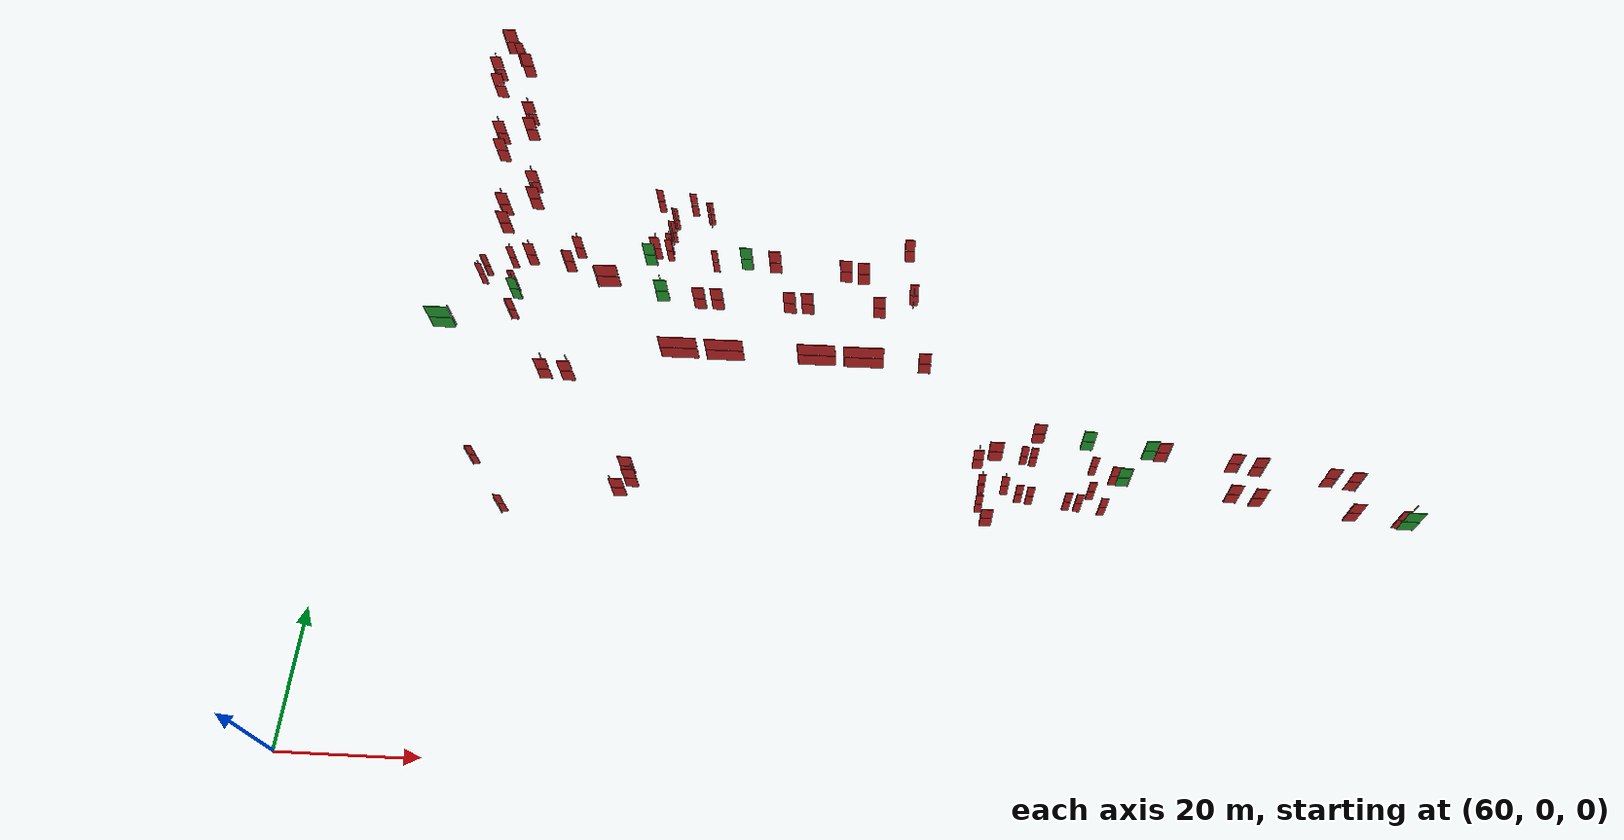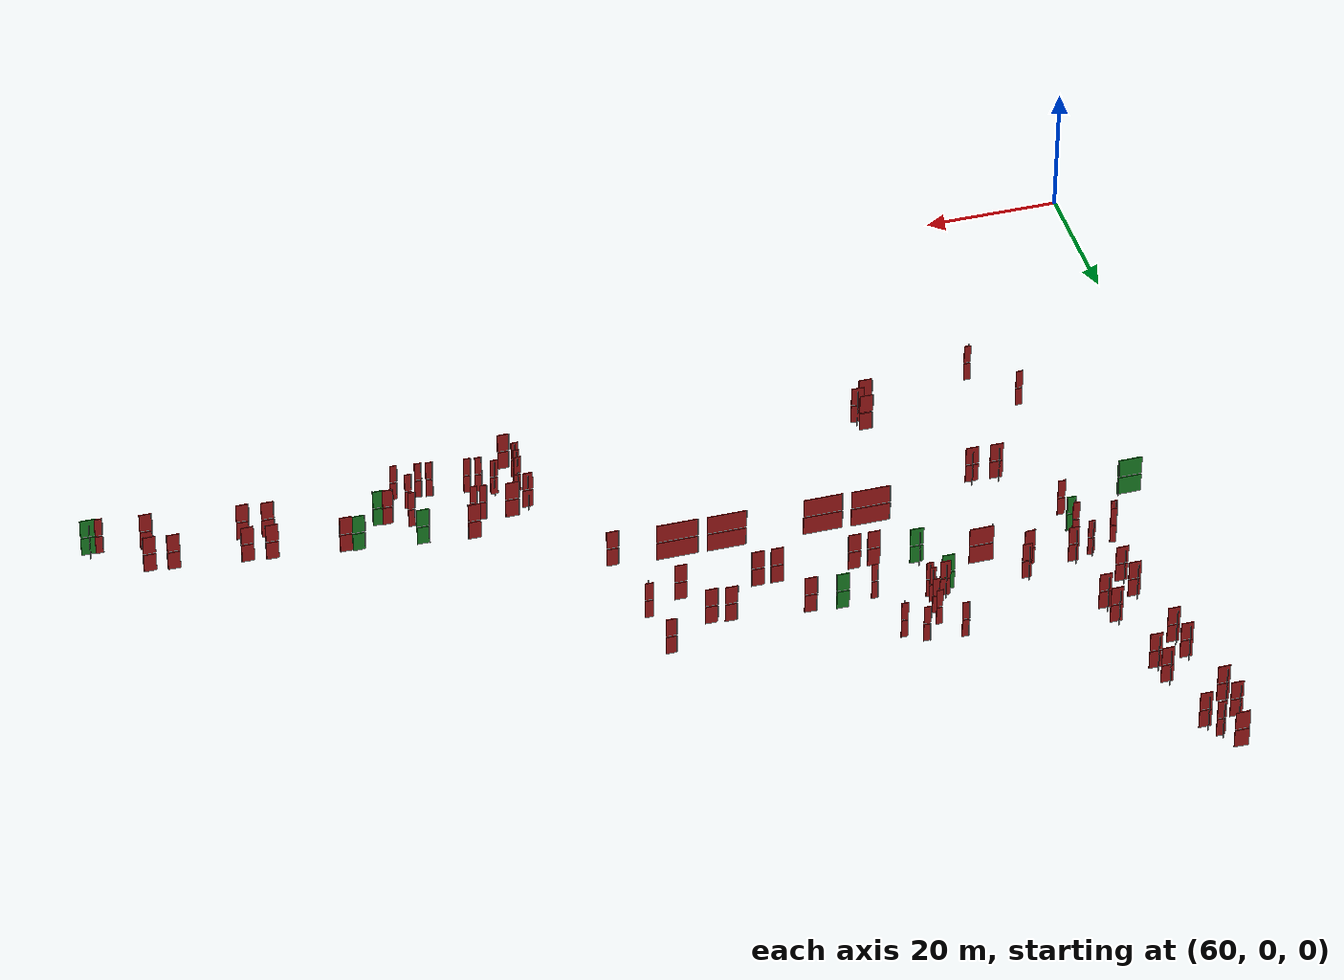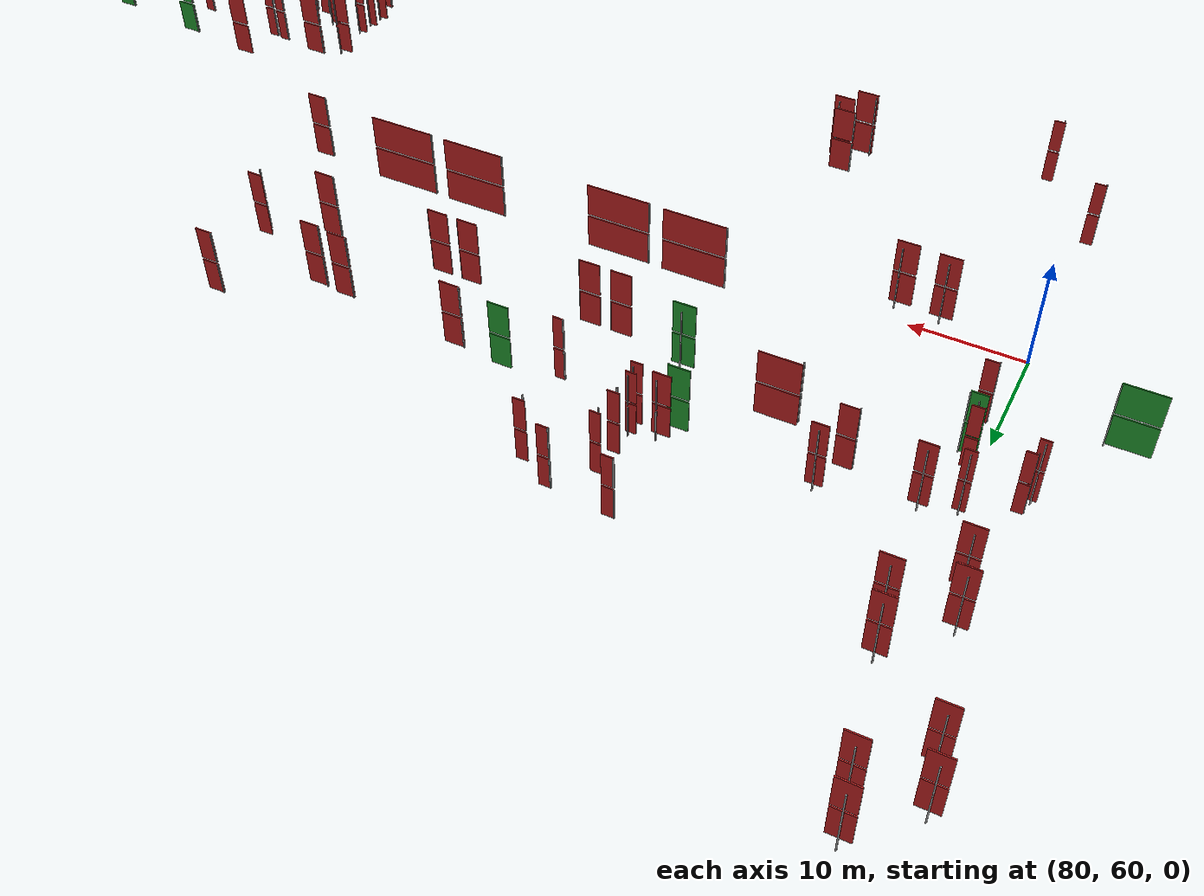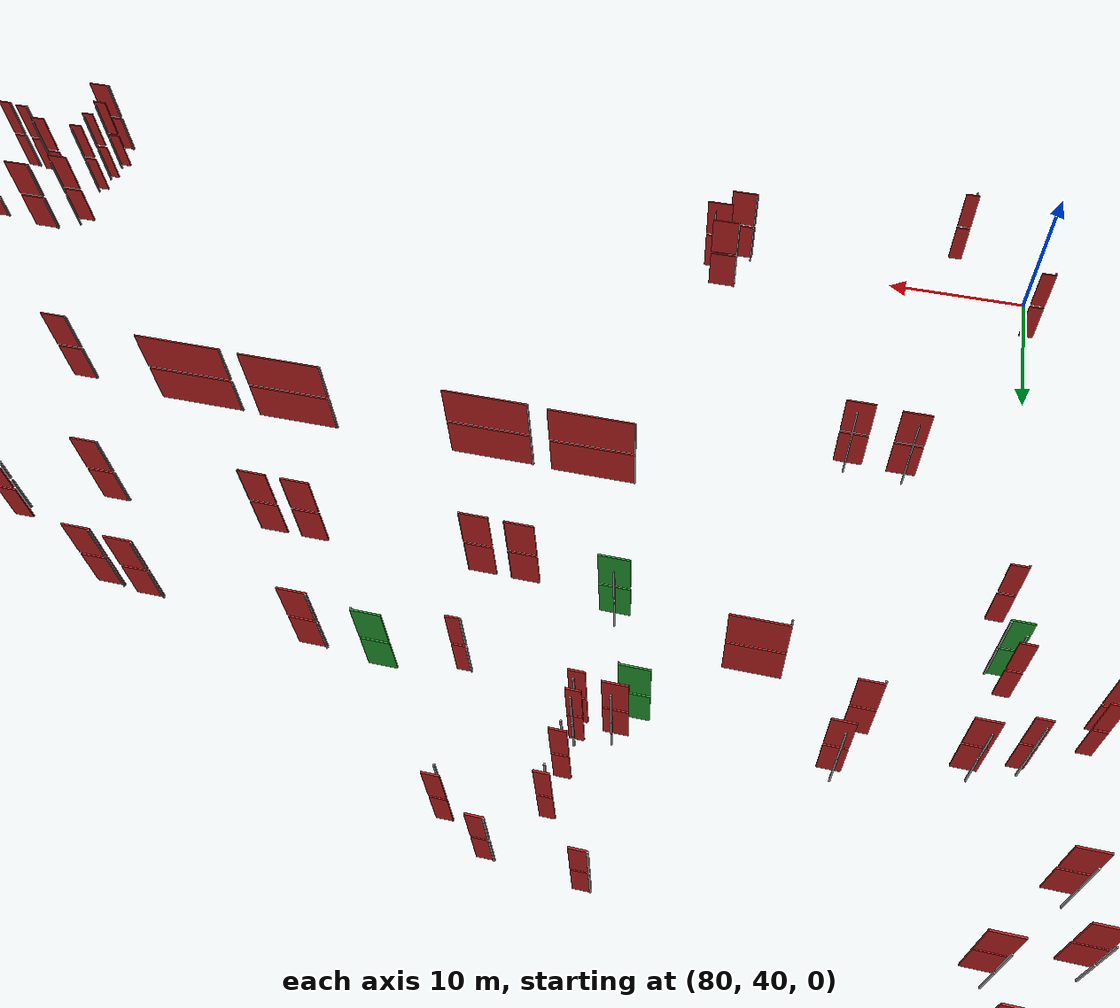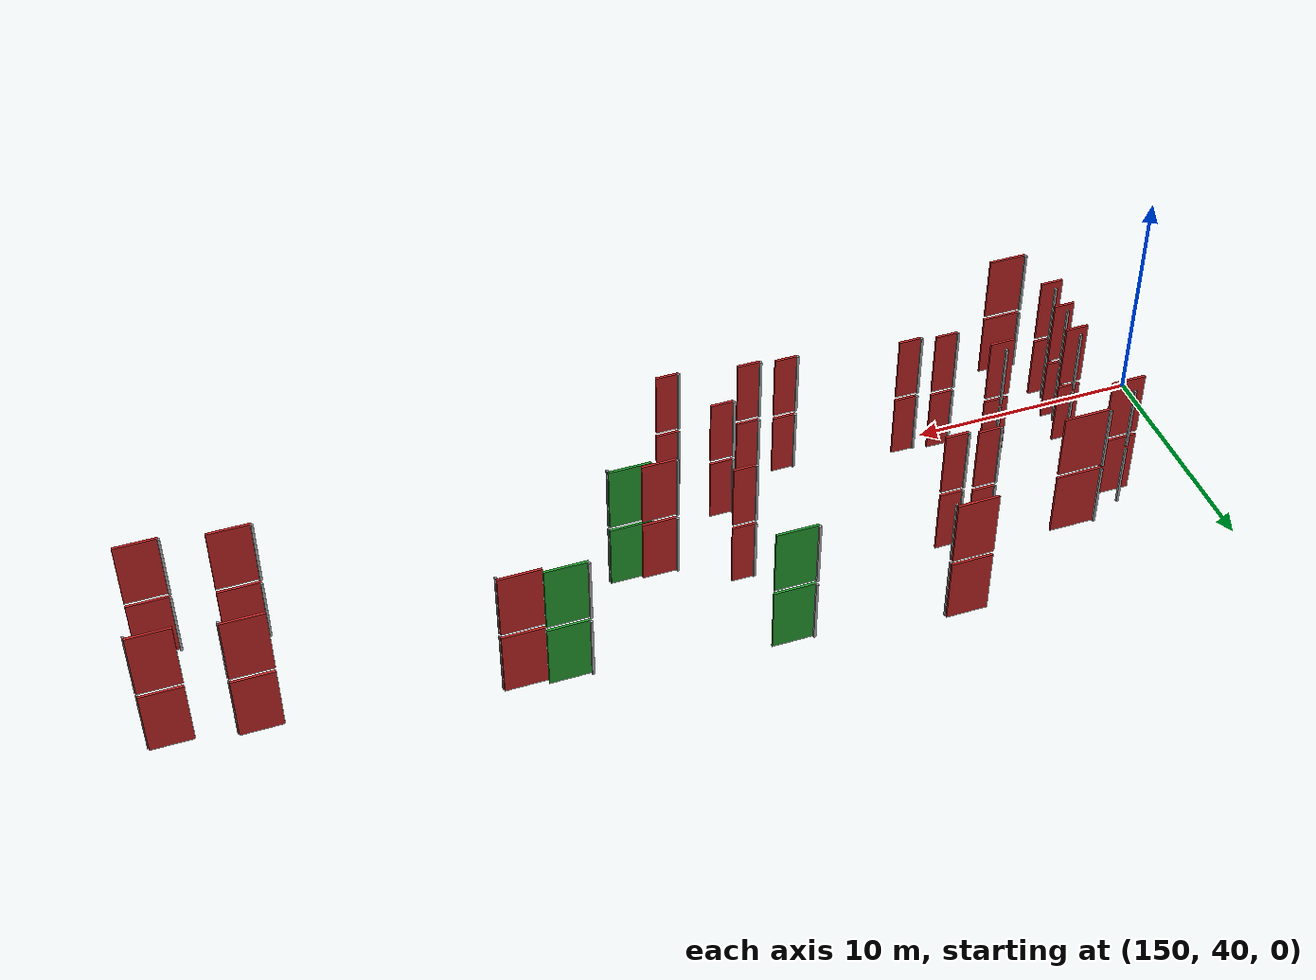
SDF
<?xml version="1.0" ?>
<sdf version="1.6">
  <world name="default">
    <model name="pivot_153.8_39.5_0.0">
      <static>true</static>
      <pose>153.8300000000163 39.49000000022352 1.5 0 0 0</pose>
      <link name="pivot_link">
        <visual name="pivot_visual">
          <geometry>
            <box>
              <size>0.1 0.1 3</size>
            </box>
          </geometry>
        </visual>
      </link>
    </model>
    <model name="door_153.8_39.5_0.0">
      <static>false</static>
      <pose>153.77499999999418 38.99500000011176 1.5 0 0 0</pose>
      <link name="door_link">
        <gravity>false</gravity>
        <visual name="door_visual">
          <geometry>
            <box>
              <size>0.9960923654221514 0.1 3</size>
            </box>
          </geometry>
          <material>
            <script>
              <uri>file://media/materials/scripts/gazebo.material</uri>
              <name>Gazebo/Red</name>
            </script>
          </material>
        </visual>
      </link>
    </model>
    <joint name="joint_153.8_39.5_0.0" type="revolute">
      <parent>pivot_153.8_39.5_0.0::pivot_link</parent>
      <child>door_153.8_39.5_0.0::door_link</child>
      <axis>
        <xyz>0 0 1</xyz>
        <limit>
          <lower>0</lower>
          <upper>1.5708</upper>
        </limit>
      </axis>
    </joint>
    <model name="pivot_166.0_40.0_0.0">
      <static>true</static>
      <pose>166.0100000000093 39.97000000020489 1.5 0 0 0</pose>
      <link name="pivot_link">
        <visual name="pivot_visual">
          <geometry>
            <box>
              <size>0.1 0.1 3</size>
            </box>
          </geometry>
        </visual>
      </link>
    </model>
    <model name="door_166.0_40.0_0.0">
      <static>false</static>
      <pose>166.50500000000466 39.91000000014901 1.5 0 0 0</pose>
      <link name="door_link">
        <gravity>false</gravity>
        <visual name="door_visual">
          <geometry>
            <box>
              <size>0.9972462083198822 0.1 3</size>
            </box>
          </geometry>
          <material>
            <script>
              <uri>file://media/materials/scripts/gazebo.material</uri>
              <name>Gazebo/Red</name>
            </script>
          </material>
        </visual>
      </link>
    </model>
    <joint name="joint_166.0_40.0_0.0" type="revolute">
      <parent>pivot_166.0_40.0_0.0::pivot_link</parent>
      <child>door_166.0_40.0_0.0::door_link</child>
      <axis>
        <xyz>0 0 1</xyz>
        <limit>
          <lower>0</lower>
          <upper>1.5708</upper>
        </limit>
      </axis>
    </joint>
    <model name="pivot_153.8_46.7_0.0">
      <static>true</static>
      <pose>153.75 46.669999999925494 1.5 0 0 0</pose>
      <link name="pivot_link">
        <visual name="pivot_visual">
          <geometry>
            <box>
              <size>0.1 0.1 3</size>
            </box>
          </geometry>
        </visual>
      </link>
    </model>
    <model name="door_153.8_46.7_0.0">
      <static>false</static>
      <pose>153.6600000000035 45.92999999993481 1.5 0 0 0</pose>
      <link name="door_link">
        <gravity>false</gravity>
        <visual name="door_visual">
          <geometry>
            <box>
              <size>1.4909057649436974 0.1 3</size>
            </box>
          </geometry>
          <material>
            <script>
              <uri>file://media/materials/scripts/gazebo.material</uri>
              <name>Gazebo/Red</name>
            </script>
          </material>
        </visual>
      </link>
    </model>
    <joint name="joint_153.8_46.7_0.0" type="revolute">
      <parent>pivot_153.8_46.7_0.0::pivot_link</parent>
      <child>door_153.8_46.7_0.0::door_link</child>
      <axis>
        <xyz>0 0 1</xyz>
        <limit>
          <lower>0</lower>
          <upper>1.5708</upper>
        </limit>
      </axis>
    </joint>
    <model name="pivot_160.6_40.6_0.0">
      <static>true</static>
      <pose>160.64000000001397 40.62000000011176 1.5 0 0 0</pose>
      <link name="pivot_link">
        <visual name="pivot_visual">
          <geometry>
            <box>
              <size>0.1 0.1 3</size>
            </box>
          </geometry>
        </visual>
      </link>
    </model>
    <model name="door_160.6_40.6_0.0">
      <static>false</static>
      <pose>161.1350000000093 40.56000000005588 1.5 0 0 0</pose>
      <link name="door_link">
        <gravity>false</gravity>
        <visual name="door_visual">
          <geometry>
            <box>
              <size>0.9972462083198822 0.1 3</size>
            </box>
          </geometry>
          <material>
            <script>
              <uri>file://media/materials/scripts/gazebo.material</uri>
              <name>Gazebo/Red</name>
            </script>
          </material>
        </visual>
      </link>
    </model>
    <joint name="joint_160.6_40.6_0.0" type="revolute">
      <parent>pivot_160.6_40.6_0.0::pivot_link</parent>
      <child>door_160.6_40.6_0.0::door_link</child>
      <axis>
        <xyz>0 0 1</xyz>
        <limit>
          <lower>0</lower>
          <upper>1.5708</upper>
        </limit>
      </axis>
    </joint>
    <model name="pivot_191.9_47.0_0.0">
      <static>true</static>
      <pose>191.86999999999534 46.95999999996275 1.5 0 0 0</pose>
      <link name="pivot_link">
        <visual name="pivot_visual">
          <geometry>
            <box>
              <size>0.1 0.1 3</size>
            </box>
          </geometry>
        </visual>
      </link>
    </model>
    <model name="door_191.9_47.0_0.0">
      <static>false</static>
      <pose>190.97500000000582 47.06499999994412 1.5 0 0 0</pose>
      <link name="door_link">
        <gravity>false</gravity>
        <visual name="door_visual">
          <geometry>
            <box>
              <size>1.8022763383869123 0.1 3</size>
            </box>
          </geometry>
          <material>
            <script>
              <uri>file://media/materials/scripts/gazebo.material</uri>
              <name>Gazebo/Red</name>
            </script>
          </material>
        </visual>
      </link>
    </model>
    <joint name="joint_191.9_47.0_0.0" type="revolute">
      <parent>pivot_191.9_47.0_0.0::pivot_link</parent>
      <child>door_191.9_47.0_0.0::door_link</child>
      <axis>
        <xyz>0 0 1</xyz>
        <limit>
          <lower>0</lower>
          <upper>1.5708</upper>
        </limit>
      </axis>
    </joint>
    <model name="pivot_181.5_48.2_0.0">
      <static>true</static>
      <pose>181.53000000002794 48.200000000186265 1.5 0 0 0</pose>
      <link name="pivot_link">
        <visual name="pivot_visual">
          <geometry>
            <box>
              <size>0.1 0.1 3</size>
            </box>
          </geometry>
        </visual>
      </link>
    </model>
    <model name="door_181.5_48.2_0.0">
      <static>false</static>
      <pose>180.6350000000093 48.31000000005588 1.5 0 0 0</pose>
      <link name="door_link">
        <gravity>false</gravity>
        <visual name="door_visual">
          <geometry>
            <box>
              <size>1.8034688796923075 0.1 3</size>
            </box>
          </geometry>
          <material>
            <script>
              <uri>file://media/materials/scripts/gazebo.material</uri>
              <name>Gazebo/Red</name>
            </script>
          </material>
        </visual>
      </link>
    </model>
    <joint name="joint_181.5_48.2_0.0" type="revolute">
      <parent>pivot_181.5_48.2_0.0::pivot_link</parent>
      <child>door_181.5_48.2_0.0::door_link</child>
      <axis>
        <xyz>0 0 1</xyz>
        <limit>
          <lower>0</lower>
          <upper>1.5708</upper>
        </limit>
      </axis>
    </joint>
    <model name="pivot_154.0_41.0_0.0">
      <static>true</static>
      <pose>154.02000000001863 41.02000000001863 1.5 0 0 0</pose>
      <link name="pivot_link">
        <visual name="pivot_visual">
          <geometry>
            <box>
              <size>0.1 0.1 3</size>
            </box>
          </geometry>
        </visual>
      </link>
    </model>
    <model name="door_154.0_41.0_0.0">
      <static>false</static>
      <pose>153.9649999999965 40.574999999953434 1.5 0 0 0</pose>
      <link name="door_link">
        <gravity>false</gravity>
        <visual name="door_visual">
          <geometry>
            <box>
              <size>0.8967719889926413 0.1 3</size>
            </box>
          </geometry>
          <material>
            <script>
              <uri>file://media/materials/scripts/gazebo.material</uri>
              <name>Gazebo/Red</name>
            </script>
          </material>
        </visual>
      </link>
    </model>
    <joint name="joint_154.0_41.0_0.0" type="revolute">
      <parent>pivot_154.0_41.0_0.0::pivot_link</parent>
      <child>door_154.0_41.0_0.0::door_link</child>
      <axis>
        <xyz>0 0 1</xyz>
        <limit>
          <lower>0</lower>
          <upper>1.5708</upper>
        </limit>
      </axis>
    </joint>
    <model name="pivot_167.6_39.8_0.0">
      <static>true</static>
      <pose>167.59999999997672 39.77999999979511 1.5 0 0 0</pose>
      <link name="pivot_link">
        <visual name="pivot_visual">
          <geometry>
            <box>
              <size>0.1 0.1 3</size>
            </box>
          </geometry>
        </visual>
      </link>
    </model>
    <model name="door_167.6_39.8_0.0">
      <static>false</static>
      <pose>168.09500000000116 39.71999999997206 1.5 0 0 0</pose>
      <link name="door_link">
        <gravity>false</gravity>
        <visual name="door_visual">
          <geometry>
            <box>
              <size>0.9972462083216332 0.1 3</size>
            </box>
          </geometry>
          <material>
            <script>
              <uri>file://media/materials/scripts/gazebo.material</uri>
              <name>Gazebo/Red</name>
            </script>
          </material>
        </visual>
      </link>
    </model>
    <joint name="joint_167.6_39.8_0.0" type="revolute">
      <parent>pivot_167.6_39.8_0.0::pivot_link</parent>
      <child>door_167.6_39.8_0.0::door_link</child>
      <axis>
        <xyz>0 0 1</xyz>
        <limit>
          <lower>0</lower>
          <upper>1.5708</upper>
        </limit>
      </axis>
    </joint>
    <model name="pivot_195.3_46.5_0.0">
      <static>true</static>
      <pose>195.30999999999767 46.54000000003725 1.5 0 0 0</pose>
      <link name="pivot_link">
        <visual name="pivot_visual">
          <geometry>
            <box>
              <size>0.1 0.1 3</size>
            </box>
          </geometry>
        </visual>
      </link>
    </model>
    <model name="door_195.3_46.5_0.0">
      <static>false</static>
      <pose>194.41500000000815 46.64999999990687 1.5 0 0 0</pose>
      <link name="door_link">
        <gravity>false</gravity>
        <visual name="door_visual">
          <geometry>
            <box>
              <size>1.8034688796345346 0.1 3</size>
            </box>
          </geometry>
          <material>
            <script>
              <uri>file://media/materials/scripts/gazebo.material</uri>
              <name>Gazebo/Red</name>
            </script>
          </material>
        </visual>
      </link>
    </model>
    <joint name="joint_195.3_46.5_0.0" type="revolute">
      <parent>pivot_195.3_46.5_0.0::pivot_link</parent>
      <child>door_195.3_46.5_0.0::door_link</child>
      <axis>
        <xyz>0 0 1</xyz>
        <limit>
          <lower>0</lower>
          <upper>1.5708</upper>
        </limit>
      </axis>
    </joint>
    <model name="pivot_205.6_45.3_0.0">
      <static>true</static>
      <pose>205.64000000001397 45.299999999813735 1.5 0 0 0</pose>
      <link name="pivot_link">
        <visual name="pivot_visual">
          <geometry>
            <box>
              <size>0.1 0.1 3</size>
            </box>
          </geometry>
        </visual>
      </link>
    </model>
    <model name="door_205.6_45.3_0.0">
      <static>false</static>
      <pose>204.74499999999534 45.40499999979511 1.5 0 0 0</pose>
      <link name="door_link">
        <gravity>false</gravity>
        <visual name="door_visual">
          <geometry>
            <box>
              <size>1.8022763384447233 0.1 3</size>
            </box>
          </geometry>
          <material>
            <script>
              <uri>file://media/materials/scripts/gazebo.material</uri>
              <name>Gazebo/Red</name>
            </script>
          </material>
        </visual>
      </link>
    </model>
    <joint name="joint_205.6_45.3_0.0" type="revolute">
      <parent>pivot_205.6_45.3_0.0::pivot_link</parent>
      <child>door_205.6_45.3_0.0::door_link</child>
      <axis>
        <xyz>0 0 1</xyz>
        <limit>
          <lower>0</lower>
          <upper>1.5708</upper>
        </limit>
      </axis>
    </joint>
    <model name="pivot_155.3_47.4_0.0">
      <static>true</static>
      <pose>155.2600000000093 47.43999999994412 1.5 0 0 0</pose>
      <link name="pivot_link">
        <visual name="pivot_visual">
          <geometry>
            <box>
              <size>0.1 0.1 3</size>
            </box>
          </geometry>
        </visual>
      </link>
    </model>
    <model name="door_155.3_47.4_0.0">
      <static>false</static>
      <pose>156.25500000000466 47.32000000006519 1.5 0 0 0</pose>
      <link name="door_link">
        <gravity>false</gravity>
        <visual name="door_visual">
          <geometry>
            <box>
              <size>2.004420115606183 0.1 3</size>
            </box>
          </geometry>
          <material>
            <script>
              <uri>file://media/materials/scripts/gazebo.material</uri>
              <name>Gazebo/Red</name>
            </script>
          </material>
        </visual>
      </link>
    </model>
    <joint name="joint_155.3_47.4_0.0" type="revolute">
      <parent>pivot_155.3_47.4_0.0::pivot_link</parent>
      <child>door_155.3_47.4_0.0::door_link</child>
      <axis>
        <xyz>0 0 1</xyz>
        <limit>
          <lower>0</lower>
          <upper>1.5708</upper>
        </limit>
      </axis>
    </joint>
    <model name="pivot_159.9_46.9_0.0">
      <static>true</static>
      <pose>159.89000000001397 46.87999999988824 1.5 0 0 0</pose>
      <link name="pivot_link">
        <visual name="pivot_visual">
          <geometry>
            <box>
              <size>0.1 0.1 3</size>
            </box>
          </geometry>
        </visual>
      </link>
    </model>
    <model name="door_159.9_46.9_0.0">
      <static>false</static>
      <pose>160.3850000000093 46.81999999983236 1.5 0 0 0</pose>
      <link name="door_link">
        <gravity>false</gravity>
        <visual name="door_visual">
          <geometry>
            <box>
              <size>0.9972462083198822 0.1 3</size>
            </box>
          </geometry>
          <material>
            <script>
              <uri>file://media/materials/scripts/gazebo.material</uri>
              <name>Gazebo/Red</name>
            </script>
          </material>
        </visual>
      </link>
    </model>
    <joint name="joint_159.9_46.9_0.0" type="revolute">
      <parent>pivot_159.9_46.9_0.0::pivot_link</parent>
      <child>door_159.9_46.9_0.0::door_link</child>
      <axis>
        <xyz>0 0 1</xyz>
        <limit>
          <lower>0</lower>
          <upper>1.5708</upper>
        </limit>
      </axis>
    </joint>
    <model name="pivot_161.3_46.7_0.0">
      <static>true</static>
      <pose>161.2600000000093 46.72000000020489 1.5 0 0 0</pose>
      <link name="pivot_link">
        <visual name="pivot_visual">
          <geometry>
            <box>
              <size>0.1 0.1 3</size>
            </box>
          </geometry>
        </visual>
      </link>
    </model>
    <model name="door_161.3_46.7_0.0">
      <static>false</static>
      <pose>161.7600000000093 46.66000000014901 1.5 0 0 0</pose>
      <link name="door_link">
        <gravity>false</gravity>
        <visual name="door_visual">
          <geometry>
            <box>
              <size>1.0071742649744493 0.1 3</size>
            </box>
          </geometry>
          <material>
            <script>
              <uri>file://media/materials/scripts/gazebo.material</uri>
              <name>Gazebo/Red</name>
            </script>
          </material>
        </visual>
      </link>
    </model>
    <joint name="joint_161.3_46.7_0.0" type="revolute">
      <parent>pivot_161.3_46.7_0.0::pivot_link</parent>
      <child>door_161.3_46.7_0.0::door_link</child>
      <axis>
        <xyz>0 0 1</xyz>
        <limit>
          <lower>0</lower>
          <upper>1.5708</upper>
        </limit>
      </axis>
    </joint>
    <model name="pivot_170.0_45.7_0.0">
      <static>true</static>
      <pose>169.9899999999907 45.669999999925494 1.5 0 0 0</pose>
      <link name="pivot_link">
        <visual name="pivot_visual">
          <geometry>
            <box>
              <size>0.1 0.1 3</size>
            </box>
          </geometry>
        </visual>
      </link>
    </model>
    <model name="door_170.0_45.7_0.0">
      <static>false</static>
      <pose>170.48499999998603 45.609999999869615 1.5 0 0 0</pose>
      <link name="door_link">
        <gravity>false</gravity>
        <visual name="door_visual">
          <geometry>
            <box>
              <size>0.9972462083198822 0.1 3</size>
            </box>
          </geometry>
          <material>
            <script>
              <uri>file://media/materials/scripts/gazebo.material</uri>
              <name>Gazebo/Red</name>
            </script>
          </material>
        </visual>
      </link>
    </model>
    <joint name="joint_170.0_45.7_0.0" type="revolute">
      <parent>pivot_170.0_45.7_0.0::pivot_link</parent>
      <child>door_170.0_45.7_0.0::door_link</child>
      <axis>
        <xyz>0 0 1</xyz>
        <limit>
          <lower>0</lower>
          <upper>1.5708</upper>
        </limit>
      </axis>
    </joint>
    <model name="pivot_175.7_44.0_0.0">
      <static>true</static>
      <pose>175.70000000001164 43.97000000020489 1.5 0 0 0</pose>
      <link name="pivot_link">
        <visual name="pivot_visual">
          <geometry>
            <box>
              <size>0.1 0.1 3</size>
            </box>
          </geometry>
        </visual>
      </link>
    </model>
    <model name="door_175.7_44.0_0.0">
      <static>false</static>
      <pose>174.80499999999302 44.075000000419095 1.5 0 0 0</pose>
      <link name="door_link">
        <gravity>false</gravity>
        <visual name="door_visual">
          <geometry>
            <box>
              <size>1.802276338498982 0.1 3</size>
            </box>
          </geometry>
          <material>
            <script>
              <uri>file://media/materials/scripts/gazebo.material</uri>
              <name>Gazebo/Green</name>
            </script>
          </material>
        </visual>
      </link>
    </model>
    <joint name="joint_175.7_44.0_0.0" type="revolute">
      <parent>pivot_175.7_44.0_0.0::pivot_link</parent>
      <child>door_175.7_44.0_0.0::door_link</child>
      <axis>
        <xyz>0 0 1</xyz>
        <limit>
          <lower>0</lower>
          <upper>1.5708</upper>
        </limit>
      </axis>
    </joint>
    <model name="pivot_189.6_42.3_0.0">
      <static>true</static>
      <pose>189.59999999997672 42.299999999813735 1.5 0 0 0</pose>
      <link name="pivot_link">
        <visual name="pivot_visual">
          <geometry>
            <box>
              <size>0.1 0.1 3</size>
            </box>
          </geometry>
        </visual>
      </link>
    </model>
    <model name="door_189.6_42.3_0.0">
      <static>false</static>
      <pose>190.5 42.18999999994412 1.5 0 0 0</pose>
      <link name="door_link">
        <gravity>false</gravity>
        <visual name="door_visual">
          <geometry>
            <box>
              <size>1.8133946068224918 0.1 3</size>
            </box>
          </geometry>
          <material>
            <script>
              <uri>file://media/materials/scripts/gazebo.material</uri>
              <name>Gazebo/Red</name>
            </script>
          </material>
        </visual>
      </link>
    </model>
    <joint name="joint_189.6_42.3_0.0" type="revolute">
      <parent>pivot_189.6_42.3_0.0::pivot_link</parent>
      <child>door_189.6_42.3_0.0::door_link</child>
      <axis>
        <xyz>0 0 1</xyz>
        <limit>
          <lower>0</lower>
          <upper>1.5708</upper>
        </limit>
      </axis>
    </joint>
    <model name="pivot_193.1_41.9_0.0">
      <static>true</static>
      <pose>193.14000000001397 41.87000000011176 1.5 0 0 0</pose>
      <link name="pivot_link">
        <visual name="pivot_visual">
          <geometry>
            <box>
              <size>0.1 0.1 3</size>
            </box>
          </geometry>
        </visual>
      </link>
    </model>
    <model name="door_193.1_41.9_0.0">
      <static>false</static>
      <pose>194.0350000000035 41.765000000130385 1.5 0 0 0</pose>
      <link name="door_link">
        <gravity>false</gravity>
        <visual name="door_visual">
          <geometry>
            <box>
              <size>1.8022763383869123 0.1 3</size>
            </box>
          </geometry>
          <material>
            <script>
              <uri>file://media/materials/scripts/gazebo.material</uri>
              <name>Gazebo/Red</name>
            </script>
          </material>
        </visual>
      </link>
    </model>
    <joint name="joint_193.1_41.9_0.0" type="revolute">
      <parent>pivot_193.1_41.9_0.0::pivot_link</parent>
      <child>door_193.1_41.9_0.0::door_link</child>
      <axis>
        <xyz>0 0 1</xyz>
        <limit>
          <lower>0</lower>
          <upper>1.5708</upper>
        </limit>
      </axis>
    </joint>
    <model name="pivot_206.7_40.2_0.0">
      <static>true</static>
      <pose>206.6699999999837 40.24000000022352 1.5 0 0 0</pose>
      <link name="pivot_link">
        <visual name="pivot_visual">
          <geometry>
            <box>
              <size>0.1 0.1 3</size>
            </box>
          </geometry>
        </visual>
      </link>
    </model>
    <model name="door_206.7_40.2_0.0">
      <static>false</static>
      <pose>207.55999999999767 40.13500000000931 1.5 0 0 0</pose>
      <link name="door_link">
        <gravity>false</gravity>
        <visual name="door_visual">
          <geometry>
            <box>
              <size>1.7923448329714338 0.1 3</size>
            </box>
          </geometry>
          <material>
            <script>
              <uri>file://media/materials/scripts/gazebo.material</uri>
              <name>Gazebo/Red</name>
            </script>
          </material>
        </visual>
      </link>
    </model>
    <joint name="joint_206.7_40.2_0.0" type="revolute">
      <parent>pivot_206.7_40.2_0.0::pivot_link</parent>
      <child>door_206.7_40.2_0.0::door_link</child>
      <axis>
        <xyz>0 0 1</xyz>
        <limit>
          <lower>0</lower>
          <upper>1.5708</upper>
        </limit>
      </axis>
    </joint>
    <model name="pivot_178.0_48.6_0.0">
      <static>true</static>
      <pose>177.96000000002095 48.62999999988824 1.5 0 0 0</pose>
      <link name="pivot_link">
        <visual name="pivot_visual">
          <geometry>
            <box>
              <size>0.1 0.1 3</size>
            </box>
          </geometry>
        </visual>
      </link>
    </model>
    <model name="door_178.0_48.6_0.0">
      <static>false</static>
      <pose>178.85500000003958 48.519999999785796 1.5 0 0 0</pose>
      <link name="door_link">
        <gravity>false</gravity>
        <visual name="door_visual">
          <geometry>
            <box>
              <size>1.803468879749112 0.1 3</size>
            </box>
          </geometry>
          <material>
            <script>
              <uri>file://media/materials/scripts/gazebo.material</uri>
              <name>Gazebo/Green</name>
            </script>
          </material>
        </visual>
      </link>
    </model>
    <joint name="joint_178.0_48.6_0.0" type="revolute">
      <parent>pivot_178.0_48.6_0.0::pivot_link</parent>
      <child>door_178.0_48.6_0.0::door_link</child>
      <axis>
        <xyz>0 0 1</xyz>
        <limit>
          <lower>0</lower>
          <upper>1.5708</upper>
        </limit>
      </axis>
    </joint>
    <model name="pivot_168.9_49.7_0.0">
      <static>true</static>
      <pose>168.94000000000233 49.72000000020489 1.5 0 0 0</pose>
      <link name="pivot_link">
        <visual name="pivot_visual">
          <geometry>
            <box>
              <size>0.1 0.1 3</size>
            </box>
          </geometry>
        </visual>
      </link>
    </model>
    <model name="door_168.9_49.7_0.0">
      <static>false</static>
      <pose>169.83500000002095 49.61500000022352 1.5 0 0 0</pose>
      <link name="door_link">
        <gravity>false</gravity>
        <visual name="door_visual">
          <geometry>
            <box>
              <size>1.8022763384447233 0.1 3</size>
            </box>
          </geometry>
          <material>
            <script>
              <uri>file://media/materials/scripts/gazebo.material</uri>
              <name>Gazebo/Green</name>
            </script>
          </material>
        </visual>
      </link>
    </model>
    <joint name="joint_168.9_49.7_0.0" type="revolute">
      <parent>pivot_168.9_49.7_0.0::pivot_link</parent>
      <child>door_168.9_49.7_0.0::door_link</child>
      <axis>
        <xyz>0 0 1</xyz>
        <limit>
          <lower>0</lower>
          <upper>1.5708</upper>
        </limit>
      </axis>
    </joint>
    <model name="pivot_163.5_50.4_0.0">
      <static>true</static>
      <pose>163.46000000002095 50.37999999988824 1.5 0 0 0</pose>
      <link name="pivot_link">
        <visual name="pivot_visual">
          <geometry>
            <box>
              <size>0.1 0.1 3</size>
            </box>
          </geometry>
        </visual>
      </link>
    </model>
    <model name="door_163.5_50.4_0.0">
      <static>false</static>
      <pose>162.57000000000698 50.484999999869615 1.5 0 0 0</pose>
      <link name="door_link">
        <gravity>false</gravity>
        <visual name="door_visual">
          <geometry>
            <box>
              <size>1.7923448329168745 0.1 3</size>
            </box>
          </geometry>
          <material>
            <script>
              <uri>file://media/materials/scripts/gazebo.material</uri>
              <name>Gazebo/Red</name>
            </script>
          </material>
        </visual>
      </link>
    </model>
    <joint name="joint_163.5_50.4_0.0" type="revolute">
      <parent>pivot_163.5_50.4_0.0::pivot_link</parent>
      <child>door_163.5_50.4_0.0::door_link</child>
      <axis>
        <xyz>0 0 1</xyz>
        <limit>
          <lower>0</lower>
          <upper>1.5708</upper>
        </limit>
      </axis>
    </joint>
    <model name="pivot_172.9_44.3_0.0">
      <static>true</static>
      <pose>172.86999999999534 44.31000000005588 1.5 0 0 0</pose>
      <link name="pivot_link">
        <visual name="pivot_visual">
          <geometry>
            <box>
              <size>0.1 0.1 3</size>
            </box>
          </geometry>
        </visual>
      </link>
    </model>
    <model name="door_172.9_44.3_0.0">
      <static>false</static>
      <pose>173.6149999999907 44.21999999997206 1.5 0 0 0</pose>
      <link name="door_link">
        <gravity>false</gravity>
        <visual name="door_visual">
          <geometry>
            <box>
              <size>1.5008331019912227 0.1 3</size>
            </box>
          </geometry>
          <material>
            <script>
              <uri>file://media/materials/scripts/gazebo.material</uri>
              <name>Gazebo/Red</name>
            </script>
          </material>
        </visual>
      </link>
    </model>
    <joint name="joint_172.9_44.3_0.0" type="revolute">
      <parent>pivot_172.9_44.3_0.0::pivot_link</parent>
      <child>door_172.9_44.3_0.0::door_link</child>
      <axis>
        <xyz>0 0 1</xyz>
        <limit>
          <lower>0</lower>
          <upper>1.5708</upper>
        </limit>
      </axis>
    </joint>
    <model name="pivot_213.6_39.4_0.0">
      <static>true</static>
      <pose>213.5900000000256 39.41000000014901 1.5 0 0 0</pose>
      <link name="pivot_link">
        <visual name="pivot_visual">
          <geometry>
            <box>
              <size>0.1 0.1 3</size>
            </box>
          </geometry>
        </visual>
      </link>
    </model>
    <model name="door_213.6_39.4_0.0">
      <static>false</static>
      <pose>214.1350000000093 39.34499999997206 1.5 0 0 0</pose>
      <link name="door_link">
        <gravity>false</gravity>
        <visual name="door_visual">
          <geometry>
            <box>
              <size>1.097724920014552 0.1 3</size>
            </box>
          </geometry>
          <material>
            <script>
              <uri>file://media/materials/scripts/gazebo.material</uri>
              <name>Gazebo/Red</name>
            </script>
          </material>
        </visual>
      </link>
    </model>
    <joint name="joint_213.6_39.4_0.0" type="revolute">
      <parent>pivot_213.6_39.4_0.0::pivot_link</parent>
      <child>door_213.6_39.4_0.0::door_link</child>
      <axis>
        <xyz>0 0 1</xyz>
        <limit>
          <lower>0</lower>
          <upper>1.5708</upper>
        </limit>
      </axis>
    </joint>
    <model name="pivot_215.7_40.4_0.0">
      <static>true</static>
      <pose>215.65000000002328 40.37000000011176 1.5 0 0 0</pose>
      <link name="pivot_link">
        <visual name="pivot_visual">
          <geometry>
            <box>
              <size>0.1 0.1 3</size>
            </box>
          </geometry>
        </visual>
      </link>
    </model>
    <model name="door_215.7_40.4_0.0">
      <static>false</static>
      <pose>215.50000000011642 39.16000000014901 1.5 0 0 0</pose>
      <link name="door_link">
        <gravity>false</gravity>
        <visual name="door_visual">
          <geometry>
            <box>
              <size>2.438524143724567 0.1 3</size>
            </box>
          </geometry>
          <material>
            <script>
              <uri>file://media/materials/scripts/gazebo.material</uri>
              <name>Gazebo/Green</name>
            </script>
          </material>
        </visual>
      </link>
    </model>
    <joint name="joint_215.7_40.4_0.0" type="revolute">
      <parent>pivot_215.7_40.4_0.0::pivot_link</parent>
      <child>door_215.7_40.4_0.0::door_link</child>
      <axis>
        <xyz>0 0 1</xyz>
        <limit>
          <lower>0</lower>
          <upper>1.5708</upper>
        </limit>
      </axis>
    </joint>
    <model name="pivot_209.0_44.9_0.0">
      <static>true</static>
      <pose>208.9899999999907 44.890000000130385 1.5 0 0 0</pose>
      <link name="pivot_link">
        <visual name="pivot_visual">
          <geometry>
            <box>
              <size>0.1 0.1 3</size>
            </box>
          </geometry>
        </visual>
      </link>
    </model>
    <model name="door_209.0_44.9_0.0">
      <static>false</static>
      <pose>208.09500000000116 45.0 1.5 0 0 0</pose>
      <link name="door_link">
        <gravity>false</gravity>
        <visual name="door_visual">
          <geometry>
            <box>
              <size>1.8034688796345346 0.1 3</size>
            </box>
          </geometry>
          <material>
            <script>
              <uri>file://media/materials/scripts/gazebo.material</uri>
              <name>Gazebo/Red</name>
            </script>
          </material>
        </visual>
      </link>
    </model>
    <joint name="joint_209.0_44.9_0.0" type="revolute">
      <parent>pivot_209.0_44.9_0.0::pivot_link</parent>
      <child>door_209.0_44.9_0.0::door_link</child>
      <axis>
        <xyz>0 0 1</xyz>
        <limit>
          <lower>0</lower>
          <upper>1.5708</upper>
        </limit>
      </axis>
    </joint>
    <model name="pivot_169.5_41.8_0.0">
      <static>true</static>
      <pose>169.5100000000093 41.75 1.5 0 0 0</pose>
      <link name="pivot_link">
        <visual name="pivot_visual">
          <geometry>
            <box>
              <size>0.1 0.1 3</size>
            </box>
          </geometry>
        </visual>
      </link>
    </model>
    <model name="door_169.5_41.8_0.0">
      <static>false</static>
      <pose>170.0100000000093 41.68999999994412 1.5 0 0 0</pose>
      <link name="door_link">
        <gravity>false</gravity>
        <visual name="door_visual">
          <geometry>
            <box>
              <size>1.0071742649744493 0.1 3</size>
            </box>
          </geometry>
          <material>
            <script>
              <uri>file://media/materials/scripts/gazebo.material</uri>
              <name>Gazebo/Red</name>
            </script>
          </material>
        </visual>
      </link>
    </model>
    <joint name="joint_169.5_41.8_0.0" type="revolute">
      <parent>pivot_169.5_41.8_0.0::pivot_link</parent>
      <child>door_169.5_41.8_0.0::door_link</child>
      <axis>
        <xyz>0 0 1</xyz>
        <limit>
          <lower>0</lower>
          <upper>1.5708</upper>
        </limit>
      </axis>
    </joint>
    <model name="pivot_154.2_42.6_0.0">
      <static>true</static>
      <pose>154.21000000002095 42.64999999990687 1.5 0 0 0</pose>
      <link name="pivot_link">
        <visual name="pivot_visual">
          <geometry>
            <box>
              <size>0.1 0.1 3</size>
            </box>
          </geometry>
        </visual>
      </link>
    </model>
    <model name="door_154.2_42.6_0.0">
      <static>false</static>
      <pose>154.15000000002328 42.15500000002794 1.5 0 0 0</pose>
      <link name="door_link">
        <gravity>false</gravity>
        <visual name="door_visual">
          <geometry>
            <box>
              <size>0.997246208074735 0.1 3</size>
            </box>
          </geometry>
          <material>
            <script>
              <uri>file://media/materials/scripts/gazebo.material</uri>
              <name>Gazebo/Red</name>
            </script>
          </material>
        </visual>
      </link>
    </model>
    <joint name="joint_154.2_42.6_0.0" type="revolute">
      <parent>pivot_154.2_42.6_0.0::pivot_link</parent>
      <child>door_154.2_42.6_0.0::door_link</child>
      <axis>
        <xyz>0 0 1</xyz>
        <limit>
          <lower>0</lower>
          <upper>1.5708</upper>
        </limit>
      </axis>
    </joint>
    <model name="pivot_157.6_42.5_0.0">
      <static>true</static>
      <pose>157.5800000000163 42.49000000022352 1.5 0 0 0</pose>
      <link name="pivot_link">
        <visual name="pivot_visual">
          <geometry>
            <box>
              <size>0.1 0.1 3</size>
            </box>
          </geometry>
        </visual>
      </link>
    </model>
    <model name="door_157.6_42.5_0.0">
      <static>false</static>
      <pose>157.51500000001397 41.94500000006519 1.5 0 0 0</pose>
      <link name="door_link">
        <gravity>false</gravity>
        <visual name="door_visual">
          <geometry>
            <box>
              <size>1.0977249203199801 0.1 3</size>
            </box>
          </geometry>
          <material>
            <script>
              <uri>file://media/materials/scripts/gazebo.material</uri>
              <name>Gazebo/Red</name>
            </script>
          </material>
        </visual>
      </link>
    </model>
    <joint name="joint_157.6_42.5_0.0" type="revolute">
      <parent>pivot_157.6_42.5_0.0::pivot_link</parent>
      <child>door_157.6_42.5_0.0::door_link</child>
      <axis>
        <xyz>0 0 1</xyz>
        <limit>
          <lower>0</lower>
          <upper>1.5708</upper>
        </limit>
      </axis>
    </joint>
    <model name="pivot_154.0_37.0_0.0">
      <static>true</static>
      <pose>154.03999999997905 36.950000000186265 1.5 0 0 0</pose>
      <link name="pivot_link">
        <visual name="pivot_visual">
          <geometry>
            <box>
              <size>0.1 0.1 3</size>
            </box>
          </geometry>
        </visual>
      </link>
    </model>
    <model name="door_154.0_37.0_0.0">
      <static>false</static>
      <pose>154.86999999999534 36.85000000009313 1.5 0 0 0</pose>
      <link name="door_link">
        <gravity>false</gravity>
        <visual name="door_visual">
          <geometry>
            <box>
              <size>1.6720047847367918 0.1 3</size>
            </box>
          </geometry>
          <material>
            <script>
              <uri>file://media/materials/scripts/gazebo.material</uri>
              <name>Gazebo/Red</name>
            </script>
          </material>
        </visual>
      </link>
    </model>
    <joint name="joint_154.0_37.0_0.0" type="revolute">
      <parent>pivot_154.0_37.0_0.0::pivot_link</parent>
      <child>door_154.0_37.0_0.0::door_link</child>
      <axis>
        <xyz>0 0 1</xyz>
        <limit>
          <lower>0</lower>
          <upper>1.5708</upper>
        </limit>
      </axis>
    </joint>
    <model name="pivot_159.0_40.8_0.0">
      <static>true</static>
      <pose>159.04999999998836 40.81000000005588 1.5 0 0 0</pose>
      <link name="pivot_link">
        <visual name="pivot_visual">
          <geometry>
            <box>
              <size>0.1 0.1 3</size>
            </box>
          </geometry>
        </visual>
      </link>
    </model>
    <model name="door_159.0_40.8_0.0">
      <static>false</static>
      <pose>159.5449999999837 40.75 1.5 0 0 0</pose>
      <link name="door_link">
        <gravity>false</gravity>
        <visual name="door_visual">
          <geometry>
            <box>
              <size>0.9972462083198822 0.1 3</size>
            </box>
          </geometry>
          <material>
            <script>
              <uri>file://media/materials/scripts/gazebo.material</uri>
              <name>Gazebo/Red</name>
            </script>
          </material>
        </visual>
      </link>
    </model>
    <joint name="joint_159.0_40.8_0.0" type="revolute">
      <parent>pivot_159.0_40.8_0.0::pivot_link</parent>
      <child>door_159.0_40.8_0.0::door_link</child>
      <axis>
        <xyz>0 0 1</xyz>
        <limit>
          <lower>0</lower>
          <upper>1.5708</upper>
        </limit>
      </axis>
    </joint>
    <model name="pivot_171.1_39.4_0.0">
      <static>true</static>
      <pose>171.07000000000698 39.359999999869615 1.5 0 0 0</pose>
      <link name="pivot_link">
        <visual name="pivot_visual">
          <geometry>
            <box>
              <size>0.1 0.1 3</size>
            </box>
          </geometry>
        </visual>
      </link>
    </model>
    <model name="door_171.1_39.4_0.0">
      <static>false</static>
      <pose>171.56500000000233 39.300000000046566 1.5 0 0 0</pose>
      <link name="door_link">
        <gravity>false</gravity>
        <visual name="door_visual">
          <geometry>
            <box>
              <size>0.9972462082638486 0.1 3</size>
            </box>
          </geometry>
          <material>
            <script>
              <uri>file://media/materials/scripts/gazebo.material</uri>
              <name>Gazebo/Red</name>
            </script>
          </material>
        </visual>
      </link>
    </model>
    <joint name="joint_171.1_39.4_0.0" type="revolute">
      <parent>pivot_171.1_39.4_0.0::pivot_link</parent>
      <child>door_171.1_39.4_0.0::door_link</child>
      <axis>
        <xyz>0 0 1</xyz>
        <limit>
          <lower>0</lower>
          <upper>1.5708</upper>
        </limit>
      </axis>
    </joint>
    <model name="pivot_80.1_77.7_0.0">
      <static>true</static>
      <pose>80.09999999997672 77.70999999996275 1.5 0 0 0</pose>
      <link name="pivot_link">
        <visual name="pivot_visual">
          <geometry>
            <box>
              <size>0.1 0.1 3</size>
            </box>
          </geometry>
        </visual>
      </link>
    </model>
    <model name="door_80.1_77.7_0.0">
      <static>false</static>
      <pose>80.19499999997788 77.22500000009313 1.5 0 0 0</pose>
      <link name="door_link">
        <gravity>false</gravity>
        <visual name="door_visual">
          <geometry>
            <box>
              <size>0.9884331031966657 0.1 3</size>
            </box>
          </geometry>
          <material>
            <script>
              <uri>file://media/materials/scripts/gazebo.material</uri>
              <name>Gazebo/Red</name>
            </script>
          </material>
        </visual>
      </link>
    </model>
    <joint name="joint_80.1_77.7_0.0" type="revolute">
      <parent>pivot_80.1_77.7_0.0::pivot_link</parent>
      <child>door_80.1_77.7_0.0::door_link</child>
      <axis>
        <xyz>0 0 1</xyz>
        <limit>
          <lower>0</lower>
          <upper>1.5708</upper>
        </limit>
      </axis>
    </joint>
    <model name="pivot_134.6_76.9_0.0">
      <static>true</static>
      <pose>134.59999999997672 76.87999999988824 1.5 0 0 0</pose>
      <link name="pivot_link">
        <visual name="pivot_visual">
          <geometry>
            <box>
              <size>0.1 0.1 3</size>
            </box>
          </geometry>
        </visual>
      </link>
    </model>
    <model name="door_134.6_76.9_0.0">
      <static>false</static>
      <pose>135.49499999999534 76.79000000003725 1.5 0 0 0</pose>
      <link name="door_link">
        <gravity>false</gravity>
        <visual name="door_visual">
          <geometry>
            <box>
              <size>1.799027515083101 0.1 3</size>
            </box>
          </geometry>
          <material>
            <script>
              <uri>file://media/materials/scripts/gazebo.material</uri>
              <name>Gazebo/Red</name>
            </script>
          </material>
        </visual>
      </link>
    </model>
    <joint name="joint_134.6_76.9_0.0" type="revolute">
      <parent>pivot_134.6_76.9_0.0::pivot_link</parent>
      <child>door_134.6_76.9_0.0::door_link</child>
      <axis>
        <xyz>0 0 1</xyz>
        <limit>
          <lower>0</lower>
          <upper>1.5708</upper>
        </limit>
      </axis>
    </joint>
    <model name="pivot_131.8_77.2_0.0">
      <static>true</static>
      <pose>131.80999999999767 77.16000000014901 1.5 0 0 0</pose>
      <link name="pivot_link">
        <visual name="pivot_visual">
          <geometry>
            <box>
              <size>0.1 0.1 3</size>
            </box>
          </geometry>
        </visual>
      </link>
    </model>
    <model name="door_131.8_77.2_0.0">
      <static>false</static>
      <pose>132.7049999999872 77.07000000006519 1.5 0 0 0</pose>
      <link name="door_link">
        <gravity>false</gravity>
        <visual name="door_visual">
          <geometry>
            <box>
              <size>1.7990275150717767 0.1 3</size>
            </box>
          </geometry>
          <material>
            <script>
              <uri>file://media/materials/scripts/gazebo.material</uri>
              <name>Gazebo/Red</name>
            </script>
          </material>
        </visual>
      </link>
    </model>
    <joint name="joint_131.8_77.2_0.0" type="revolute">
      <parent>pivot_131.8_77.2_0.0::pivot_link</parent>
      <child>door_131.8_77.2_0.0::door_link</child>
      <axis>
        <xyz>0 0 1</xyz>
        <limit>
          <lower>0</lower>
          <upper>1.5708</upper>
        </limit>
      </axis>
    </joint>
    <model name="pivot_111.7_78.0_0.0">
      <static>true</static>
      <pose>111.71999999997206 77.97000000020489 1.5 0 0 0</pose>
      <link name="pivot_link">
        <visual name="pivot_visual">
          <geometry>
            <box>
              <size>0.1 0.1 3</size>
            </box>
          </geometry>
        </visual>
      </link>
    </model>
    <model name="door_111.7_78.0_0.0">
      <static>false</static>
      <pose>112.1699999999837 77.92500000004657 1.5 0 0 0</pose>
      <link name="door_link">
        <gravity>false</gravity>
        <visual name="door_visual">
          <geometry>
            <box>
              <size>0.9044888059555555 0.1 3</size>
            </box>
          </geometry>
          <material>
            <script>
              <uri>file://media/materials/scripts/gazebo.material</uri>
              <name>Gazebo/Red</name>
            </script>
          </material>
        </visual>
      </link>
    </model>
    <joint name="joint_111.7_78.0_0.0" type="revolute">
      <parent>pivot_111.7_78.0_0.0::pivot_link</parent>
      <child>door_111.7_78.0_0.0::door_link</child>
      <axis>
        <xyz>0 0 1</xyz>
        <limit>
          <lower>0</lower>
          <upper>1.5708</upper>
        </limit>
      </axis>
    </joint>
    <model name="pivot_104.8_80.1_0.0">
      <static>true</static>
      <pose>104.76000000000931 80.14999999990687 1.5 0 0 0</pose>
      <link name="pivot_link">
        <visual name="pivot_visual">
          <geometry>
            <box>
              <size>0.1 0.1 3</size>
            </box>
          </geometry>
        </visual>
      </link>
    </model>
    <model name="door_104.8_80.1_0.0">
      <static>false</static>
      <pose>104.70999999999185 79.65999999991618 1.5 0 0 0</pose>
      <link name="door_link">
        <gravity>false</gravity>
        <visual name="door_visual">
          <geometry>
            <box>
              <size>0.9850888284669952 0.1 3</size>
            </box>
          </geometry>
          <material>
            <script>
              <uri>file://media/materials/scripts/gazebo.material</uri>
              <name>Gazebo/Red</name>
            </script>
          </material>
        </visual>
      </link>
    </model>
    <joint name="joint_104.8_80.1_0.0" type="revolute">
      <parent>pivot_104.8_80.1_0.0::pivot_link</parent>
      <child>door_104.8_80.1_0.0::door_link</child>
      <axis>
        <xyz>0 0 1</xyz>
        <limit>
          <lower>0</lower>
          <upper>1.5708</upper>
        </limit>
      </axis>
    </joint>
    <model name="pivot_104.8_82.6_0.0">
      <static>true</static>
      <pose>104.82000000000698 82.62999999988824 1.5 0 0 0</pose>
      <link name="pivot_link">
        <visual name="pivot_visual">
          <geometry>
            <box>
              <size>0.1 0.1 3</size>
            </box>
          </geometry>
        </visual>
      </link>
    </model>
    <model name="door_104.8_82.6_0.0">
      <static>false</static>
      <pose>104.86999999999534 83.12999999988824 1.5 0 0 0</pose>
      <link name="door_link">
        <gravity>false</gravity>
        <visual name="door_visual">
          <geometry>
            <box>
              <size>1.0049875621097721 0.1 3</size>
            </box>
          </geometry>
          <material>
            <script>
              <uri>file://media/materials/scripts/gazebo.material</uri>
              <name>Gazebo/Red</name>
            </script>
          </material>
        </visual>
      </link>
    </model>
    <joint name="joint_104.8_82.6_0.0" type="revolute">
      <parent>pivot_104.8_82.6_0.0::pivot_link</parent>
      <child>door_104.8_82.6_0.0::door_link</child>
      <axis>
        <xyz>0 0 1</xyz>
        <limit>
          <lower>0</lower>
          <upper>1.5708</upper>
        </limit>
      </axis>
    </joint>
    <model name="pivot_105.1_85.1_0.0">
      <static>true</static>
      <pose>105.05999999999767 85.08999999985099 1.5 0 0 0</pose>
      <link name="pivot_link">
        <visual name="pivot_visual">
          <geometry>
            <box>
              <size>0.1 0.1 3</size>
            </box>
          </geometry>
        </visual>
      </link>
    </model>
    <model name="door_105.1_85.1_0.0">
      <static>false</static>
      <pose>105.10999999998603 85.53499999991618 1.5 0 0 0</pose>
      <link name="door_link">
        <gravity>false</gravity>
        <visual name="door_visual">
          <geometry>
            <box>
              <size>0.895600357429266 0.1 3</size>
            </box>
          </geometry>
          <material>
            <script>
              <uri>file://media/materials/scripts/gazebo.material</uri>
              <name>Gazebo/Red</name>
            </script>
          </material>
        </visual>
      </link>
    </model>
    <joint name="joint_105.1_85.1_0.0" type="revolute">
      <parent>pivot_105.1_85.1_0.0::pivot_link</parent>
      <child>door_105.1_85.1_0.0::door_link</child>
      <axis>
        <xyz>0 0 1</xyz>
        <limit>
          <lower>0</lower>
          <upper>1.5708</upper>
        </limit>
      </axis>
    </joint>
    <model name="pivot_110.5_86.3_0.0">
      <static>true</static>
      <pose>110.51000000000931 86.31999999983236 1.5 0 0 0</pose>
      <link name="pivot_link">
        <visual name="pivot_visual">
          <geometry>
            <box>
              <size>0.1 0.1 3</size>
            </box>
          </geometry>
        </visual>
      </link>
    </model>
    <model name="door_110.5_86.3_0.0">
      <static>false</static>
      <pose>110.55999999999767 86.81499999994412 1.5 0 0 0</pose>
      <link name="door_link">
        <gravity>false</gravity>
        <visual name="door_visual">
          <geometry>
            <box>
              <size>0.9950376879485058 0.1 3</size>
            </box>
          </geometry>
          <material>
            <script>
              <uri>file://media/materials/scripts/gazebo.material</uri>
              <name>Gazebo/Red</name>
            </script>
          </material>
        </visual>
      </link>
    </model>
    <joint name="joint_110.5_86.3_0.0" type="revolute">
      <parent>pivot_110.5_86.3_0.0::pivot_link</parent>
      <child>door_110.5_86.3_0.0::door_link</child>
      <axis>
        <xyz>0 0 1</xyz>
        <limit>
          <lower>0</lower>
          <upper>1.5708</upper>
        </limit>
      </axis>
    </joint>
    <model name="pivot_101.9_89.0_0.0">
      <static>true</static>
      <pose>101.88000000000466 88.99000000022352 1.5 0 0 0</pose>
      <link name="pivot_link">
        <visual name="pivot_visual">
          <geometry>
            <box>
              <size>0.1 0.1 3</size>
            </box>
          </geometry>
        </visual>
      </link>
    </model>
    <model name="door_101.9_89.0_0.0">
      <static>false</static>
      <pose>102.38000000000466 88.94000000017695 1.5 0 0 0</pose>
      <link name="door_link">
        <gravity>false</gravity>
        <visual name="door_visual">
          <geometry>
            <box>
              <size>1.004987562121356 0.1 3</size>
            </box>
          </geometry>
          <material>
            <script>
              <uri>file://media/materials/scripts/gazebo.material</uri>
              <name>Gazebo/Red</name>
            </script>
          </material>
        </visual>
      </link>
    </model>
    <joint name="joint_101.9_89.0_0.0" type="revolute">
      <parent>pivot_101.9_89.0_0.0::pivot_link</parent>
      <child>door_101.9_89.0_0.0::door_link</child>
      <axis>
        <xyz>0 0 1</xyz>
        <limit>
          <lower>0</lower>
          <upper>1.5708</upper>
        </limit>
      </axis>
    </joint>
    <model name="pivot_107.3_88.5_0.0">
      <static>true</static>
      <pose>107.28999999997905 88.45000000018626 1.5 0 0 0</pose>
      <link name="pivot_link">
        <visual name="pivot_visual">
          <geometry>
            <box>
              <size>0.1 0.1 3</size>
            </box>
          </geometry>
        </visual>
      </link>
    </model>
    <model name="door_107.3_88.5_0.0">
      <static>false</static>
      <pose>107.78999999997905 88.4000000001397 1.5 0 0 0</pose>
      <link name="door_link">
        <gravity>false</gravity>
        <visual name="door_visual">
          <geometry>
            <box>
              <size>1.004987562121356 0.1 3</size>
            </box>
          </geometry>
          <material>
            <script>
              <uri>file://media/materials/scripts/gazebo.material</uri>
              <name>Gazebo/Red</name>
            </script>
          </material>
        </visual>
      </link>
    </model>
    <joint name="joint_107.3_88.5_0.0" type="revolute">
      <parent>pivot_107.3_88.5_0.0::pivot_link</parent>
      <child>door_107.3_88.5_0.0::door_link</child>
      <axis>
        <xyz>0 0 1</xyz>
        <limit>
          <lower>0</lower>
          <upper>1.5708</upper>
        </limit>
      </axis>
    </joint>
    <model name="pivot_102.6_80.7_0.0">
      <static>true</static>
      <pose>102.59999999997672 80.70000000018626 1.5 0 0 0</pose>
      <link name="pivot_link">
        <visual name="pivot_visual">
          <geometry>
            <box>
              <size>0.1 0.1 3</size>
            </box>
          </geometry>
        </visual>
      </link>
    </model>
    <model name="door_102.6_80.7_0.0">
      <static>false</static>
      <pose>102.52499999999418 79.9550000000745 1.5 0 0 0</pose>
      <link name="door_link">
        <gravity>false</gravity>
        <visual name="door_visual">
          <geometry>
            <box>
              <size>1.4975313020620318 0.1 3</size>
            </box>
          </geometry>
          <material>
            <script>
              <uri>file://media/materials/scripts/gazebo.material</uri>
              <name>Gazebo/Red</name>
            </script>
          </material>
        </visual>
      </link>
    </model>
    <joint name="joint_102.6_80.7_0.0" type="revolute">
      <parent>pivot_102.6_80.7_0.0::pivot_link</parent>
      <child>door_102.6_80.7_0.0::door_link</child>
      <axis>
        <xyz>0 0 1</xyz>
        <limit>
          <lower>0</lower>
          <upper>1.5708</upper>
        </limit>
      </axis>
    </joint>
    <model name="pivot_102.6_78.7_0.0">
      <static>true</static>
      <pose>102.59999999997672 78.68999999994412 1.5 0 0 0</pose>
      <link name="pivot_link">
        <visual name="pivot_visual">
          <geometry>
            <box>
              <size>0.1 0.1 3</size>
            </box>
          </geometry>
        </visual>
      </link>
    </model>
    <model name="door_102.6_78.7_0.0">
      <static>false</static>
      <pose>101.69999999983702 78.78000000002794 1.5 0 0 0</pose>
      <link name="door_link">
        <gravity>false</gravity>
        <visual name="door_visual">
          <geometry>
            <box>
              <size>1.808977612096451 0.1 3</size>
            </box>
          </geometry>
          <material>
            <script>
              <uri>file://media/materials/scripts/gazebo.material</uri>
              <name>Gazebo/Green</name>
            </script>
          </material>
        </visual>
      </link>
    </model>
    <joint name="joint_102.6_78.7_0.0" type="revolute">
      <parent>pivot_102.6_78.7_0.0::pivot_link</parent>
      <child>door_102.6_78.7_0.0::door_link</child>
      <axis>
        <xyz>0 0 1</xyz>
        <limit>
          <lower>0</lower>
          <upper>1.5708</upper>
        </limit>
      </axis>
    </joint>
    <model name="pivot_104.7_81.2_0.0">
      <static>true</static>
      <pose>104.6699999999837 81.22000000020489 1.5 0 0 0</pose>
      <link name="pivot_link">
        <visual name="pivot_visual">
          <geometry>
            <box>
              <size>0.1 0.1 3</size>
            </box>
          </geometry>
        </visual>
      </link>
    </model>
    <model name="door_104.7_81.2_0.0">
      <static>false</static>
      <pose>104.625 80.77000000001863 1.5 0 0 0</pose>
      <link name="door_link">
        <gravity>false</gravity>
        <visual name="door_visual">
          <geometry>
            <box>
              <size>0.904488806268317 0.1 3</size>
            </box>
          </geometry>
          <material>
            <script>
              <uri>file://media/materials/scripts/gazebo.material</uri>
              <name>Gazebo/Red</name>
            </script>
          </material>
        </visual>
      </link>
    </model>
    <joint name="joint_104.7_81.2_0.0" type="revolute">
      <parent>pivot_104.7_81.2_0.0::pivot_link</parent>
      <child>door_104.7_81.2_0.0::door_link</child>
      <axis>
        <xyz>0 0 1</xyz>
        <limit>
          <lower>0</lower>
          <upper>1.5708</upper>
        </limit>
      </axis>
    </joint>
    <model name="pivot_120.6_78.3_0.0">
      <static>true</static>
      <pose>120.64000000001397 78.29999999981374 1.5 0 0 0</pose>
      <link name="pivot_link">
        <visual name="pivot_visual">
          <geometry>
            <box>
              <size>0.1 0.1 3</size>
            </box>
          </geometry>
        </visual>
      </link>
    </model>
    <model name="door_120.6_78.3_0.0">
      <static>false</static>
      <pose>121.54000000000815 78.20999999996275 1.5 0 0 0</pose>
      <link name="door_link">
        <gravity>false</gravity>
        <visual name="door_visual">
          <geometry>
            <box>
              <size>1.808977611760522 0.1 3</size>
            </box>
          </geometry>
          <material>
            <script>
              <uri>file://media/materials/scripts/gazebo.material</uri>
              <name>Gazebo/Red</name>
            </script>
          </material>
        </visual>
      </link>
    </model>
    <joint name="joint_120.6_78.3_0.0" type="revolute">
      <parent>pivot_120.6_78.3_0.0::pivot_link</parent>
      <child>door_120.6_78.3_0.0::door_link</child>
      <axis>
        <xyz>0 0 1</xyz>
        <limit>
          <lower>0</lower>
          <upper>1.5708</upper>
        </limit>
      </axis>
    </joint>
    <model name="pivot_117.9_78.6_0.0">
      <static>true</static>
      <pose>117.88000000000466 78.56999999983236 1.5 0 0 0</pose>
      <link name="pivot_link">
        <visual name="pivot_visual">
          <geometry>
            <box>
              <size>0.1 0.1 3</size>
            </box>
          </geometry>
        </visual>
      </link>
    </model>
    <model name="door_117.9_78.6_0.0">
      <static>false</static>
      <pose>116.98499999998603 78.65999999968335 1.5 0 0 0</pose>
      <link name="door_link">
        <gravity>false</gravity>
        <visual name="door_visual">
          <geometry>
            <box>
              <size>1.799027515083101 0.1 3</size>
            </box>
          </geometry>
          <material>
            <script>
              <uri>file://media/materials/scripts/gazebo.material</uri>
              <name>Gazebo/Green</name>
            </script>
          </material>
        </visual>
      </link>
    </model>
    <joint name="joint_117.9_78.6_0.0" type="revolute">
      <parent>pivot_117.9_78.6_0.0::pivot_link</parent>
      <child>door_117.9_78.6_0.0::door_link</child>
      <axis>
        <xyz>0 0 1</xyz>
        <limit>
          <lower>0</lower>
          <upper>1.5708</upper>
        </limit>
      </axis>
    </joint>
    <model name="pivot_141.8_81.4_0.0">
      <static>true</static>
      <pose>141.79999999998836 81.41000000014901 1.5 0 0 0</pose>
      <link name="pivot_link">
        <visual name="pivot_visual">
          <geometry>
            <box>
              <size>0.1 0.1 3</size>
            </box>
          </geometry>
        </visual>
      </link>
    </model>
    <model name="door_141.8_81.4_0.0">
      <static>false</static>
      <pose>142.54999999998836 81.33499999996275 1.5 0 0 0</pose>
      <link name="door_link">
        <gravity>false</gravity>
        <visual name="door_visual">
          <geometry>
            <box>
              <size>1.5074813432052014 0.1 3</size>
            </box>
          </geometry>
          <material>
            <script>
              <uri>file://media/materials/scripts/gazebo.material</uri>
              <name>Gazebo/Red</name>
            </script>
          </material>
        </visual>
      </link>
    </model>
    <joint name="joint_141.8_81.4_0.0" type="revolute">
      <parent>pivot_141.8_81.4_0.0::pivot_link</parent>
      <child>door_141.8_81.4_0.0::door_link</child>
      <axis>
        <xyz>0 0 1</xyz>
        <limit>
          <lower>0</lower>
          <upper>1.5708</upper>
        </limit>
      </axis>
    </joint>
    <model name="pivot_137.3_70.8_0.0">
      <static>true</static>
      <pose>137.30999999999767 70.79000000003725 1.5 0 0 0</pose>
      <link name="pivot_link">
        <visual name="pivot_visual">
          <geometry>
            <box>
              <size>0.1 0.1 3</size>
            </box>
          </geometry>
        </visual>
      </link>
    </model>
    <model name="door_137.3_70.8_0.0">
      <static>false</static>
      <pose>138.2149999999965 70.78000000002794 1.5 0 0 0</pose>
      <link name="door_link">
        <gravity>false</gravity>
        <visual name="door_visual">
          <geometry>
            <box>
              <size>1.810110493862824 0.1 3</size>
            </box>
          </geometry>
          <material>
            <script>
              <uri>file://media/materials/scripts/gazebo.material</uri>
              <name>Gazebo/Red</name>
            </script>
          </material>
        </visual>
      </link>
    </model>
    <joint name="joint_137.3_70.8_0.0" type="revolute">
      <parent>pivot_137.3_70.8_0.0::pivot_link</parent>
      <child>door_137.3_70.8_0.0::door_link</child>
      <axis>
        <xyz>0 0 1</xyz>
        <limit>
          <lower>0</lower>
          <upper>1.5708</upper>
        </limit>
      </axis>
    </joint>
    <model name="pivot_128.0_70.9_0.0">
      <static>true</static>
      <pose>127.95000000001164 70.93999999994412 1.5 0 0 0</pose>
      <link name="pivot_link">
        <visual name="pivot_visual">
          <geometry>
            <box>
              <size>0.1 0.1 3</size>
            </box>
          </geometry>
        </visual>
      </link>
    </model>
    <model name="door_128.0_70.9_0.0">
      <static>false</static>
      <pose>127.05000000001746 70.9550000000745 1.5 0 0 0</pose>
      <link name="door_link">
        <gravity>false</gravity>
        <visual name="door_visual">
          <geometry>
            <box>
              <size>1.8002499826340055 0.1 3</size>
            </box>
          </geometry>
          <material>
            <script>
              <uri>file://media/materials/scripts/gazebo.material</uri>
              <name>Gazebo/Red</name>
            </script>
          </material>
        </visual>
      </link>
    </model>
    <joint name="joint_128.0_70.9_0.0" type="revolute">
      <parent>pivot_128.0_70.9_0.0::pivot_link</parent>
      <child>door_128.0_70.9_0.0::door_link</child>
      <axis>
        <xyz>0 0 1</xyz>
        <limit>
          <lower>0</lower>
          <upper>1.5708</upper>
        </limit>
      </axis>
    </joint>
    <model name="pivot_125.2_71.0_0.0">
      <static>true</static>
      <pose>125.1699999999837 70.97999999998137 1.5 0 0 0</pose>
      <link name="pivot_link">
        <visual name="pivot_visual">
          <geometry>
            <box>
              <size>0.1 0.1 3</size>
            </box>
          </geometry>
        </visual>
      </link>
    </model>
    <model name="door_125.2_71.0_0.0">
      <static>false</static>
      <pose>124.26499999998487 70.98999999999069 1.5 0 0 0</pose>
      <link name="door_link">
        <gravity>false</gravity>
        <visual name="door_visual">
          <geometry>
            <box>
              <size>1.810110493862824 0.1 3</size>
            </box>
          </geometry>
          <material>
            <script>
              <uri>file://media/materials/scripts/gazebo.material</uri>
              <name>Gazebo/Red</name>
            </script>
          </material>
        </visual>
      </link>
    </model>
    <joint name="joint_125.2_71.0_0.0" type="revolute">
      <parent>pivot_125.2_71.0_0.0::pivot_link</parent>
      <child>door_125.2_71.0_0.0::door_link</child>
      <axis>
        <xyz>0 0 1</xyz>
        <limit>
          <lower>0</lower>
          <upper>1.5708</upper>
        </limit>
      </axis>
    </joint>
    <model name="pivot_113.9_71.1_0.0">
      <static>true</static>
      <pose>113.94000000000233 71.12000000011176 1.5 0 0 0</pose>
      <link name="pivot_link">
        <visual name="pivot_visual">
          <geometry>
            <box>
              <size>0.1 0.1 3</size>
            </box>
          </geometry>
        </visual>
      </link>
    </model>
    <model name="door_113.9_71.1_0.0">
      <static>false</static>
      <pose>113.03500000000349 71.13000000012107 1.5 0 0 0</pose>
      <link name="door_link">
        <gravity>false</gravity>
        <visual name="door_visual">
          <geometry>
            <box>
              <size>1.810110493862824 0.1 3</size>
            </box>
          </geometry>
          <material>
            <script>
              <uri>file://media/materials/scripts/gazebo.material</uri>
              <name>Gazebo/Red</name>
            </script>
          </material>
        </visual>
      </link>
    </model>
    <joint name="joint_113.9_71.1_0.0" type="revolute">
      <parent>pivot_113.9_71.1_0.0::pivot_link</parent>
      <child>door_113.9_71.1_0.0::door_link</child>
      <axis>
        <xyz>0 0 1</xyz>
        <limit>
          <lower>0</lower>
          <upper>1.5708</upper>
        </limit>
      </axis>
    </joint>
    <model name="pivot_111.1_71.2_0.0">
      <static>true</static>
      <pose>111.14000000001397 71.16000000014901 1.5 0 0 0</pose>
      <link name="pivot_link">
        <visual name="pivot_visual">
          <geometry>
            <box>
              <size>0.1 0.1 3</size>
            </box>
          </geometry>
        </visual>
      </link>
    </model>
    <model name="door_111.1_71.2_0.0">
      <static>false</static>
      <pose>110.23500000001513 71.17000000015832 1.5 0 0 0</pose>
      <link name="door_link">
        <gravity>false</gravity>
        <visual name="door_visual">
          <geometry>
            <box>
              <size>1.810110493862824 0.1 3</size>
            </box>
          </geometry>
          <material>
            <script>
              <uri>file://media/materials/scripts/gazebo.material</uri>
              <name>Gazebo/Red</name>
            </script>
          </material>
        </visual>
      </link>
    </model>
    <joint name="joint_111.1_71.2_0.0" type="revolute">
      <parent>pivot_111.1_71.2_0.0::pivot_link</parent>
      <child>door_111.1_71.2_0.0::door_link</child>
      <axis>
        <xyz>0 0 1</xyz>
        <limit>
          <lower>0</lower>
          <upper>1.5708</upper>
        </limit>
      </axis>
    </joint>
    <model name="pivot_143.4_72.6_0.0">
      <static>true</static>
      <pose>143.39000000001397 72.64000000013039 1.5 0 0 0</pose>
      <link name="pivot_link">
        <visual name="pivot_visual">
          <geometry>
            <box>
              <size>0.1 0.1 3</size>
            </box>
          </geometry>
        </visual>
      </link>
    </model>
    <model name="door_143.4_72.6_0.0">
      <static>false</static>
      <pose>143.4550000000163 73.29500000015832 1.5 0 0 0</pose>
      <link name="door_link">
        <gravity>false</gravity>
        <visual name="door_visual">
          <geometry>
            <box>
              <size>1.3164345787571878 0.1 3</size>
            </box>
          </geometry>
          <material>
            <script>
              <uri>file://media/materials/scripts/gazebo.material</uri>
              <name>Gazebo/Red</name>
            </script>
          </material>
        </visual>
      </link>
    </model>
    <joint name="joint_143.4_72.6_0.0" type="revolute">
      <parent>pivot_143.4_72.6_0.0::pivot_link</parent>
      <child>door_143.4_72.6_0.0::door_link</child>
      <axis>
        <xyz>0 0 1</xyz>
        <limit>
          <lower>0</lower>
          <upper>1.5708</upper>
        </limit>
      </axis>
    </joint>
    <model name="pivot_104.1_73.2_0.0">
      <static>true</static>
      <pose>104.10999999998603 73.20000000018626 1.5 0 0 0</pose>
      <link name="pivot_link">
        <visual name="pivot_visual">
          <geometry>
            <box>
              <size>0.1 0.1 3</size>
            </box>
          </geometry>
        </visual>
      </link>
    </model>
    <model name="door_104.1_73.2_0.0">
      <static>false</static>
      <pose>104.28999999992084 72.24500000034459 1.5 0 0 0</pose>
      <link name="door_link">
        <gravity>false</gravity>
        <visual name="door_visual">
          <geometry>
            <box>
              <size>1.9436306230085285 0.1 3</size>
            </box>
          </geometry>
          <material>
            <script>
              <uri>file://media/materials/scripts/gazebo.material</uri>
              <name>Gazebo/Green</name>
            </script>
          </material>
        </visual>
      </link>
    </model>
    <joint name="joint_104.1_73.2_0.0" type="revolute">
      <parent>pivot_104.1_73.2_0.0::pivot_link</parent>
      <child>door_104.1_73.2_0.0::door_link</child>
      <axis>
        <xyz>0 0 1</xyz>
        <limit>
          <lower>0</lower>
          <upper>1.5708</upper>
        </limit>
      </axis>
    </joint>
    <model name="pivot_71.5_115.4_0.0">
      <static>true</static>
      <pose>71.54999999998836 115.43000000016764 1.5 0 0 0</pose>
      <link name="pivot_link">
        <visual name="pivot_visual">
          <geometry>
            <box>
              <size>0.1 0.1 3</size>
            </box>
          </geometry>
        </visual>
      </link>
    </model>
    <model name="door_71.5_115.4_0.0">
      <static>false</static>
      <pose>71.72999999998137 114.55000000004657 1.5 0 0 0</pose>
      <link name="door_link">
        <gravity>false</gravity>
        <visual name="door_visual">
          <geometry>
            <box>
              <size>1.796440926065282 0.1 3</size>
            </box>
          </geometry>
          <material>
            <script>
              <uri>file://media/materials/scripts/gazebo.material</uri>
              <name>Gazebo/Red</name>
            </script>
          </material>
        </visual>
      </link>
    </model>
    <joint name="joint_71.5_115.4_0.0" type="revolute">
      <parent>pivot_71.5_115.4_0.0::pivot_link</parent>
      <child>door_71.5_115.4_0.0::door_link</child>
      <axis>
        <xyz>0 0 1</xyz>
        <limit>
          <lower>0</lower>
          <upper>1.5708</upper>
        </limit>
      </axis>
    </joint>
    <model name="pivot_72.3_111.9_0.0">
      <static>true</static>
      <pose>72.26000000000931 111.9199999999255 1.5 0 0 0</pose>
      <link name="pivot_link">
        <visual name="pivot_visual">
          <geometry>
            <box>
              <size>0.1 0.1 3</size>
            </box>
          </geometry>
        </visual>
      </link>
    </model>
    <model name="door_72.3_111.9_0.0">
      <static>false</static>
      <pose>72.43499999999767 111.04000000003725 1.5 0 0 0</pose>
      <link name="door_link">
        <gravity>false</gravity>
        <visual name="door_visual">
          <geometry>
            <box>
              <size>1.7944637079631676 0.1 3</size>
            </box>
          </geometry>
          <material>
            <script>
              <uri>file://media/materials/scripts/gazebo.material</uri>
              <name>Gazebo/Red</name>
            </script>
          </material>
        </visual>
      </link>
    </model>
    <joint name="joint_72.3_111.9_0.0" type="revolute">
      <parent>pivot_72.3_111.9_0.0::pivot_link</parent>
      <child>door_72.3_111.9_0.0::door_link</child>
      <axis>
        <xyz>0 0 1</xyz>
        <limit>
          <lower>0</lower>
          <upper>1.5708</upper>
        </limit>
      </axis>
    </joint>
    <model name="pivot_74.2_102.1_0.0">
      <static>true</static>
      <pose>74.20000000001164 102.14000000013039 1.5 0 0 0</pose>
      <link name="pivot_link">
        <visual name="pivot_visual">
          <geometry>
            <box>
              <size>0.1 0.1 3</size>
            </box>
          </geometry>
        </visual>
      </link>
    </model>
    <model name="door_74.2_102.1_0.0">
      <static>false</static>
      <pose>74.38000000000466 101.26000000000931 1.5 0 0 0</pose>
      <link name="door_link">
        <gravity>false</gravity>
        <visual name="door_visual">
          <geometry>
            <box>
              <size>1.796440926065282 0.1 3</size>
            </box>
          </geometry>
          <material>
            <script>
              <uri>file://media/materials/scripts/gazebo.material</uri>
              <name>Gazebo/Red</name>
            </script>
          </material>
        </visual>
      </link>
    </model>
    <joint name="joint_74.2_102.1_0.0" type="revolute">
      <parent>pivot_74.2_102.1_0.0::pivot_link</parent>
      <child>door_74.2_102.1_0.0::door_link</child>
      <axis>
        <xyz>0 0 1</xyz>
        <limit>
          <lower>0</lower>
          <upper>1.5708</upper>
        </limit>
      </axis>
    </joint>
    <model name="pivot_74.9_98.6_0.0">
      <static>true</static>
      <pose>74.90000000002328 98.62999999988824 1.5 0 0 0</pose>
      <link name="pivot_link">
        <visual name="pivot_visual">
          <geometry>
            <box>
              <size>0.1 0.1 3</size>
            </box>
          </geometry>
        </visual>
      </link>
    </model>
    <model name="door_74.9_98.6_0.0">
      <static>false</static>
      <pose>75.0800000000163 97.75 1.5 0 0 0</pose>
      <link name="door_link">
        <gravity>false</gravity>
        <visual name="door_visual">
          <geometry>
            <box>
              <size>1.7964409256090668 0.1 3</size>
            </box>
          </geometry>
          <material>
            <script>
              <uri>file://media/materials/scripts/gazebo.material</uri>
              <name>Gazebo/Red</name>
            </script>
          </material>
        </visual>
      </link>
    </model>
    <joint name="joint_74.9_98.6_0.0" type="revolute">
      <parent>pivot_74.9_98.6_0.0::pivot_link</parent>
      <child>door_74.9_98.6_0.0::door_link</child>
      <axis>
        <xyz>0 0 1</xyz>
        <limit>
          <lower>0</lower>
          <upper>1.5708</upper>
        </limit>
      </axis>
    </joint>
    <model name="pivot_77.0_88.1_0.0">
      <static>true</static>
      <pose>77.01000000000931 88.06999999983236 1.5 0 0 0</pose>
      <link name="pivot_link">
        <visual name="pivot_visual">
          <geometry>
            <box>
              <size>0.1 0.1 3</size>
            </box>
          </geometry>
        </visual>
      </link>
    </model>
    <model name="door_77.0_88.1_0.0">
      <static>false</static>
      <pose>77.19000000000233 87.18999999994412 1.5 0 0 0</pose>
      <link name="door_link">
        <gravity>false</gravity>
        <visual name="door_visual">
          <geometry>
            <box>
              <size>1.7964409256090668 0.1 3</size>
            </box>
          </geometry>
          <material>
            <script>
              <uri>file://media/materials/scripts/gazebo.material</uri>
              <name>Gazebo/Red</name>
            </script>
          </material>
        </visual>
      </link>
    </model>
    <joint name="joint_77.0_88.1_0.0" type="revolute">
      <parent>pivot_77.0_88.1_0.0::pivot_link</parent>
      <child>door_77.0_88.1_0.0::door_link</child>
      <axis>
        <xyz>0 0 1</xyz>
        <limit>
          <lower>0</lower>
          <upper>1.5708</upper>
        </limit>
      </axis>
    </joint>
    <model name="pivot_77.7_84.5_0.0">
      <static>true</static>
      <pose>77.71000000002095 84.54999999981374 1.5 0 0 0</pose>
      <link name="pivot_link">
        <visual name="pivot_visual">
          <geometry>
            <box>
              <size>0.1 0.1 3</size>
            </box>
          </geometry>
        </visual>
      </link>
    </model>
    <model name="door_77.7_84.5_0.0">
      <static>false</static>
      <pose>77.88500000000931 83.6699999999255 1.5 0 0 0</pose>
      <link name="door_link">
        <gravity>false</gravity>
        <visual name="door_visual">
          <geometry>
            <box>
              <size>1.7944637079631676 0.1 3</size>
            </box>
          </geometry>
          <material>
            <script>
              <uri>file://media/materials/scripts/gazebo.material</uri>
              <name>Gazebo/Red</name>
            </script>
          </material>
        </visual>
      </link>
    </model>
    <joint name="joint_77.7_84.5_0.0" type="revolute">
      <parent>pivot_77.7_84.5_0.0::pivot_link</parent>
      <child>door_77.7_84.5_0.0::door_link</child>
      <axis>
        <xyz>0 0 1</xyz>
        <limit>
          <lower>0</lower>
          <upper>1.5708</upper>
        </limit>
      </axis>
    </joint>
    <model name="pivot_76.0_75.5_0.0">
      <static>true</static>
      <pose>75.95000000001164 75.49000000022352 1.5 0 0 0</pose>
      <link name="pivot_link">
        <visual name="pivot_visual">
          <geometry>
            <box>
              <size>0.1 0.1 3</size>
            </box>
          </geometry>
        </visual>
      </link>
    </model>
    <model name="door_76.0_75.5_0.0">
      <static>false</static>
      <pose>76.39000000001397 75.57500000018626 1.5 0 0 0</pose>
      <link name="door_link">
        <gravity>false</gravity>
        <visual name="door_visual">
          <geometry>
            <box>
              <size>0.8962700485807075 0.1 3</size>
            </box>
          </geometry>
          <material>
            <script>
              <uri>file://media/materials/scripts/gazebo.material</uri>
              <name>Gazebo/Red</name>
            </script>
          </material>
        </visual>
      </link>
    </model>
    <joint name="joint_76.0_75.5_0.0" type="revolute">
      <parent>pivot_76.0_75.5_0.0::pivot_link</parent>
      <child>door_76.0_75.5_0.0::door_link</child>
      <axis>
        <xyz>0 0 1</xyz>
        <limit>
          <lower>0</lower>
          <upper>1.5708</upper>
        </limit>
      </axis>
    </joint>
    <model name="pivot_75.8_74.4_0.0">
      <static>true</static>
      <pose>75.75 74.43999999994412 1.5 0 0 0</pose>
      <link name="pivot_link">
        <visual name="pivot_visual">
          <geometry>
            <box>
              <size>0.1 0.1 3</size>
            </box>
          </geometry>
        </visual>
      </link>
    </model>
    <model name="door_75.8_74.4_0.0">
      <static>false</static>
      <pose>75.83999999999651 74.0 1.5 0 0 0</pose>
      <link name="door_link">
        <gravity>false</gravity>
        <visual name="door_visual">
          <geometry>
            <box>
              <size>0.8982204628045334 0.1 3</size>
            </box>
          </geometry>
          <material>
            <script>
              <uri>file://media/materials/scripts/gazebo.material</uri>
              <name>Gazebo/Red</name>
            </script>
          </material>
        </visual>
      </link>
    </model>
    <joint name="joint_75.8_74.4_0.0" type="revolute">
      <parent>pivot_75.8_74.4_0.0::pivot_link</parent>
      <child>door_75.8_74.4_0.0::door_link</child>
      <axis>
        <xyz>0 0 1</xyz>
        <limit>
          <lower>0</lower>
          <upper>1.5708</upper>
        </limit>
      </axis>
    </joint>
    <model name="pivot_78.4_106.3_0.0">
      <static>true</static>
      <pose>78.38000000000466 106.27000000001863 1.5 0 0 0</pose>
      <link name="pivot_link">
        <visual name="pivot_visual">
          <geometry>
            <box>
              <size>0.1 0.1 3</size>
            </box>
          </geometry>
        </visual>
      </link>
    </model>
    <model name="door_78.4_106.3_0.0">
      <static>false</static>
      <pose>78.55999999999767 105.38999999989755 1.5 0 0 0</pose>
      <link name="door_link">
        <gravity>false</gravity>
        <visual name="door_visual">
          <geometry>
            <box>
              <size>1.796440926065282 0.1 3</size>
            </box>
          </geometry>
          <material>
            <script>
              <uri>file://media/materials/scripts/gazebo.material</uri>
              <name>Gazebo/Red</name>
            </script>
          </material>
        </visual>
      </link>
    </model>
    <joint name="joint_78.4_106.3_0.0" type="revolute">
      <parent>pivot_78.4_106.3_0.0::pivot_link</parent>
      <child>door_78.4_106.3_0.0::door_link</child>
      <axis>
        <xyz>0 0 1</xyz>
        <limit>
          <lower>0</lower>
          <upper>1.5708</upper>
        </limit>
      </axis>
    </joint>
    <model name="pivot_76.4_116.4_0.0">
      <static>true</static>
      <pose>76.35999999998603 116.39000000013039 1.5 0 0 0</pose>
      <link name="pivot_link">
        <visual name="pivot_visual">
          <geometry>
            <box>
              <size>0.1 0.1 3</size>
            </box>
          </geometry>
        </visual>
      </link>
    </model>
    <model name="door_76.4_116.4_0.0">
      <static>false</static>
      <pose>76.53999999997905 115.50500000012107 1.5 0 0 0</pose>
      <link name="door_link">
        <gravity>false</gravity>
        <visual name="door_visual">
          <geometry>
            <box>
              <size>1.8062391868343128 0.1 3</size>
            </box>
          </geometry>
          <material>
            <script>
              <uri>file://media/materials/scripts/gazebo.material</uri>
              <name>Gazebo/Red</name>
            </script>
          </material>
        </visual>
      </link>
    </model>
    <joint name="joint_76.4_116.4_0.0" type="revolute">
      <parent>pivot_76.4_116.4_0.0::pivot_link</parent>
      <child>door_76.4_116.4_0.0::door_link</child>
      <axis>
        <xyz>0 0 1</xyz>
        <limit>
          <lower>0</lower>
          <upper>1.5708</upper>
        </limit>
      </axis>
    </joint>
    <model name="pivot_79.0_103.1_0.0">
      <static>true</static>
      <pose>79.01000000000931 103.08999999985099 1.5 0 0 0</pose>
      <link name="pivot_link">
        <visual name="pivot_visual">
          <geometry>
            <box>
              <size>0.1 0.1 3</size>
            </box>
          </geometry>
        </visual>
      </link>
    </model>
    <model name="door_79.0_103.1_0.0">
      <static>false</static>
      <pose>79.18499999999767 102.20999999996275 1.5 0 0 0</pose>
      <link name="door_link">
        <gravity>false</gravity>
        <visual name="door_visual">
          <geometry>
            <box>
              <size>1.7944637079631676 0.1 3</size>
            </box>
          </geometry>
          <material>
            <script>
              <uri>file://media/materials/scripts/gazebo.material</uri>
              <name>Gazebo/Red</name>
            </script>
          </material>
        </visual>
      </link>
    </model>
    <joint name="joint_79.0_103.1_0.0" type="revolute">
      <parent>pivot_79.0_103.1_0.0::pivot_link</parent>
      <child>door_79.0_103.1_0.0::door_link</child>
      <axis>
        <xyz>0 0 1</xyz>
        <limit>
          <lower>0</lower>
          <upper>1.5708</upper>
        </limit>
      </axis>
    </joint>
    <model name="pivot_81.1_92.5_0.0">
      <static>true</static>
      <pose>81.11999999999534 92.54000000003725 1.5 0 0 0</pose>
      <link name="pivot_link">
        <visual name="pivot_visual">
          <geometry>
            <box>
              <size>0.1 0.1 3</size>
            </box>
          </geometry>
        </visual>
      </link>
    </model>
    <model name="door_81.1_92.5_0.0">
      <static>false</static>
      <pose>81.2949999999837 91.65999999991618 1.5 0 0 0</pose>
      <link name="door_link">
        <gravity>false</gravity>
        <visual name="door_visual">
          <geometry>
            <box>
              <size>1.7944637084198858 0.1 3</size>
            </box>
          </geometry>
          <material>
            <script>
              <uri>file://media/materials/scripts/gazebo.material</uri>
              <name>Gazebo/Red</name>
            </script>
          </material>
        </visual>
      </link>
    </model>
    <joint name="joint_81.1_92.5_0.0" type="revolute">
      <parent>pivot_81.1_92.5_0.0::pivot_link</parent>
      <child>door_81.1_92.5_0.0::door_link</child>
      <axis>
        <xyz>0 0 1</xyz>
        <limit>
          <lower>0</lower>
          <upper>1.5708</upper>
        </limit>
      </axis>
    </joint>
    <model name="pivot_81.2_72.4_0.0">
      <static>true</static>
      <pose>81.15000000002328 72.43000000016764 1.5 0 0 0</pose>
      <link name="pivot_link">
        <visual name="pivot_visual">
          <geometry>
            <box>
              <size>0.1 0.1 3</size>
            </box>
          </geometry>
        </visual>
      </link>
    </model>
    <model name="door_81.2_72.4_0.0">
      <static>false</static>
      <pose>81.05000000001746 72.92000000015832 1.5 0 0 0</pose>
      <link name="door_link">
        <gravity>false</gravity>
        <visual name="door_visual">
          <geometry>
            <box>
              <size>1.0001999799880765 0.1 3</size>
            </box>
          </geometry>
          <material>
            <script>
              <uri>file://media/materials/scripts/gazebo.material</uri>
              <name>Gazebo/Red</name>
            </script>
          </material>
        </visual>
      </link>
    </model>
    <joint name="joint_81.2_72.4_0.0" type="revolute">
      <parent>pivot_81.2_72.4_0.0::pivot_link</parent>
      <child>door_81.2_72.4_0.0::door_link</child>
      <axis>
        <xyz>0 0 1</xyz>
        <limit>
          <lower>0</lower>
          <upper>1.5708</upper>
        </limit>
      </axis>
    </joint>
    <model name="pivot_81.0_67.8_0.0">
      <static>true</static>
      <pose>81.01000000000931 67.77999999979511 1.5 0 0 0</pose>
      <link name="pivot_link">
        <visual name="pivot_visual">
          <geometry>
            <box>
              <size>0.1 0.1 3</size>
            </box>
          </geometry>
        </visual>
      </link>
    </model>
    <model name="door_81.0_67.8_0.0">
      <static>false</static>
      <pose>81.55000000001746 67.88999999989755 1.5 0 0 0</pose>
      <link name="door_link">
        <gravity>false</gravity>
        <visual name="door_visual">
          <geometry>
            <box>
              <size>1.1021796587332557 0.1 3</size>
            </box>
          </geometry>
          <material>
            <script>
              <uri>file://media/materials/scripts/gazebo.material</uri>
              <name>Gazebo/Red</name>
            </script>
          </material>
        </visual>
      </link>
    </model>
    <joint name="joint_81.0_67.8_0.0" type="revolute">
      <parent>pivot_81.0_67.8_0.0::pivot_link</parent>
      <child>door_81.0_67.8_0.0::door_link</child>
      <axis>
        <xyz>0 0 1</xyz>
        <limit>
          <lower>0</lower>
          <upper>1.5708</upper>
        </limit>
      </axis>
    </joint>
    <model name="pivot_74.9_118.4_0.0">
      <static>true</static>
      <pose>74.94000000000233 118.39000000013039 1.5 0 0 0</pose>
      <link name="pivot_link">
        <visual name="pivot_visual">
          <geometry>
            <box>
              <size>0.1 0.1 3</size>
            </box>
          </geometry>
        </visual>
      </link>
    </model>
    <model name="door_74.9_118.4_0.0">
      <static>false</static>
      <pose>75.06500000000233 117.75500000012107 1.5 0 0 0</pose>
      <link name="door_link">
        <gravity>false</gravity>
        <visual name="door_visual">
          <geometry>
            <box>
              <size>1.2943724348298333 0.1 3</size>
            </box>
          </geometry>
          <material>
            <script>
              <uri>file://media/materials/scripts/gazebo.material</uri>
              <name>Gazebo/Red</name>
            </script>
          </material>
        </visual>
      </link>
    </model>
    <joint name="joint_74.9_118.4_0.0" type="revolute">
      <parent>pivot_74.9_118.4_0.0::pivot_link</parent>
      <child>door_74.9_118.4_0.0::door_link</child>
      <axis>
        <xyz>0 0 1</xyz>
        <limit>
          <lower>0</lower>
          <upper>1.5708</upper>
        </limit>
      </axis>
    </joint>
    <model name="pivot_112.2_62.3_0.0">
      <static>true</static>
      <pose>112.15000000002328 62.27999999979511 1.5 0 0 0</pose>
      <link name="pivot_link">
        <visual name="pivot_visual">
          <geometry>
            <box>
              <size>0.1 0.1 3</size>
            </box>
          </geometry>
        </visual>
      </link>
    </model>
    <model name="door_112.2_62.3_0.0">
      <static>false</static>
      <pose>115.0 62.23999999999069 1.5 0 0 0</pose>
      <link name="door_link">
        <gravity>false</gravity>
        <visual name="door_visual">
          <geometry>
            <box>
              <size>5.700561375812611 0.1 3</size>
            </box>
          </geometry>
          <material>
            <script>
              <uri>file://media/materials/scripts/gazebo.material</uri>
              <name>Gazebo/Red</name>
            </script>
          </material>
        </visual>
      </link>
    </model>
    <joint name="joint_112.2_62.3_0.0" type="revolute">
      <parent>pivot_112.2_62.3_0.0::pivot_link</parent>
      <child>door_112.2_62.3_0.0::door_link</child>
      <axis>
        <xyz>0 0 1</xyz>
        <limit>
          <lower>0</lower>
          <upper>1.5708</upper>
        </limit>
      </axis>
    </joint>
    <model name="pivot_126.2_62.1_0.0">
      <static>true</static>
      <pose>126.1699999999837 62.08999999985099 1.5 0 0 0</pose>
      <link name="pivot_link">
        <visual name="pivot_visual">
          <geometry>
            <box>
              <size>0.1 0.1 3</size>
            </box>
          </geometry>
        </visual>
      </link>
    </model>
    <model name="door_126.2_62.1_0.0">
      <static>false</static>
      <pose>129.01999999998952 62.049999999813735 1.5 0 0 0</pose>
      <link name="door_link">
        <gravity>false</gravity>
        <visual name="door_visual">
          <geometry>
            <box>
              <size>5.7005613758773475 0.1 3</size>
            </box>
          </geometry>
          <material>
            <script>
              <uri>file://media/materials/scripts/gazebo.material</uri>
              <name>Gazebo/Red</name>
            </script>
          </material>
        </visual>
      </link>
    </model>
    <joint name="joint_126.2_62.1_0.0" type="revolute">
      <parent>pivot_126.2_62.1_0.0::pivot_link</parent>
      <child>door_126.2_62.1_0.0::door_link</child>
      <axis>
        <xyz>0 0 1</xyz>
        <limit>
          <lower>0</lower>
          <upper>1.5708</upper>
        </limit>
      </axis>
    </joint>
    <model name="pivot_133.2_62.0_0.0">
      <static>true</static>
      <pose>133.17999999999302 61.99000000022352 1.5 0 0 0</pose>
      <link name="pivot_link">
        <visual name="pivot_visual">
          <geometry>
            <box>
              <size>0.1 0.1 3</size>
            </box>
          </geometry>
        </visual>
      </link>
    </model>
    <model name="door_133.2_62.0_0.0">
      <static>false</static>
      <pose>136.19500000000698 61.950000000186265 1.5 0 0 0</pose>
      <link name="door_link">
        <gravity>false</gravity>
        <visual name="door_visual">
          <geometry>
            <box>
              <size>6.030530656612972 0.1 3</size>
            </box>
          </geometry>
          <material>
            <script>
              <uri>file://media/materials/scripts/gazebo.material</uri>
              <name>Gazebo/Red</name>
            </script>
          </material>
        </visual>
      </link>
    </model>
    <joint name="joint_133.2_62.0_0.0" type="revolute">
      <parent>pivot_133.2_62.0_0.0::pivot_link</parent>
      <child>door_133.2_62.0_0.0::door_link</child>
      <axis>
        <xyz>0 0 1</xyz>
        <limit>
          <lower>0</lower>
          <upper>1.5708</upper>
        </limit>
      </axis>
    </joint>
    <model name="pivot_105.1_62.4_0.0">
      <static>true</static>
      <pose>105.14000000001397 62.37999999988824 1.5 0 0 0</pose>
      <link name="pivot_link">
        <visual name="pivot_visual">
          <geometry>
            <box>
              <size>0.1 0.1 3</size>
            </box>
          </geometry>
        </visual>
      </link>
    </model>
    <model name="door_105.1_62.4_0.0">
      <static>false</static>
      <pose>107.99499999999534 62.34499999997206 1.5 0 0 0</pose>
      <link name="door_link">
        <gravity>false</gravity>
        <visual name="door_visual">
          <geometry>
            <box>
              <size>5.710429055644689 0.1 3</size>
            </box>
          </geometry>
          <material>
            <script>
              <uri>file://media/materials/scripts/gazebo.material</uri>
              <name>Gazebo/Red</name>
            </script>
          </material>
        </visual>
      </link>
    </model>
    <joint name="joint_105.1_62.4_0.0" type="revolute">
      <parent>pivot_105.1_62.4_0.0::pivot_link</parent>
      <child>door_105.1_62.4_0.0::door_link</child>
      <axis>
        <xyz>0 0 1</xyz>
        <limit>
          <lower>0</lower>
          <upper>1.5708</upper>
        </limit>
      </axis>
    </joint>
    <model name="pivot_79.4_43.0_0.0">
      <static>true</static>
      <pose>79.36999999999534 42.97999999998137 1.5 0 0 0</pose>
      <link name="pivot_link">
        <visual name="pivot_visual">
          <geometry>
            <box>
              <size>0.1 0.1 3</size>
            </box>
          </geometry>
        </visual>
      </link>
    </model>
    <model name="door_79.4_43.0_0.0">
      <static>false</static>
      <pose>79.82500000001164 43.18500000005588 1.5 0 0 0</pose>
      <link name="door_link">
        <gravity>false</gravity>
        <visual name="door_visual">
          <geometry>
            <box>
              <size>0.9980981916532635 0.1 3</size>
            </box>
          </geometry>
          <material>
            <script>
              <uri>file://media/materials/scripts/gazebo.material</uri>
              <name>Gazebo/Red</name>
            </script>
          </material>
        </visual>
      </link>
    </model>
    <joint name="joint_79.4_43.0_0.0" type="revolute">
      <parent>pivot_79.4_43.0_0.0::pivot_link</parent>
      <child>door_79.4_43.0_0.0::door_link</child>
      <axis>
        <xyz>0 0 1</xyz>
        <limit>
          <lower>0</lower>
          <upper>1.5708</upper>
        </limit>
      </axis>
    </joint>
    <model name="pivot_85.0_35.4_0.0">
      <static>true</static>
      <pose>84.95000000001164 35.39999999990687 1.5 0 0 0</pose>
      <link name="pivot_link">
        <visual name="pivot_visual">
          <geometry>
            <box>
              <size>0.1 0.1 3</size>
            </box>
          </geometry>
        </visual>
      </link>
    </model>
    <model name="door_85.0_35.4_0.0">
      <static>false</static>
      <pose>85.27999999999884 35.77000000001863 1.5 0 0 0</pose>
      <link name="door_link">
        <gravity>false</gravity>
        <visual name="door_visual">
          <geometry>
            <box>
              <size>0.9915644206490059 0.1 3</size>
            </box>
          </geometry>
          <material>
            <script>
              <uri>file://media/materials/scripts/gazebo.material</uri>
              <name>Gazebo/Red</name>
            </script>
          </material>
        </visual>
      </link>
    </model>
    <joint name="joint_85.0_35.4_0.0" type="revolute">
      <parent>pivot_85.0_35.4_0.0::pivot_link</parent>
      <child>door_85.0_35.4_0.0::door_link</child>
      <axis>
        <xyz>0 0 1</xyz>
        <limit>
          <lower>0</lower>
          <upper>1.5708</upper>
        </limit>
      </axis>
    </joint>
    <model name="pivot_101.6_42.6_0.0">
      <static>true</static>
      <pose>101.64000000001397 42.56999999983236 1.5 0 0 0</pose>
      <link name="pivot_link">
        <visual name="pivot_visual">
          <geometry>
            <box>
              <size>0.1 0.1 3</size>
            </box>
          </geometry>
        </visual>
      </link>
    </model>
    <model name="door_101.6_42.6_0.0">
      <static>false</static>
      <pose>102.60500000001048 42.48999999999069 1.5 0 0 0</pose>
      <link name="door_link">
        <gravity>false</gravity>
        <visual name="door_visual">
          <geometry>
            <box>
              <size>1.9366207682124321 0.1 3</size>
            </box>
          </geometry>
          <material>
            <script>
              <uri>file://media/materials/scripts/gazebo.material</uri>
              <name>Gazebo/Red</name>
            </script>
          </material>
        </visual>
      </link>
    </model>
    <joint name="joint_101.6_42.6_0.0" type="revolute">
      <parent>pivot_101.6_42.6_0.0::pivot_link</parent>
      <child>door_101.6_42.6_0.0::door_link</child>
      <axis>
        <xyz>0 0 1</xyz>
        <limit>
          <lower>0</lower>
          <upper>1.5708</upper>
        </limit>
      </axis>
    </joint>
    <model name="pivot_100.8_39.5_0.0">
      <static>true</static>
      <pose>100.8300000000163 39.45999999996275 1.5 0 0 0</pose>
      <link name="pivot_link">
        <visual name="pivot_visual">
          <geometry>
            <box>
              <size>0.1 0.1 3</size>
            </box>
          </geometry>
        </visual>
      </link>
    </model>
    <model name="door_100.8_39.5_0.0">
      <static>false</static>
      <pose>101.71000000002095 39.06499999994412 1.5 0 0 0</pose>
      <link name="door_link">
        <gravity>false</gravity>
        <visual name="door_visual">
          <geometry>
            <box>
              <size>1.9291708063548034 0.1 3</size>
            </box>
          </geometry>
          <material>
            <script>
              <uri>file://media/materials/scripts/gazebo.material</uri>
              <name>Gazebo/Red</name>
            </script>
          </material>
        </visual>
      </link>
    </model>
    <joint name="joint_100.8_39.5_0.0" type="revolute">
      <parent>pivot_100.8_39.5_0.0::pivot_link</parent>
      <child>door_100.8_39.5_0.0::door_link</child>
      <axis>
        <xyz>0 0 1</xyz>
        <limit>
          <lower>0</lower>
          <upper>1.5708</upper>
        </limit>
      </axis>
    </joint>
    <model name="pivot_103.6_41.5_0.0">
      <static>true</static>
      <pose>103.55999999999767 41.47999999998137 1.5 0 0 0</pose>
      <link name="pivot_link">
        <visual name="pivot_visual">
          <geometry>
            <box>
              <size>0.1 0.1 3</size>
            </box>
          </geometry>
        </visual>
      </link>
    </model>
    <model name="door_103.6_41.5_0.0">
      <static>false</static>
      <pose>103.3299999999872 40.59000000008382 1.5 0 0 0</pose>
      <link name="door_link">
        <gravity>false</gravity>
        <visual name="door_visual">
          <geometry>
            <box>
              <size>1.8384776308918926 0.1 3</size>
            </box>
          </geometry>
          <material>
            <script>
              <uri>file://media/materials/scripts/gazebo.material</uri>
              <name>Gazebo/Red</name>
            </script>
          </material>
        </visual>
      </link>
    </model>
    <joint name="joint_103.6_41.5_0.0" type="revolute">
      <parent>pivot_103.6_41.5_0.0::pivot_link</parent>
      <child>door_103.6_41.5_0.0::door_link</child>
      <axis>
        <xyz>0 0 1</xyz>
        <limit>
          <lower>0</lower>
          <upper>1.5708</upper>
        </limit>
      </axis>
    </joint>
    <model name="pivot_87.8_58.7_0.0">
      <static>true</static>
      <pose>87.82000000000698 58.72999999998137 1.5 0 0 0</pose>
      <link name="pivot_link">
        <visual name="pivot_visual">
          <geometry>
            <box>
              <size>0.1 0.1 3</size>
            </box>
          </geometry>
        </visual>
      </link>
    </model>
    <model name="door_87.8_58.7_0.0">
      <static>false</static>
      <pose>87.93499999999767 57.77499999990687 1.5 0 0 0</pose>
      <link name="door_link">
        <gravity>false</gravity>
        <visual name="door_visual">
          <geometry>
            <box>
              <size>1.9237983263743257 0.1 3</size>
            </box>
          </geometry>
          <material>
            <script>
              <uri>file://media/materials/scripts/gazebo.material</uri>
              <name>Gazebo/Red</name>
            </script>
          </material>
        </visual>
      </link>
    </model>
    <joint name="joint_87.8_58.7_0.0" type="revolute">
      <parent>pivot_87.8_58.7_0.0::pivot_link</parent>
      <child>door_87.8_58.7_0.0::door_link</child>
      <axis>
        <xyz>0 0 1</xyz>
        <limit>
          <lower>0</lower>
          <upper>1.5708</upper>
        </limit>
      </axis>
    </joint>
    <model name="pivot_91.7_58.5_0.0">
      <static>true</static>
      <pose>91.71000000002095 58.52999999979511 1.5 0 0 0</pose>
      <link name="pivot_link">
        <visual name="pivot_visual">
          <geometry>
            <box>
              <size>0.1 0.1 3</size>
            </box>
          </geometry>
        </visual>
      </link>
    </model>
    <model name="door_91.7_58.5_0.0">
      <static>false</static>
      <pose>91.49500000002445 57.58999999985099 1.5 0 0 0</pose>
      <link name="door_link">
        <gravity>false</gravity>
        <visual name="door_visual">
          <geometry>
            <box>
              <size>1.9285486770039746 0.1 3</size>
            </box>
          </geometry>
          <material>
            <script>
              <uri>file://media/materials/scripts/gazebo.material</uri>
              <name>Gazebo/Red</name>
            </script>
          </material>
        </visual>
      </link>
    </model>
    <joint name="joint_91.7_58.5_0.0" type="revolute">
      <parent>pivot_91.7_58.5_0.0::pivot_link</parent>
      <child>door_91.7_58.5_0.0::door_link</child>
      <axis>
        <xyz>0 0 1</xyz>
        <limit>
          <lower>0</lower>
          <upper>1.5708</upper>
        </limit>
      </axis>
    </joint>
    <model name="pivot_88.4_76.8_0.0">
      <static>true</static>
      <pose>88.44000000000233 76.79999999981374 1.5 0 0 0</pose>
      <link name="pivot_link">
        <visual name="pivot_visual">
          <geometry>
            <box>
              <size>0.1 0.1 3</size>
            </box>
          </geometry>
        </visual>
      </link>
    </model>
    <model name="door_88.4_76.8_0.0">
      <static>false</static>
      <pose>89.17999999999302 76.94499999983236 1.5 0 0 0</pose>
      <link name="door_link">
        <gravity>false</gravity>
        <visual name="door_visual">
          <geometry>
            <box>
              <size>1.508144555394632 0.1 3</size>
            </box>
          </geometry>
          <material>
            <script>
              <uri>file://media/materials/scripts/gazebo.material</uri>
              <name>Gazebo/Red</name>
            </script>
          </material>
        </visual>
      </link>
    </model>
    <joint name="joint_88.4_76.8_0.0" type="revolute">
      <parent>pivot_88.4_76.8_0.0::pivot_link</parent>
      <child>door_88.4_76.8_0.0::door_link</child>
      <axis>
        <xyz>0 0 1</xyz>
        <limit>
          <lower>0</lower>
          <upper>1.5708</upper>
        </limit>
      </axis>
    </joint>
    <model name="pivot_81.7_89.4_0.0">
      <static>true</static>
      <pose>81.73999999999069 89.4199999999255 1.5 0 0 0</pose>
      <link name="pivot_link">
        <visual name="pivot_visual">
          <geometry>
            <box>
              <size>0.1 0.1 3</size>
            </box>
          </geometry>
        </visual>
      </link>
    </model>
    <model name="door_81.7_89.4_0.0">
      <static>false</static>
      <pose>81.91500000000815 88.53499999991618 1.5 0 0 0</pose>
      <link name="door_link">
        <gravity>false</gravity>
        <visual name="door_visual">
          <geometry>
            <box>
              <size>1.8042727066855455 0.1 3</size>
            </box>
          </geometry>
          <material>
            <script>
              <uri>file://media/materials/scripts/gazebo.material</uri>
              <name>Gazebo/Red</name>
            </script>
          </material>
        </visual>
      </link>
    </model>
    <joint name="joint_81.7_89.4_0.0" type="revolute">
      <parent>pivot_81.7_89.4_0.0::pivot_link</parent>
      <child>door_81.7_89.4_0.0::door_link</child>
      <axis>
        <xyz>0 0 1</xyz>
        <limit>
          <lower>0</lower>
          <upper>1.5708</upper>
        </limit>
      </axis>
    </joint>
    <model name="pivot_82.9_78.6_0.0">
      <static>true</static>
      <pose>82.86999999999534 78.64000000013039 1.5 0 0 0</pose>
      <link name="pivot_link">
        <visual name="pivot_visual">
          <geometry>
            <box>
              <size>0.1 0.1 3</size>
            </box>
          </geometry>
        </visual>
      </link>
    </model>
    <model name="door_82.9_78.6_0.0">
      <static>false</static>
      <pose>83.01999999998952 77.89500000001863 1.5 0 0 0</pose>
      <link name="door_link">
        <gravity>false</gravity>
        <visual name="door_visual">
          <geometry>
            <box>
              <size>1.51990131280261 0.1 3</size>
            </box>
          </geometry>
          <material>
            <script>
              <uri>file://media/materials/scripts/gazebo.material</uri>
              <name>Gazebo/Red</name>
            </script>
          </material>
        </visual>
      </link>
    </model>
    <joint name="joint_82.9_78.6_0.0" type="revolute">
      <parent>pivot_82.9_78.6_0.0::pivot_link</parent>
      <child>door_82.9_78.6_0.0::door_link</child>
      <axis>
        <xyz>0 0 1</xyz>
        <limit>
          <lower>0</lower>
          <upper>1.5708</upper>
        </limit>
      </axis>
    </joint>
    <model name="pivot_82.0_71.7_0.0">
      <static>true</static>
      <pose>82.01000000000931 71.70999999996275 1.5 0 0 0</pose>
      <link name="pivot_link">
        <visual name="pivot_visual">
          <geometry>
            <box>
              <size>0.1 0.1 3</size>
            </box>
          </geometry>
        </visual>
      </link>
    </model>
    <model name="door_82.0_71.7_0.0">
      <static>false</static>
      <pose>81.33499999996275 71.57499999995343 1.5 0 0 0</pose>
      <link name="door_link">
        <gravity>false</gravity>
        <visual name="door_visual">
          <geometry>
            <box>
              <size>1.3767352687650285 0.1 3</size>
            </box>
          </geometry>
          <material>
            <script>
              <uri>file://media/materials/scripts/gazebo.material</uri>
              <name>Gazebo/Green</name>
            </script>
          </material>
        </visual>
      </link>
    </model>
    <joint name="joint_82.0_71.7_0.0" type="revolute">
      <parent>pivot_82.0_71.7_0.0::pivot_link</parent>
      <child>door_82.0_71.7_0.0::door_link</child>
      <axis>
        <xyz>0 0 1</xyz>
        <limit>
          <lower>0</lower>
          <upper>1.5708</upper>
        </limit>
      </axis>
    </joint>
    <model name="pivot_72.0_120.3_0.0">
      <static>true</static>
      <pose>72.01000000000931 120.29999999981374 1.5 0 0 0</pose>
      <link name="pivot_link">
        <visual name="pivot_visual">
          <geometry>
            <box>
              <size>0.1 0.1 3</size>
            </box>
          </geometry>
        </visual>
      </link>
    </model>
    <model name="door_72.0_120.3_0.0">
      <static>false</static>
      <pose>73.04000000000815 120.50499999988824 1.5 0 0 0</pose>
      <link name="door_link">
        <gravity>false</gravity>
        <visual name="door_visual">
          <geometry>
            <box>
              <size>2.100404722931416 0.1 3</size>
            </box>
          </geometry>
          <material>
            <script>
              <uri>file://media/materials/scripts/gazebo.material</uri>
              <name>Gazebo/Red</name>
            </script>
          </material>
        </visual>
      </link>
    </model>
    <joint name="joint_72.0_120.3_0.0" type="revolute">
      <parent>pivot_72.0_120.3_0.0::pivot_link</parent>
      <child>door_72.0_120.3_0.0::door_link</child>
      <axis>
        <xyz>0 0 1</xyz>
        <limit>
          <lower>0</lower>
          <upper>1.5708</upper>
        </limit>
      </axis>
    </joint>
    <model name="pivot_93.8_74.2_0.0">
      <static>true</static>
      <pose>93.78000000002794 74.1699999999255 1.5 0 0 0</pose>
      <link name="pivot_link">
        <visual name="pivot_visual">
          <geometry>
            <box>
              <size>0.1 0.1 3</size>
            </box>
          </geometry>
        </visual>
      </link>
    </model>
    <model name="door_93.8_74.2_0.0">
      <static>false</static>
      <pose>95.51500000001397 74.51000000000931 1.5 0 0 0</pose>
      <link name="door_link">
        <gravity>false</gravity>
        <visual name="door_visual">
          <geometry>
            <box>
              <size>3.5360005656156344 0.1 3</size>
            </box>
          </geometry>
          <material>
            <script>
              <uri>file://media/materials/scripts/gazebo.material</uri>
              <name>Gazebo/Red</name>
            </script>
          </material>
        </visual>
      </link>
    </model>
    <joint name="joint_93.8_74.2_0.0" type="revolute">
      <parent>pivot_93.8_74.2_0.0::pivot_link</parent>
      <child>door_93.8_74.2_0.0::door_link</child>
      <axis>
        <xyz>0 0 1</xyz>
        <limit>
          <lower>0</lower>
          <upper>1.5708</upper>
        </limit>
      </axis>
    </joint>
    <model name="pivot_144.5_61.4_0.0">
      <static>true</static>
      <pose>144.54999999998836 61.37000000011176 1.5 0 0 0</pose>
      <link name="pivot_link">
        <visual name="pivot_visual">
          <geometry>
            <box>
              <size>0.1 0.1 3</size>
            </box>
          </geometry>
        </visual>
      </link>
    </model>
    <model name="door_144.5_61.4_0.0">
      <static>false</static>
      <pose>145.44999999998254 61.360000000102445 1.5 0 0 0</pose>
      <link name="door_link">
        <gravity>false</gravity>
        <visual name="door_visual">
          <geometry>
            <box>
              <size>1.8001111076705336 0.1 3</size>
            </box>
          </geometry>
          <material>
            <script>
              <uri>file://media/materials/scripts/gazebo.material</uri>
              <name>Gazebo/Red</name>
            </script>
          </material>
        </visual>
      </link>
    </model>
    <joint name="joint_144.5_61.4_0.0" type="revolute">
      <parent>pivot_144.5_61.4_0.0::pivot_link</parent>
      <child>door_144.5_61.4_0.0::door_link</child>
      <axis>
        <xyz>0 0 1</xyz>
        <limit>
          <lower>0</lower>
          <upper>1.5708</upper>
        </limit>
      </axis>
    </joint>
    <model name="pivot_72.5_66.3_0.0">
      <static>true</static>
      <pose>72.51000000000931 66.31000000005588 1.5 0 0 0</pose>
      <link name="pivot_link">
        <visual name="pivot_visual">
          <geometry>
            <box>
              <size>0.1 0.1 3</size>
            </box>
          </geometry>
        </visual>
      </link>
    </model>
    <model name="door_72.5_66.3_0.0">
      <static>false</static>
      <pose>70.77499999990687 65.96500000008382 1.5 0 0 0</pose>
      <link name="door_link">
        <gravity>false</gravity>
        <visual name="door_visual">
          <geometry>
            <box>
              <size>3.5379372523187618 0.1 3</size>
            </box>
          </geometry>
          <material>
            <script>
              <uri>file://media/materials/scripts/gazebo.material</uri>
              <name>Gazebo/Green</name>
            </script>
          </material>
        </visual>
      </link>
    </model>
    <joint name="joint_72.5_66.3_0.0" type="revolute">
      <parent>pivot_72.5_66.3_0.0::pivot_link</parent>
      <child>door_72.5_66.3_0.0::door_link</child>
      <axis>
        <xyz>0 0 1</xyz>
        <limit>
          <lower>0</lower>
          <upper>1.5708</upper>
        </limit>
      </axis>
    </joint>
    <model name="pivot_90.3_80.2_0.0">
      <static>true</static>
      <pose>90.27000000001863 80.20999999996275 1.5 0 0 0</pose>
      <link name="pivot_link">
        <visual name="pivot_visual">
          <geometry>
            <box>
              <size>0.1 0.1 3</size>
            </box>
          </geometry>
        </visual>
      </link>
    </model>
    <model name="door_90.3_80.2_0.0">
      <static>false</static>
      <pose>90.41000000000349 79.52499999990687 1.5 0 0 0</pose>
      <link name="door_link">
        <gravity>false</gravity>
        <visual name="door_visual">
          <geometry>
            <box>
              <size>1.3983204211800917 0.1 3</size>
            </box>
          </geometry>
          <material>
            <script>
              <uri>file://media/materials/scripts/gazebo.material</uri>
              <name>Gazebo/Red</name>
            </script>
          </material>
        </visual>
      </link>
    </model>
    <joint name="joint_90.3_80.2_0.0" type="revolute">
      <parent>pivot_90.3_80.2_0.0::pivot_link</parent>
      <child>door_90.3_80.2_0.0::door_link</child>
      <axis>
        <xyz>0 0 1</xyz>
        <limit>
          <lower>0</lower>
          <upper>1.5708</upper>
        </limit>
      </axis>
    </joint>
    <model name="pivot_153.8_39.5_3.2">
      <static>true</static>
      <pose>153.8300000000163 39.49000000022352 4.7 0 0 0</pose>
      <link name="pivot_link">
        <visual name="pivot_visual">
          <geometry>
            <box>
              <size>0.1 0.1 3</size>
            </box>
          </geometry>
        </visual>
      </link>
    </model>
    <model name="door_153.8_39.5_3.2">
      <static>false</static>
      <pose>153.77499999999418 38.99500000011176 4.7 0 0 0</pose>
      <link name="door_link">
        <gravity>false</gravity>
        <visual name="door_visual">
          <geometry>
            <box>
              <size>0.9960923654221514 0.1 3</size>
            </box>
          </geometry>
          <material>
            <script>
              <uri>file://media/materials/scripts/gazebo.material</uri>
              <name>Gazebo/Red</name>
            </script>
          </material>
        </visual>
      </link>
    </model>
    <joint name="joint_153.8_39.5_3.2" type="revolute">
      <parent>pivot_153.8_39.5_3.2::pivot_link</parent>
      <child>door_153.8_39.5_3.2::door_link</child>
      <axis>
        <xyz>0 0 1</xyz>
        <limit>
          <lower>0</lower>
          <upper>1.5708</upper>
        </limit>
      </axis>
    </joint>
    <model name="pivot_166.0_40.0_3.2">
      <static>true</static>
      <pose>166.0100000000093 39.97000000020489 4.7 0 0 0</pose>
      <link name="pivot_link">
        <visual name="pivot_visual">
          <geometry>
            <box>
              <size>0.1 0.1 3</size>
            </box>
          </geometry>
        </visual>
      </link>
    </model>
    <model name="door_166.0_40.0_3.2">
      <static>false</static>
      <pose>166.50500000000466 39.91000000014901 4.7 0 0 0</pose>
      <link name="door_link">
        <gravity>false</gravity>
        <visual name="door_visual">
          <geometry>
            <box>
              <size>0.9972462083198822 0.1 3</size>
            </box>
          </geometry>
          <material>
            <script>
              <uri>file://media/materials/scripts/gazebo.material</uri>
              <name>Gazebo/Red</name>
            </script>
          </material>
        </visual>
      </link>
    </model>
    <joint name="joint_166.0_40.0_3.2" type="revolute">
      <parent>pivot_166.0_40.0_3.2::pivot_link</parent>
      <child>door_166.0_40.0_3.2::door_link</child>
      <axis>
        <xyz>0 0 1</xyz>
        <limit>
          <lower>0</lower>
          <upper>1.5708</upper>
        </limit>
      </axis>
    </joint>
    <model name="pivot_153.8_46.7_3.2">
      <static>true</static>
      <pose>153.75 46.669999999925494 4.7 0 0 0</pose>
      <link name="pivot_link">
        <visual name="pivot_visual">
          <geometry>
            <box>
              <size>0.1 0.1 3</size>
            </box>
          </geometry>
        </visual>
      </link>
    </model>
    <model name="door_153.8_46.7_3.2">
      <static>false</static>
      <pose>153.6600000000035 45.92999999993481 4.7 0 0 0</pose>
      <link name="door_link">
        <gravity>false</gravity>
        <visual name="door_visual">
          <geometry>
            <box>
              <size>1.4909057649436974 0.1 3</size>
            </box>
          </geometry>
          <material>
            <script>
              <uri>file://media/materials/scripts/gazebo.material</uri>
              <name>Gazebo/Red</name>
            </script>
          </material>
        </visual>
      </link>
    </model>
    <joint name="joint_153.8_46.7_3.2" type="revolute">
      <parent>pivot_153.8_46.7_3.2::pivot_link</parent>
      <child>door_153.8_46.7_3.2::door_link</child>
      <axis>
        <xyz>0 0 1</xyz>
        <limit>
          <lower>0</lower>
          <upper>1.5708</upper>
        </limit>
      </axis>
    </joint>
    <model name="pivot_160.6_40.6_3.2">
      <static>true</static>
      <pose>160.64000000001397 40.62000000011176 4.7 0 0 0</pose>
      <link name="pivot_link">
        <visual name="pivot_visual">
          <geometry>
            <box>
              <size>0.1 0.1 3</size>
            </box>
          </geometry>
        </visual>
      </link>
    </model>
    <model name="door_160.6_40.6_3.2">
      <static>false</static>
      <pose>161.1350000000093 40.56000000005588 4.7 0 0 0</pose>
      <link name="door_link">
        <gravity>false</gravity>
        <visual name="door_visual">
          <geometry>
            <box>
              <size>0.9972462083198822 0.1 3</size>
            </box>
          </geometry>
          <material>
            <script>
              <uri>file://media/materials/scripts/gazebo.material</uri>
              <name>Gazebo/Red</name>
            </script>
          </material>
        </visual>
      </link>
    </model>
    <joint name="joint_160.6_40.6_3.2" type="revolute">
      <parent>pivot_160.6_40.6_3.2::pivot_link</parent>
      <child>door_160.6_40.6_3.2::door_link</child>
      <axis>
        <xyz>0 0 1</xyz>
        <limit>
          <lower>0</lower>
          <upper>1.5708</upper>
        </limit>
      </axis>
    </joint>
    <model name="pivot_191.9_47.0_3.2">
      <static>true</static>
      <pose>191.86999999999534 46.95999999996275 4.7 0 0 0</pose>
      <link name="pivot_link">
        <visual name="pivot_visual">
          <geometry>
            <box>
              <size>0.1 0.1 3</size>
            </box>
          </geometry>
        </visual>
      </link>
    </model>
    <model name="door_191.9_47.0_3.2">
      <static>false</static>
      <pose>190.97500000000582 47.06499999994412 4.7 0 0 0</pose>
      <link name="door_link">
        <gravity>false</gravity>
        <visual name="door_visual">
          <geometry>
            <box>
              <size>1.8022763383869123 0.1 3</size>
            </box>
          </geometry>
          <material>
            <script>
              <uri>file://media/materials/scripts/gazebo.material</uri>
              <name>Gazebo/Red</name>
            </script>
          </material>
        </visual>
      </link>
    </model>
    <joint name="joint_191.9_47.0_3.2" type="revolute">
      <parent>pivot_191.9_47.0_3.2::pivot_link</parent>
      <child>door_191.9_47.0_3.2::door_link</child>
      <axis>
        <xyz>0 0 1</xyz>
        <limit>
          <lower>0</lower>
          <upper>1.5708</upper>
        </limit>
      </axis>
    </joint>
    <model name="pivot_181.5_48.2_3.2">
      <static>true</static>
      <pose>181.53000000002794 48.200000000186265 4.7 0 0 0</pose>
      <link name="pivot_link">
        <visual name="pivot_visual">
          <geometry>
            <box>
              <size>0.1 0.1 3</size>
            </box>
          </geometry>
        </visual>
      </link>
    </model>
    <model name="door_181.5_48.2_3.2">
      <static>false</static>
      <pose>180.6350000000093 48.31000000005588 4.7 0 0 0</pose>
      <link name="door_link">
        <gravity>false</gravity>
        <visual name="door_visual">
          <geometry>
            <box>
              <size>1.8034688796923075 0.1 3</size>
            </box>
          </geometry>
          <material>
            <script>
              <uri>file://media/materials/scripts/gazebo.material</uri>
              <name>Gazebo/Red</name>
            </script>
          </material>
        </visual>
      </link>
    </model>
    <joint name="joint_181.5_48.2_3.2" type="revolute">
      <parent>pivot_181.5_48.2_3.2::pivot_link</parent>
      <child>door_181.5_48.2_3.2::door_link</child>
      <axis>
        <xyz>0 0 1</xyz>
        <limit>
          <lower>0</lower>
          <upper>1.5708</upper>
        </limit>
      </axis>
    </joint>
    <model name="pivot_154.0_41.0_3.2">
      <static>true</static>
      <pose>154.02000000001863 41.02000000001863 4.7 0 0 0</pose>
      <link name="pivot_link">
        <visual name="pivot_visual">
          <geometry>
            <box>
              <size>0.1 0.1 3</size>
            </box>
          </geometry>
        </visual>
      </link>
    </model>
    <model name="door_154.0_41.0_3.2">
      <static>false</static>
      <pose>153.9649999999965 40.574999999953434 4.7 0 0 0</pose>
      <link name="door_link">
        <gravity>false</gravity>
        <visual name="door_visual">
          <geometry>
            <box>
              <size>0.8967719889926413 0.1 3</size>
            </box>
          </geometry>
          <material>
            <script>
              <uri>file://media/materials/scripts/gazebo.material</uri>
              <name>Gazebo/Red</name>
            </script>
          </material>
        </visual>
      </link>
    </model>
    <joint name="joint_154.0_41.0_3.2" type="revolute">
      <parent>pivot_154.0_41.0_3.2::pivot_link</parent>
      <child>door_154.0_41.0_3.2::door_link</child>
      <axis>
        <xyz>0 0 1</xyz>
        <limit>
          <lower>0</lower>
          <upper>1.5708</upper>
        </limit>
      </axis>
    </joint>
    <model name="pivot_167.6_39.8_3.2">
      <static>true</static>
      <pose>167.59999999997672 39.77999999979511 4.7 0 0 0</pose>
      <link name="pivot_link">
        <visual name="pivot_visual">
          <geometry>
            <box>
              <size>0.1 0.1 3</size>
            </box>
          </geometry>
        </visual>
      </link>
    </model>
    <model name="door_167.6_39.8_3.2">
      <static>false</static>
      <pose>168.09500000000116 39.71999999997206 4.7 0 0 0</pose>
      <link name="door_link">
        <gravity>false</gravity>
        <visual name="door_visual">
          <geometry>
            <box>
              <size>0.9972462083216332 0.1 3</size>
            </box>
          </geometry>
          <material>
            <script>
              <uri>file://media/materials/scripts/gazebo.material</uri>
              <name>Gazebo/Red</name>
            </script>
          </material>
        </visual>
      </link>
    </model>
    <joint name="joint_167.6_39.8_3.2" type="revolute">
      <parent>pivot_167.6_39.8_3.2::pivot_link</parent>
      <child>door_167.6_39.8_3.2::door_link</child>
      <axis>
        <xyz>0 0 1</xyz>
        <limit>
          <lower>0</lower>
          <upper>1.5708</upper>
        </limit>
      </axis>
    </joint>
    <model name="pivot_195.3_46.5_3.2">
      <static>true</static>
      <pose>195.30999999999767 46.54000000003725 4.7 0 0 0</pose>
      <link name="pivot_link">
        <visual name="pivot_visual">
          <geometry>
            <box>
              <size>0.1 0.1 3</size>
            </box>
          </geometry>
        </visual>
      </link>
    </model>
    <model name="door_195.3_46.5_3.2">
      <static>false</static>
      <pose>194.41500000000815 46.64999999990687 4.7 0 0 0</pose>
      <link name="door_link">
        <gravity>false</gravity>
        <visual name="door_visual">
          <geometry>
            <box>
              <size>1.8034688796345346 0.1 3</size>
            </box>
          </geometry>
          <material>
            <script>
              <uri>file://media/materials/scripts/gazebo.material</uri>
              <name>Gazebo/Red</name>
            </script>
          </material>
        </visual>
      </link>
    </model>
    <joint name="joint_195.3_46.5_3.2" type="revolute">
      <parent>pivot_195.3_46.5_3.2::pivot_link</parent>
      <child>door_195.3_46.5_3.2::door_link</child>
      <axis>
        <xyz>0 0 1</xyz>
        <limit>
          <lower>0</lower>
          <upper>1.5708</upper>
        </limit>
      </axis>
    </joint>
    <model name="pivot_205.6_45.3_3.2">
      <static>true</static>
      <pose>205.64000000001397 45.299999999813735 4.7 0 0 0</pose>
      <link name="pivot_link">
        <visual name="pivot_visual">
          <geometry>
            <box>
              <size>0.1 0.1 3</size>
            </box>
          </geometry>
        </visual>
      </link>
    </model>
    <model name="door_205.6_45.3_3.2">
      <static>false</static>
      <pose>204.74499999999534 45.40499999979511 4.7 0 0 0</pose>
      <link name="door_link">
        <gravity>false</gravity>
        <visual name="door_visual">
          <geometry>
            <box>
              <size>1.8022763384447233 0.1 3</size>
            </box>
          </geometry>
          <material>
            <script>
              <uri>file://media/materials/scripts/gazebo.material</uri>
              <name>Gazebo/Red</name>
            </script>
          </material>
        </visual>
      </link>
    </model>
    <joint name="joint_205.6_45.3_3.2" type="revolute">
      <parent>pivot_205.6_45.3_3.2::pivot_link</parent>
      <child>door_205.6_45.3_3.2::door_link</child>
      <axis>
        <xyz>0 0 1</xyz>
        <limit>
          <lower>0</lower>
          <upper>1.5708</upper>
        </limit>
      </axis>
    </joint>
    <model name="pivot_155.3_47.4_3.2">
      <static>true</static>
      <pose>155.2600000000093 47.43999999994412 4.7 0 0 0</pose>
      <link name="pivot_link">
        <visual name="pivot_visual">
          <geometry>
            <box>
              <size>0.1 0.1 3</size>
            </box>
          </geometry>
        </visual>
      </link>
    </model>
    <model name="door_155.3_47.4_3.2">
      <static>false</static>
      <pose>156.25500000000466 47.32000000006519 4.7 0 0 0</pose>
      <link name="door_link">
        <gravity>false</gravity>
        <visual name="door_visual">
          <geometry>
            <box>
              <size>2.004420115606183 0.1 3</size>
            </box>
          </geometry>
          <material>
            <script>
              <uri>file://media/materials/scripts/gazebo.material</uri>
              <name>Gazebo/Red</name>
            </script>
          </material>
        </visual>
      </link>
    </model>
    <joint name="joint_155.3_47.4_3.2" type="revolute">
      <parent>pivot_155.3_47.4_3.2::pivot_link</parent>
      <child>door_155.3_47.4_3.2::door_link</child>
      <axis>
        <xyz>0 0 1</xyz>
        <limit>
          <lower>0</lower>
          <upper>1.5708</upper>
        </limit>
      </axis>
    </joint>
    <model name="pivot_159.9_46.9_3.2">
      <static>true</static>
      <pose>159.89000000001397 46.87999999988824 4.7 0 0 0</pose>
      <link name="pivot_link">
        <visual name="pivot_visual">
          <geometry>
            <box>
              <size>0.1 0.1 3</size>
            </box>
          </geometry>
        </visual>
      </link>
    </model>
    <model name="door_159.9_46.9_3.2">
      <static>false</static>
      <pose>160.3850000000093 46.81999999983236 4.7 0 0 0</pose>
      <link name="door_link">
        <gravity>false</gravity>
        <visual name="door_visual">
          <geometry>
            <box>
              <size>0.9972462083198822 0.1 3</size>
            </box>
          </geometry>
          <material>
            <script>
              <uri>file://media/materials/scripts/gazebo.material</uri>
              <name>Gazebo/Red</name>
            </script>
          </material>
        </visual>
      </link>
    </model>
    <joint name="joint_159.9_46.9_3.2" type="revolute">
      <parent>pivot_159.9_46.9_3.2::pivot_link</parent>
      <child>door_159.9_46.9_3.2::door_link</child>
      <axis>
        <xyz>0 0 1</xyz>
        <limit>
          <lower>0</lower>
          <upper>1.5708</upper>
        </limit>
      </axis>
    </joint>
    <model name="pivot_161.3_46.7_3.2">
      <static>true</static>
      <pose>161.2600000000093 46.72000000020489 4.7 0 0 0</pose>
      <link name="pivot_link">
        <visual name="pivot_visual">
          <geometry>
            <box>
              <size>0.1 0.1 3</size>
            </box>
          </geometry>
        </visual>
      </link>
    </model>
    <model name="door_161.3_46.7_3.2">
      <static>false</static>
      <pose>161.7600000000093 46.66000000014901 4.7 0 0 0</pose>
      <link name="door_link">
        <gravity>false</gravity>
        <visual name="door_visual">
          <geometry>
            <box>
              <size>1.0071742649744493 0.1 3</size>
            </box>
          </geometry>
          <material>
            <script>
              <uri>file://media/materials/scripts/gazebo.material</uri>
              <name>Gazebo/Red</name>
            </script>
          </material>
        </visual>
      </link>
    </model>
    <joint name="joint_161.3_46.7_3.2" type="revolute">
      <parent>pivot_161.3_46.7_3.2::pivot_link</parent>
      <child>door_161.3_46.7_3.2::door_link</child>
      <axis>
        <xyz>0 0 1</xyz>
        <limit>
          <lower>0</lower>
          <upper>1.5708</upper>
        </limit>
      </axis>
    </joint>
    <model name="pivot_170.0_45.7_3.2">
      <static>true</static>
      <pose>169.9899999999907 45.669999999925494 4.7 0 0 0</pose>
      <link name="pivot_link">
        <visual name="pivot_visual">
          <geometry>
            <box>
              <size>0.1 0.1 3</size>
            </box>
          </geometry>
        </visual>
      </link>
    </model>
    <model name="door_170.0_45.7_3.2">
      <static>false</static>
      <pose>170.48499999998603 45.609999999869615 4.7 0 0 0</pose>
      <link name="door_link">
        <gravity>false</gravity>
        <visual name="door_visual">
          <geometry>
            <box>
              <size>0.9972462083198822 0.1 3</size>
            </box>
          </geometry>
          <material>
            <script>
              <uri>file://media/materials/scripts/gazebo.material</uri>
              <name>Gazebo/Red</name>
            </script>
          </material>
        </visual>
      </link>
    </model>
    <joint name="joint_170.0_45.7_3.2" type="revolute">
      <parent>pivot_170.0_45.7_3.2::pivot_link</parent>
      <child>door_170.0_45.7_3.2::door_link</child>
      <axis>
        <xyz>0 0 1</xyz>
        <limit>
          <lower>0</lower>
          <upper>1.5708</upper>
        </limit>
      </axis>
    </joint>
    <model name="pivot_175.7_44.0_3.2">
      <static>true</static>
      <pose>175.70000000001164 43.97000000020489 4.7 0 0 0</pose>
      <link name="pivot_link">
        <visual name="pivot_visual">
          <geometry>
            <box>
              <size>0.1 0.1 3</size>
            </box>
          </geometry>
        </visual>
      </link>
    </model>
    <model name="door_175.7_44.0_3.2">
      <static>false</static>
      <pose>174.80499999999302 44.075000000419095 4.7 0 0 0</pose>
      <link name="door_link">
        <gravity>false</gravity>
        <visual name="door_visual">
          <geometry>
            <box>
              <size>1.802276338498982 0.1 3</size>
            </box>
          </geometry>
          <material>
            <script>
              <uri>file://media/materials/scripts/gazebo.material</uri>
              <name>Gazebo/Green</name>
            </script>
          </material>
        </visual>
      </link>
    </model>
    <joint name="joint_175.7_44.0_3.2" type="revolute">
      <parent>pivot_175.7_44.0_3.2::pivot_link</parent>
      <child>door_175.7_44.0_3.2::door_link</child>
      <axis>
        <xyz>0 0 1</xyz>
        <limit>
          <lower>0</lower>
          <upper>1.5708</upper>
        </limit>
      </axis>
    </joint>
    <model name="pivot_189.6_42.3_3.2">
      <static>true</static>
      <pose>189.59999999997672 42.299999999813735 4.7 0 0 0</pose>
      <link name="pivot_link">
        <visual name="pivot_visual">
          <geometry>
            <box>
              <size>0.1 0.1 3</size>
            </box>
          </geometry>
        </visual>
      </link>
    </model>
    <model name="door_189.6_42.3_3.2">
      <static>false</static>
      <pose>190.5 42.18999999994412 4.7 0 0 0</pose>
      <link name="door_link">
        <gravity>false</gravity>
        <visual name="door_visual">
          <geometry>
            <box>
              <size>1.8133946068224918 0.1 3</size>
            </box>
          </geometry>
          <material>
            <script>
              <uri>file://media/materials/scripts/gazebo.material</uri>
              <name>Gazebo/Red</name>
            </script>
          </material>
        </visual>
      </link>
    </model>
    <joint name="joint_189.6_42.3_3.2" type="revolute">
      <parent>pivot_189.6_42.3_3.2::pivot_link</parent>
      <child>door_189.6_42.3_3.2::door_link</child>
      <axis>
        <xyz>0 0 1</xyz>
        <limit>
          <lower>0</lower>
          <upper>1.5708</upper>
        </limit>
      </axis>
    </joint>
    <model name="pivot_193.1_41.9_3.2">
      <static>true</static>
      <pose>193.14000000001397 41.87000000011176 4.7 0 0 0</pose>
      <link name="pivot_link">
        <visual name="pivot_visual">
          <geometry>
            <box>
              <size>0.1 0.1 3</size>
            </box>
          </geometry>
        </visual>
      </link>
    </model>
    <model name="door_193.1_41.9_3.2">
      <static>false</static>
      <pose>194.0350000000035 41.765000000130385 4.7 0 0 0</pose>
      <link name="door_link">
        <gravity>false</gravity>
        <visual name="door_visual">
          <geometry>
            <box>
              <size>1.8022763383869123 0.1 3</size>
            </box>
          </geometry>
          <material>
            <script>
              <uri>file://media/materials/scripts/gazebo.material</uri>
              <name>Gazebo/Red</name>
            </script>
          </material>
        </visual>
      </link>
    </model>
    <joint name="joint_193.1_41.9_3.2" type="revolute">
      <parent>pivot_193.1_41.9_3.2::pivot_link</parent>
      <child>door_193.1_41.9_3.2::door_link</child>
      <axis>
        <xyz>0 0 1</xyz>
        <limit>
          <lower>0</lower>
          <upper>1.5708</upper>
        </limit>
      </axis>
    </joint>
    <model name="pivot_206.7_40.2_3.2">
      <static>true</static>
      <pose>206.6699999999837 40.24000000022352 4.7 0 0 0</pose>
      <link name="pivot_link">
        <visual name="pivot_visual">
          <geometry>
            <box>
              <size>0.1 0.1 3</size>
            </box>
          </geometry>
        </visual>
      </link>
    </model>
    <model name="door_206.7_40.2_3.2">
      <static>false</static>
      <pose>207.55999999999767 40.13500000000931 4.7 0 0 0</pose>
      <link name="door_link">
        <gravity>false</gravity>
        <visual name="door_visual">
          <geometry>
            <box>
              <size>1.7923448329714338 0.1 3</size>
            </box>
          </geometry>
          <material>
            <script>
              <uri>file://media/materials/scripts/gazebo.material</uri>
              <name>Gazebo/Red</name>
            </script>
          </material>
        </visual>
      </link>
    </model>
    <joint name="joint_206.7_40.2_3.2" type="revolute">
      <parent>pivot_206.7_40.2_3.2::pivot_link</parent>
      <child>door_206.7_40.2_3.2::door_link</child>
      <axis>
        <xyz>0 0 1</xyz>
        <limit>
          <lower>0</lower>
          <upper>1.5708</upper>
        </limit>
      </axis>
    </joint>
    <model name="pivot_178.0_48.6_3.2">
      <static>true</static>
      <pose>177.96000000002095 48.62999999988824 4.7 0 0 0</pose>
      <link name="pivot_link">
        <visual name="pivot_visual">
          <geometry>
            <box>
              <size>0.1 0.1 3</size>
            </box>
          </geometry>
        </visual>
      </link>
    </model>
    <model name="door_178.0_48.6_3.2">
      <static>false</static>
      <pose>178.85500000003958 48.519999999785796 4.7 0 0 0</pose>
      <link name="door_link">
        <gravity>false</gravity>
        <visual name="door_visual">
          <geometry>
            <box>
              <size>1.803468879749112 0.1 3</size>
            </box>
          </geometry>
          <material>
            <script>
              <uri>file://media/materials/scripts/gazebo.material</uri>
              <name>Gazebo/Green</name>
            </script>
          </material>
        </visual>
      </link>
    </model>
    <joint name="joint_178.0_48.6_3.2" type="revolute">
      <parent>pivot_178.0_48.6_3.2::pivot_link</parent>
      <child>door_178.0_48.6_3.2::door_link</child>
      <axis>
        <xyz>0 0 1</xyz>
        <limit>
          <lower>0</lower>
          <upper>1.5708</upper>
        </limit>
      </axis>
    </joint>
    <model name="pivot_168.9_49.7_3.2">
      <static>true</static>
      <pose>168.94000000000233 49.72000000020489 4.7 0 0 0</pose>
      <link name="pivot_link">
        <visual name="pivot_visual">
          <geometry>
            <box>
              <size>0.1 0.1 3</size>
            </box>
          </geometry>
        </visual>
      </link>
    </model>
    <model name="door_168.9_49.7_3.2">
      <static>false</static>
      <pose>169.83500000002095 49.61500000022352 4.7 0 0 0</pose>
      <link name="door_link">
        <gravity>false</gravity>
        <visual name="door_visual">
          <geometry>
            <box>
              <size>1.8022763384447233 0.1 3</size>
            </box>
          </geometry>
          <material>
            <script>
              <uri>file://media/materials/scripts/gazebo.material</uri>
              <name>Gazebo/Green</name>
            </script>
          </material>
        </visual>
      </link>
    </model>
    <joint name="joint_168.9_49.7_3.2" type="revolute">
      <parent>pivot_168.9_49.7_3.2::pivot_link</parent>
      <child>door_168.9_49.7_3.2::door_link</child>
      <axis>
        <xyz>0 0 1</xyz>
        <limit>
          <lower>0</lower>
          <upper>1.5708</upper>
        </limit>
      </axis>
    </joint>
    <model name="pivot_163.5_50.4_3.2">
      <static>true</static>
      <pose>163.46000000002095 50.37999999988824 4.7 0 0 0</pose>
      <link name="pivot_link">
        <visual name="pivot_visual">
          <geometry>
            <box>
              <size>0.1 0.1 3</size>
            </box>
          </geometry>
        </visual>
      </link>
    </model>
    <model name="door_163.5_50.4_3.2">
      <static>false</static>
      <pose>162.57000000000698 50.484999999869615 4.7 0 0 0</pose>
      <link name="door_link">
        <gravity>false</gravity>
        <visual name="door_visual">
          <geometry>
            <box>
              <size>1.7923448329168745 0.1 3</size>
            </box>
          </geometry>
          <material>
            <script>
              <uri>file://media/materials/scripts/gazebo.material</uri>
              <name>Gazebo/Red</name>
            </script>
          </material>
        </visual>
      </link>
    </model>
    <joint name="joint_163.5_50.4_3.2" type="revolute">
      <parent>pivot_163.5_50.4_3.2::pivot_link</parent>
      <child>door_163.5_50.4_3.2::door_link</child>
      <axis>
        <xyz>0 0 1</xyz>
        <limit>
          <lower>0</lower>
          <upper>1.5708</upper>
        </limit>
      </axis>
    </joint>
    <model name="pivot_172.9_44.3_3.2">
      <static>true</static>
      <pose>172.86999999999534 44.31000000005588 4.7 0 0 0</pose>
      <link name="pivot_link">
        <visual name="pivot_visual">
          <geometry>
            <box>
              <size>0.1 0.1 3</size>
            </box>
          </geometry>
        </visual>
      </link>
    </model>
    <model name="door_172.9_44.3_3.2">
      <static>false</static>
      <pose>173.6149999999907 44.21999999997206 4.7 0 0 0</pose>
      <link name="door_link">
        <gravity>false</gravity>
        <visual name="door_visual">
          <geometry>
            <box>
              <size>1.5008331019912227 0.1 3</size>
            </box>
          </geometry>
          <material>
            <script>
              <uri>file://media/materials/scripts/gazebo.material</uri>
              <name>Gazebo/Red</name>
            </script>
          </material>
        </visual>
      </link>
    </model>
    <joint name="joint_172.9_44.3_3.2" type="revolute">
      <parent>pivot_172.9_44.3_3.2::pivot_link</parent>
      <child>door_172.9_44.3_3.2::door_link</child>
      <axis>
        <xyz>0 0 1</xyz>
        <limit>
          <lower>0</lower>
          <upper>1.5708</upper>
        </limit>
      </axis>
    </joint>
    <model name="pivot_213.6_39.4_3.2">
      <static>true</static>
      <pose>213.5900000000256 39.41000000014901 4.7 0 0 0</pose>
      <link name="pivot_link">
        <visual name="pivot_visual">
          <geometry>
            <box>
              <size>0.1 0.1 3</size>
            </box>
          </geometry>
        </visual>
      </link>
    </model>
    <model name="door_213.6_39.4_3.2">
      <static>false</static>
      <pose>214.1350000000093 39.34499999997206 4.7 0 0 0</pose>
      <link name="door_link">
        <gravity>false</gravity>
        <visual name="door_visual">
          <geometry>
            <box>
              <size>1.097724920014552 0.1 3</size>
            </box>
          </geometry>
          <material>
            <script>
              <uri>file://media/materials/scripts/gazebo.material</uri>
              <name>Gazebo/Red</name>
            </script>
          </material>
        </visual>
      </link>
    </model>
    <joint name="joint_213.6_39.4_3.2" type="revolute">
      <parent>pivot_213.6_39.4_3.2::pivot_link</parent>
      <child>door_213.6_39.4_3.2::door_link</child>
      <axis>
        <xyz>0 0 1</xyz>
        <limit>
          <lower>0</lower>
          <upper>1.5708</upper>
        </limit>
      </axis>
    </joint>
    <model name="pivot_215.7_40.4_3.2">
      <static>true</static>
      <pose>215.65000000002328 40.37000000011176 4.7 0 0 0</pose>
      <link name="pivot_link">
        <visual name="pivot_visual">
          <geometry>
            <box>
              <size>0.1 0.1 3</size>
            </box>
          </geometry>
        </visual>
      </link>
    </model>
    <model name="door_215.7_40.4_3.2">
      <static>false</static>
      <pose>215.50000000011642 39.16000000014901 4.7 0 0 0</pose>
      <link name="door_link">
        <gravity>false</gravity>
        <visual name="door_visual">
          <geometry>
            <box>
              <size>2.438524143724567 0.1 3</size>
            </box>
          </geometry>
          <material>
            <script>
              <uri>file://media/materials/scripts/gazebo.material</uri>
              <name>Gazebo/Green</name>
            </script>
          </material>
        </visual>
      </link>
    </model>
    <joint name="joint_215.7_40.4_3.2" type="revolute">
      <parent>pivot_215.7_40.4_3.2::pivot_link</parent>
      <child>door_215.7_40.4_3.2::door_link</child>
      <axis>
        <xyz>0 0 1</xyz>
        <limit>
          <lower>0</lower>
          <upper>1.5708</upper>
        </limit>
      </axis>
    </joint>
    <model name="pivot_209.0_44.9_3.2">
      <static>true</static>
      <pose>208.9899999999907 44.890000000130385 4.7 0 0 0</pose>
      <link name="pivot_link">
        <visual name="pivot_visual">
          <geometry>
            <box>
              <size>0.1 0.1 3</size>
            </box>
          </geometry>
        </visual>
      </link>
    </model>
    <model name="door_209.0_44.9_3.2">
      <static>false</static>
      <pose>208.09500000000116 45.0 4.7 0 0 0</pose>
      <link name="door_link">
        <gravity>false</gravity>
        <visual name="door_visual">
          <geometry>
            <box>
              <size>1.8034688796345346 0.1 3</size>
            </box>
          </geometry>
          <material>
            <script>
              <uri>file://media/materials/scripts/gazebo.material</uri>
              <name>Gazebo/Red</name>
            </script>
          </material>
        </visual>
      </link>
    </model>
    <joint name="joint_209.0_44.9_3.2" type="revolute">
      <parent>pivot_209.0_44.9_3.2::pivot_link</parent>
      <child>door_209.0_44.9_3.2::door_link</child>
      <axis>
        <xyz>0 0 1</xyz>
        <limit>
          <lower>0</lower>
          <upper>1.5708</upper>
        </limit>
      </axis>
    </joint>
    <model name="pivot_169.5_41.8_3.2">
      <static>true</static>
      <pose>169.5100000000093 41.75 4.7 0 0 0</pose>
      <link name="pivot_link">
        <visual name="pivot_visual">
          <geometry>
            <box>
              <size>0.1 0.1 3</size>
            </box>
          </geometry>
        </visual>
      </link>
    </model>
    <model name="door_169.5_41.8_3.2">
      <static>false</static>
      <pose>170.0100000000093 41.68999999994412 4.7 0 0 0</pose>
      <link name="door_link">
        <gravity>false</gravity>
        <visual name="door_visual">
          <geometry>
            <box>
              <size>1.0071742649744493 0.1 3</size>
            </box>
          </geometry>
          <material>
            <script>
              <uri>file://media/materials/scripts/gazebo.material</uri>
              <name>Gazebo/Red</name>
            </script>
          </material>
        </visual>
      </link>
    </model>
    <joint name="joint_169.5_41.8_3.2" type="revolute">
      <parent>pivot_169.5_41.8_3.2::pivot_link</parent>
      <child>door_169.5_41.8_3.2::door_link</child>
      <axis>
        <xyz>0 0 1</xyz>
        <limit>
          <lower>0</lower>
          <upper>1.5708</upper>
        </limit>
      </axis>
    </joint>
    <model name="pivot_154.2_42.6_3.2">
      <static>true</static>
      <pose>154.21000000002095 42.64999999990687 4.7 0 0 0</pose>
      <link name="pivot_link">
        <visual name="pivot_visual">
          <geometry>
            <box>
              <size>0.1 0.1 3</size>
            </box>
          </geometry>
        </visual>
      </link>
    </model>
    <model name="door_154.2_42.6_3.2">
      <static>false</static>
      <pose>154.15000000002328 42.15500000002794 4.7 0 0 0</pose>
      <link name="door_link">
        <gravity>false</gravity>
        <visual name="door_visual">
          <geometry>
            <box>
              <size>0.997246208074735 0.1 3</size>
            </box>
          </geometry>
          <material>
            <script>
              <uri>file://media/materials/scripts/gazebo.material</uri>
              <name>Gazebo/Red</name>
            </script>
          </material>
        </visual>
      </link>
    </model>
    <joint name="joint_154.2_42.6_3.2" type="revolute">
      <parent>pivot_154.2_42.6_3.2::pivot_link</parent>
      <child>door_154.2_42.6_3.2::door_link</child>
      <axis>
        <xyz>0 0 1</xyz>
        <limit>
          <lower>0</lower>
          <upper>1.5708</upper>
        </limit>
      </axis>
    </joint>
    <model name="pivot_157.6_42.5_3.2">
      <static>true</static>
      <pose>157.5800000000163 42.49000000022352 4.7 0 0 0</pose>
      <link name="pivot_link">
        <visual name="pivot_visual">
          <geometry>
            <box>
              <size>0.1 0.1 3</size>
            </box>
          </geometry>
        </visual>
      </link>
    </model>
    <model name="door_157.6_42.5_3.2">
      <static>false</static>
      <pose>157.51500000001397 41.94500000006519 4.7 0 0 0</pose>
      <link name="door_link">
        <gravity>false</gravity>
        <visual name="door_visual">
          <geometry>
            <box>
              <size>1.0977249203199801 0.1 3</size>
            </box>
          </geometry>
          <material>
            <script>
              <uri>file://media/materials/scripts/gazebo.material</uri>
              <name>Gazebo/Red</name>
            </script>
          </material>
        </visual>
      </link>
    </model>
    <joint name="joint_157.6_42.5_3.2" type="revolute">
      <parent>pivot_157.6_42.5_3.2::pivot_link</parent>
      <child>door_157.6_42.5_3.2::door_link</child>
      <axis>
        <xyz>0 0 1</xyz>
        <limit>
          <lower>0</lower>
          <upper>1.5708</upper>
        </limit>
      </axis>
    </joint>
    <model name="pivot_154.0_37.0_3.2">
      <static>true</static>
      <pose>154.03999999997905 36.950000000186265 4.7 0 0 0</pose>
      <link name="pivot_link">
        <visual name="pivot_visual">
          <geometry>
            <box>
              <size>0.1 0.1 3</size>
            </box>
          </geometry>
        </visual>
      </link>
    </model>
    <model name="door_154.0_37.0_3.2">
      <static>false</static>
      <pose>154.86999999999534 36.85000000009313 4.7 0 0 0</pose>
      <link name="door_link">
        <gravity>false</gravity>
        <visual name="door_visual">
          <geometry>
            <box>
              <size>1.6720047847367918 0.1 3</size>
            </box>
          </geometry>
          <material>
            <script>
              <uri>file://media/materials/scripts/gazebo.material</uri>
              <name>Gazebo/Red</name>
            </script>
          </material>
        </visual>
      </link>
    </model>
    <joint name="joint_154.0_37.0_3.2" type="revolute">
      <parent>pivot_154.0_37.0_3.2::pivot_link</parent>
      <child>door_154.0_37.0_3.2::door_link</child>
      <axis>
        <xyz>0 0 1</xyz>
        <limit>
          <lower>0</lower>
          <upper>1.5708</upper>
        </limit>
      </axis>
    </joint>
    <model name="pivot_159.0_40.8_3.2">
      <static>true</static>
      <pose>159.04999999998836 40.81000000005588 4.7 0 0 0</pose>
      <link name="pivot_link">
        <visual name="pivot_visual">
          <geometry>
            <box>
              <size>0.1 0.1 3</size>
            </box>
          </geometry>
        </visual>
      </link>
    </model>
    <model name="door_159.0_40.8_3.2">
      <static>false</static>
      <pose>159.5449999999837 40.75 4.7 0 0 0</pose>
      <link name="door_link">
        <gravity>false</gravity>
        <visual name="door_visual">
          <geometry>
            <box>
              <size>0.9972462083198822 0.1 3</size>
            </box>
          </geometry>
          <material>
            <script>
              <uri>file://media/materials/scripts/gazebo.material</uri>
              <name>Gazebo/Red</name>
            </script>
          </material>
        </visual>
      </link>
    </model>
    <joint name="joint_159.0_40.8_3.2" type="revolute">
      <parent>pivot_159.0_40.8_3.2::pivot_link</parent>
      <child>door_159.0_40.8_3.2::door_link</child>
      <axis>
        <xyz>0 0 1</xyz>
        <limit>
          <lower>0</lower>
          <upper>1.5708</upper>
        </limit>
      </axis>
    </joint>
    <model name="pivot_171.1_39.4_3.2">
      <static>true</static>
      <pose>171.07000000000698 39.359999999869615 4.7 0 0 0</pose>
      <link name="pivot_link">
        <visual name="pivot_visual">
          <geometry>
            <box>
              <size>0.1 0.1 3</size>
            </box>
          </geometry>
        </visual>
      </link>
    </model>
    <model name="door_171.1_39.4_3.2">
      <static>false</static>
      <pose>171.56500000000233 39.300000000046566 4.7 0 0 0</pose>
      <link name="door_link">
        <gravity>false</gravity>
        <visual name="door_visual">
          <geometry>
            <box>
              <size>0.9972462082638486 0.1 3</size>
            </box>
          </geometry>
          <material>
            <script>
              <uri>file://media/materials/scripts/gazebo.material</uri>
              <name>Gazebo/Red</name>
            </script>
          </material>
        </visual>
      </link>
    </model>
    <joint name="joint_171.1_39.4_3.2" type="revolute">
      <parent>pivot_171.1_39.4_3.2::pivot_link</parent>
      <child>door_171.1_39.4_3.2::door_link</child>
      <axis>
        <xyz>0 0 1</xyz>
        <limit>
          <lower>0</lower>
          <upper>1.5708</upper>
        </limit>
      </axis>
    </joint>
    <model name="pivot_80.1_77.7_3.2">
      <static>true</static>
      <pose>80.09999999997672 77.70999999996275 4.7 0 0 0</pose>
      <link name="pivot_link">
        <visual name="pivot_visual">
          <geometry>
            <box>
              <size>0.1 0.1 3</size>
            </box>
          </geometry>
        </visual>
      </link>
    </model>
    <model name="door_80.1_77.7_3.2">
      <static>false</static>
      <pose>80.19499999997788 77.22500000009313 4.7 0 0 0</pose>
      <link name="door_link">
        <gravity>false</gravity>
        <visual name="door_visual">
          <geometry>
            <box>
              <size>0.9884331031966657 0.1 3</size>
            </box>
          </geometry>
          <material>
            <script>
              <uri>file://media/materials/scripts/gazebo.material</uri>
              <name>Gazebo/Red</name>
            </script>
          </material>
        </visual>
      </link>
    </model>
    <joint name="joint_80.1_77.7_3.2" type="revolute">
      <parent>pivot_80.1_77.7_3.2::pivot_link</parent>
      <child>door_80.1_77.7_3.2::door_link</child>
      <axis>
        <xyz>0 0 1</xyz>
        <limit>
          <lower>0</lower>
          <upper>1.5708</upper>
        </limit>
      </axis>
    </joint>
    <model name="pivot_134.6_76.9_3.2">
      <static>true</static>
      <pose>134.59999999997672 76.87999999988824 4.7 0 0 0</pose>
      <link name="pivot_link">
        <visual name="pivot_visual">
          <geometry>
            <box>
              <size>0.1 0.1 3</size>
            </box>
          </geometry>
        </visual>
      </link>
    </model>
    <model name="door_134.6_76.9_3.2">
      <static>false</static>
      <pose>135.49499999999534 76.79000000003725 4.7 0 0 0</pose>
      <link name="door_link">
        <gravity>false</gravity>
        <visual name="door_visual">
          <geometry>
            <box>
              <size>1.799027515083101 0.1 3</size>
            </box>
          </geometry>
          <material>
            <script>
              <uri>file://media/materials/scripts/gazebo.material</uri>
              <name>Gazebo/Red</name>
            </script>
          </material>
        </visual>
      </link>
    </model>
    <joint name="joint_134.6_76.9_3.2" type="revolute">
      <parent>pivot_134.6_76.9_3.2::pivot_link</parent>
      <child>door_134.6_76.9_3.2::door_link</child>
      <axis>
        <xyz>0 0 1</xyz>
        <limit>
          <lower>0</lower>
          <upper>1.5708</upper>
        </limit>
      </axis>
    </joint>
    <model name="pivot_131.8_77.2_3.2">
      <static>true</static>
      <pose>131.80999999999767 77.16000000014901 4.7 0 0 0</pose>
      <link name="pivot_link">
        <visual name="pivot_visual">
          <geometry>
            <box>
              <size>0.1 0.1 3</size>
            </box>
          </geometry>
        </visual>
      </link>
    </model>
    <model name="door_131.8_77.2_3.2">
      <static>false</static>
      <pose>132.7049999999872 77.07000000006519 4.7 0 0 0</pose>
      <link name="door_link">
        <gravity>false</gravity>
        <visual name="door_visual">
          <geometry>
            <box>
              <size>1.7990275150717767 0.1 3</size>
            </box>
          </geometry>
          <material>
            <script>
              <uri>file://media/materials/scripts/gazebo.material</uri>
              <name>Gazebo/Red</name>
            </script>
          </material>
        </visual>
      </link>
    </model>
    <joint name="joint_131.8_77.2_3.2" type="revolute">
      <parent>pivot_131.8_77.2_3.2::pivot_link</parent>
      <child>door_131.8_77.2_3.2::door_link</child>
      <axis>
        <xyz>0 0 1</xyz>
        <limit>
          <lower>0</lower>
          <upper>1.5708</upper>
        </limit>
      </axis>
    </joint>
    <model name="pivot_111.7_78.0_3.2">
      <static>true</static>
      <pose>111.71999999997206 77.97000000020489 4.7 0 0 0</pose>
      <link name="pivot_link">
        <visual name="pivot_visual">
          <geometry>
            <box>
              <size>0.1 0.1 3</size>
            </box>
          </geometry>
        </visual>
      </link>
    </model>
    <model name="door_111.7_78.0_3.2">
      <static>false</static>
      <pose>112.1699999999837 77.92500000004657 4.7 0 0 0</pose>
      <link name="door_link">
        <gravity>false</gravity>
        <visual name="door_visual">
          <geometry>
            <box>
              <size>0.9044888059555555 0.1 3</size>
            </box>
          </geometry>
          <material>
            <script>
              <uri>file://media/materials/scripts/gazebo.material</uri>
              <name>Gazebo/Red</name>
            </script>
          </material>
        </visual>
      </link>
    </model>
    <joint name="joint_111.7_78.0_3.2" type="revolute">
      <parent>pivot_111.7_78.0_3.2::pivot_link</parent>
      <child>door_111.7_78.0_3.2::door_link</child>
      <axis>
        <xyz>0 0 1</xyz>
        <limit>
          <lower>0</lower>
          <upper>1.5708</upper>
        </limit>
      </axis>
    </joint>
    <model name="pivot_104.8_80.1_3.2">
      <static>true</static>
      <pose>104.76000000000931 80.14999999990687 4.7 0 0 0</pose>
      <link name="pivot_link">
        <visual name="pivot_visual">
          <geometry>
            <box>
              <size>0.1 0.1 3</size>
            </box>
          </geometry>
        </visual>
      </link>
    </model>
    <model name="door_104.8_80.1_3.2">
      <static>false</static>
      <pose>104.70999999999185 79.65999999991618 4.7 0 0 0</pose>
      <link name="door_link">
        <gravity>false</gravity>
        <visual name="door_visual">
          <geometry>
            <box>
              <size>0.9850888284669952 0.1 3</size>
            </box>
          </geometry>
          <material>
            <script>
              <uri>file://media/materials/scripts/gazebo.material</uri>
              <name>Gazebo/Red</name>
            </script>
          </material>
        </visual>
      </link>
    </model>
    <joint name="joint_104.8_80.1_3.2" type="revolute">
      <parent>pivot_104.8_80.1_3.2::pivot_link</parent>
      <child>door_104.8_80.1_3.2::door_link</child>
      <axis>
        <xyz>0 0 1</xyz>
        <limit>
          <lower>0</lower>
          <upper>1.5708</upper>
        </limit>
      </axis>
    </joint>
    <model name="pivot_104.8_82.6_3.2">
      <static>true</static>
      <pose>104.82000000000698 82.62999999988824 4.7 0 0 0</pose>
      <link name="pivot_link">
        <visual name="pivot_visual">
          <geometry>
            <box>
              <size>0.1 0.1 3</size>
            </box>
          </geometry>
        </visual>
      </link>
    </model>
    <model name="door_104.8_82.6_3.2">
      <static>false</static>
      <pose>104.86999999999534 83.12999999988824 4.7 0 0 0</pose>
      <link name="door_link">
        <gravity>false</gravity>
        <visual name="door_visual">
          <geometry>
            <box>
              <size>1.0049875621097721 0.1 3</size>
            </box>
          </geometry>
          <material>
            <script>
              <uri>file://media/materials/scripts/gazebo.material</uri>
              <name>Gazebo/Red</name>
            </script>
          </material>
        </visual>
      </link>
    </model>
    <joint name="joint_104.8_82.6_3.2" type="revolute">
      <parent>pivot_104.8_82.6_3.2::pivot_link</parent>
      <child>door_104.8_82.6_3.2::door_link</child>
      <axis>
        <xyz>0 0 1</xyz>
        <limit>
          <lower>0</lower>
          <upper>1.5708</upper>
        </limit>
      </axis>
    </joint>
    <model name="pivot_105.1_85.1_3.2">
      <static>true</static>
      <pose>105.05999999999767 85.08999999985099 4.7 0 0 0</pose>
      <link name="pivot_link">
        <visual name="pivot_visual">
          <geometry>
            <box>
              <size>0.1 0.1 3</size>
            </box>
          </geometry>
        </visual>
      </link>
    </model>
    <model name="door_105.1_85.1_3.2">
      <static>false</static>
      <pose>105.10999999998603 85.53499999991618 4.7 0 0 0</pose>
      <link name="door_link">
        <gravity>false</gravity>
        <visual name="door_visual">
          <geometry>
            <box>
              <size>0.895600357429266 0.1 3</size>
            </box>
          </geometry>
          <material>
            <script>
              <uri>file://media/materials/scripts/gazebo.material</uri>
              <name>Gazebo/Red</name>
            </script>
          </material>
        </visual>
      </link>
    </model>
    <joint name="joint_105.1_85.1_3.2" type="revolute">
      <parent>pivot_105.1_85.1_3.2::pivot_link</parent>
      <child>door_105.1_85.1_3.2::door_link</child>
      <axis>
        <xyz>0 0 1</xyz>
        <limit>
          <lower>0</lower>
          <upper>1.5708</upper>
        </limit>
      </axis>
    </joint>
    <model name="pivot_110.5_86.3_3.2">
      <static>true</static>
      <pose>110.51000000000931 86.31999999983236 4.7 0 0 0</pose>
      <link name="pivot_link">
        <visual name="pivot_visual">
          <geometry>
            <box>
              <size>0.1 0.1 3</size>
            </box>
          </geometry>
        </visual>
      </link>
    </model>
    <model name="door_110.5_86.3_3.2">
      <static>false</static>
      <pose>110.55999999999767 86.81499999994412 4.7 0 0 0</pose>
      <link name="door_link">
        <gravity>false</gravity>
        <visual name="door_visual">
          <geometry>
            <box>
              <size>0.9950376879485058 0.1 3</size>
            </box>
          </geometry>
          <material>
            <script>
              <uri>file://media/materials/scripts/gazebo.material</uri>
              <name>Gazebo/Red</name>
            </script>
          </material>
        </visual>
      </link>
    </model>
    <joint name="joint_110.5_86.3_3.2" type="revolute">
      <parent>pivot_110.5_86.3_3.2::pivot_link</parent>
      <child>door_110.5_86.3_3.2::door_link</child>
      <axis>
        <xyz>0 0 1</xyz>
        <limit>
          <lower>0</lower>
          <upper>1.5708</upper>
        </limit>
      </axis>
    </joint>
    <model name="pivot_101.9_89.0_3.2">
      <static>true</static>
      <pose>101.88000000000466 88.99000000022352 4.7 0 0 0</pose>
      <link name="pivot_link">
        <visual name="pivot_visual">
          <geometry>
            <box>
              <size>0.1 0.1 3</size>
            </box>
          </geometry>
        </visual>
      </link>
    </model>
    <model name="door_101.9_89.0_3.2">
      <static>false</static>
      <pose>102.38000000000466 88.94000000017695 4.7 0 0 0</pose>
      <link name="door_link">
        <gravity>false</gravity>
        <visual name="door_visual">
          <geometry>
            <box>
              <size>1.004987562121356 0.1 3</size>
            </box>
          </geometry>
          <material>
            <script>
              <uri>file://media/materials/scripts/gazebo.material</uri>
              <name>Gazebo/Red</name>
            </script>
          </material>
        </visual>
      </link>
    </model>
    <joint name="joint_101.9_89.0_3.2" type="revolute">
      <parent>pivot_101.9_89.0_3.2::pivot_link</parent>
      <child>door_101.9_89.0_3.2::door_link</child>
      <axis>
        <xyz>0 0 1</xyz>
        <limit>
          <lower>0</lower>
          <upper>1.5708</upper>
        </limit>
      </axis>
    </joint>
    <model name="pivot_107.3_88.5_3.2">
      <static>true</static>
      <pose>107.28999999997905 88.45000000018626 4.7 0 0 0</pose>
      <link name="pivot_link">
        <visual name="pivot_visual">
          <geometry>
            <box>
              <size>0.1 0.1 3</size>
            </box>
          </geometry>
        </visual>
      </link>
    </model>
    <model name="door_107.3_88.5_3.2">
      <static>false</static>
      <pose>107.78999999997905 88.4000000001397 4.7 0 0 0</pose>
      <link name="door_link">
        <gravity>false</gravity>
        <visual name="door_visual">
          <geometry>
            <box>
              <size>1.004987562121356 0.1 3</size>
            </box>
          </geometry>
          <material>
            <script>
              <uri>file://media/materials/scripts/gazebo.material</uri>
              <name>Gazebo/Red</name>
            </script>
          </material>
        </visual>
      </link>
    </model>
    <joint name="joint_107.3_88.5_3.2" type="revolute">
      <parent>pivot_107.3_88.5_3.2::pivot_link</parent>
      <child>door_107.3_88.5_3.2::door_link</child>
      <axis>
        <xyz>0 0 1</xyz>
        <limit>
          <lower>0</lower>
          <upper>1.5708</upper>
        </limit>
      </axis>
    </joint>
    <model name="pivot_102.6_80.7_3.2">
      <static>true</static>
      <pose>102.59999999997672 80.70000000018626 4.7 0 0 0</pose>
      <link name="pivot_link">
        <visual name="pivot_visual">
          <geometry>
            <box>
              <size>0.1 0.1 3</size>
            </box>
          </geometry>
        </visual>
      </link>
    </model>
    <model name="door_102.6_80.7_3.2">
      <static>false</static>
      <pose>102.52499999999418 79.9550000000745 4.7 0 0 0</pose>
      <link name="door_link">
        <gravity>false</gravity>
        <visual name="door_visual">
          <geometry>
            <box>
              <size>1.4975313020620318 0.1 3</size>
            </box>
          </geometry>
          <material>
            <script>
              <uri>file://media/materials/scripts/gazebo.material</uri>
              <name>Gazebo/Red</name>
            </script>
          </material>
        </visual>
      </link>
    </model>
    <joint name="joint_102.6_80.7_3.2" type="revolute">
      <parent>pivot_102.6_80.7_3.2::pivot_link</parent>
      <child>door_102.6_80.7_3.2::door_link</child>
      <axis>
        <xyz>0 0 1</xyz>
        <limit>
          <lower>0</lower>
          <upper>1.5708</upper>
        </limit>
      </axis>
    </joint>
    <model name="pivot_102.6_78.7_3.2">
      <static>true</static>
      <pose>102.59999999997672 78.68999999994412 4.7 0 0 0</pose>
      <link name="pivot_link">
        <visual name="pivot_visual">
          <geometry>
            <box>
              <size>0.1 0.1 3</size>
            </box>
          </geometry>
        </visual>
      </link>
    </model>
    <model name="door_102.6_78.7_3.2">
      <static>false</static>
      <pose>101.69999999983702 78.78000000002794 4.7 0 0 0</pose>
      <link name="door_link">
        <gravity>false</gravity>
        <visual name="door_visual">
          <geometry>
            <box>
              <size>1.808977612096451 0.1 3</size>
            </box>
          </geometry>
          <material>
            <script>
              <uri>file://media/materials/scripts/gazebo.material</uri>
              <name>Gazebo/Green</name>
            </script>
          </material>
        </visual>
      </link>
    </model>
    <joint name="joint_102.6_78.7_3.2" type="revolute">
      <parent>pivot_102.6_78.7_3.2::pivot_link</parent>
      <child>door_102.6_78.7_3.2::door_link</child>
      <axis>
        <xyz>0 0 1</xyz>
        <limit>
          <lower>0</lower>
          <upper>1.5708</upper>
        </limit>
      </axis>
    </joint>
    <model name="pivot_104.7_81.2_3.2">
      <static>true</static>
      <pose>104.6699999999837 81.22000000020489 4.7 0 0 0</pose>
      <link name="pivot_link">
        <visual name="pivot_visual">
          <geometry>
            <box>
              <size>0.1 0.1 3</size>
            </box>
          </geometry>
        </visual>
      </link>
    </model>
    <model name="door_104.7_81.2_3.2">
      <static>false</static>
      <pose>104.625 80.77000000001863 4.7 0 0 0</pose>
      <link name="door_link">
        <gravity>false</gravity>
        <visual name="door_visual">
          <geometry>
            <box>
              <size>0.904488806268317 0.1 3</size>
            </box>
          </geometry>
          <material>
            <script>
              <uri>file://media/materials/scripts/gazebo.material</uri>
              <name>Gazebo/Red</name>
            </script>
          </material>
        </visual>
      </link>
    </model>
    <joint name="joint_104.7_81.2_3.2" type="revolute">
      <parent>pivot_104.7_81.2_3.2::pivot_link</parent>
      <child>door_104.7_81.2_3.2::door_link</child>
      <axis>
        <xyz>0 0 1</xyz>
        <limit>
          <lower>0</lower>
          <upper>1.5708</upper>
        </limit>
      </axis>
    </joint>
    <model name="pivot_120.6_78.3_3.2">
      <static>true</static>
      <pose>120.64000000001397 78.29999999981374 4.7 0 0 0</pose>
      <link name="pivot_link">
        <visual name="pivot_visual">
          <geometry>
            <box>
              <size>0.1 0.1 3</size>
            </box>
          </geometry>
        </visual>
      </link>
    </model>
    <model name="door_120.6_78.3_3.2">
      <static>false</static>
      <pose>121.54000000000815 78.20999999996275 4.7 0 0 0</pose>
      <link name="door_link">
        <gravity>false</gravity>
        <visual name="door_visual">
          <geometry>
            <box>
              <size>1.808977611760522 0.1 3</size>
            </box>
          </geometry>
          <material>
            <script>
              <uri>file://media/materials/scripts/gazebo.material</uri>
              <name>Gazebo/Red</name>
            </script>
          </material>
        </visual>
      </link>
    </model>
    <joint name="joint_120.6_78.3_3.2" type="revolute">
      <parent>pivot_120.6_78.3_3.2::pivot_link</parent>
      <child>door_120.6_78.3_3.2::door_link</child>
      <axis>
        <xyz>0 0 1</xyz>
        <limit>
          <lower>0</lower>
          <upper>1.5708</upper>
        </limit>
      </axis>
    </joint>
    <model name="pivot_117.9_78.6_3.2">
      <static>true</static>
      <pose>117.88000000000466 78.56999999983236 4.7 0 0 0</pose>
      <link name="pivot_link">
        <visual name="pivot_visual">
          <geometry>
            <box>
              <size>0.1 0.1 3</size>
            </box>
          </geometry>
        </visual>
      </link>
    </model>
    <model name="door_117.9_78.6_3.2">
      <static>false</static>
      <pose>116.98499999998603 78.65999999968335 4.7 0 0 0</pose>
      <link name="door_link">
        <gravity>false</gravity>
        <visual name="door_visual">
          <geometry>
            <box>
              <size>1.799027515083101 0.1 3</size>
            </box>
          </geometry>
          <material>
            <script>
              <uri>file://media/materials/scripts/gazebo.material</uri>
              <name>Gazebo/Green</name>
            </script>
          </material>
        </visual>
      </link>
    </model>
    <joint name="joint_117.9_78.6_3.2" type="revolute">
      <parent>pivot_117.9_78.6_3.2::pivot_link</parent>
      <child>door_117.9_78.6_3.2::door_link</child>
      <axis>
        <xyz>0 0 1</xyz>
        <limit>
          <lower>0</lower>
          <upper>1.5708</upper>
        </limit>
      </axis>
    </joint>
    <model name="pivot_141.8_81.4_3.2">
      <static>true</static>
      <pose>141.79999999998836 81.41000000014901 4.7 0 0 0</pose>
      <link name="pivot_link">
        <visual name="pivot_visual">
          <geometry>
            <box>
              <size>0.1 0.1 3</size>
            </box>
          </geometry>
        </visual>
      </link>
    </model>
    <model name="door_141.8_81.4_3.2">
      <static>false</static>
      <pose>142.54999999998836 81.33499999996275 4.7 0 0 0</pose>
      <link name="door_link">
        <gravity>false</gravity>
        <visual name="door_visual">
          <geometry>
            <box>
              <size>1.5074813432052014 0.1 3</size>
            </box>
          </geometry>
          <material>
            <script>
              <uri>file://media/materials/scripts/gazebo.material</uri>
              <name>Gazebo/Red</name>
            </script>
          </material>
        </visual>
      </link>
    </model>
    <joint name="joint_141.8_81.4_3.2" type="revolute">
      <parent>pivot_141.8_81.4_3.2::pivot_link</parent>
      <child>door_141.8_81.4_3.2::door_link</child>
      <axis>
        <xyz>0 0 1</xyz>
        <limit>
          <lower>0</lower>
          <upper>1.5708</upper>
        </limit>
      </axis>
    </joint>
    <model name="pivot_137.3_70.8_3.2">
      <static>true</static>
      <pose>137.30999999999767 70.79000000003725 4.7 0 0 0</pose>
      <link name="pivot_link">
        <visual name="pivot_visual">
          <geometry>
            <box>
              <size>0.1 0.1 3</size>
            </box>
          </geometry>
        </visual>
      </link>
    </model>
    <model name="door_137.3_70.8_3.2">
      <static>false</static>
      <pose>138.2149999999965 70.78000000002794 4.7 0 0 0</pose>
      <link name="door_link">
        <gravity>false</gravity>
        <visual name="door_visual">
          <geometry>
            <box>
              <size>1.810110493862824 0.1 3</size>
            </box>
          </geometry>
          <material>
            <script>
              <uri>file://media/materials/scripts/gazebo.material</uri>
              <name>Gazebo/Red</name>
            </script>
          </material>
        </visual>
      </link>
    </model>
    <joint name="joint_137.3_70.8_3.2" type="revolute">
      <parent>pivot_137.3_70.8_3.2::pivot_link</parent>
      <child>door_137.3_70.8_3.2::door_link</child>
      <axis>
        <xyz>0 0 1</xyz>
        <limit>
          <lower>0</lower>
          <upper>1.5708</upper>
        </limit>
      </axis>
    </joint>
    <model name="pivot_128.0_70.9_3.2">
      <static>true</static>
      <pose>127.95000000001164 70.93999999994412 4.7 0 0 0</pose>
      <link name="pivot_link">
        <visual name="pivot_visual">
          <geometry>
            <box>
              <size>0.1 0.1 3</size>
            </box>
          </geometry>
        </visual>
      </link>
    </model>
    <model name="door_128.0_70.9_3.2">
      <static>false</static>
      <pose>127.05000000001746 70.9550000000745 4.7 0 0 0</pose>
      <link name="door_link">
        <gravity>false</gravity>
        <visual name="door_visual">
          <geometry>
            <box>
              <size>1.8002499826340055 0.1 3</size>
            </box>
          </geometry>
          <material>
            <script>
              <uri>file://media/materials/scripts/gazebo.material</uri>
              <name>Gazebo/Red</name>
            </script>
          </material>
        </visual>
      </link>
    </model>
    <joint name="joint_128.0_70.9_3.2" type="revolute">
      <parent>pivot_128.0_70.9_3.2::pivot_link</parent>
      <child>door_128.0_70.9_3.2::door_link</child>
      <axis>
        <xyz>0 0 1</xyz>
        <limit>
          <lower>0</lower>
          <upper>1.5708</upper>
        </limit>
      </axis>
    </joint>
    <model name="pivot_125.2_71.0_3.2">
      <static>true</static>
      <pose>125.1699999999837 70.97999999998137 4.7 0 0 0</pose>
      <link name="pivot_link">
        <visual name="pivot_visual">
          <geometry>
            <box>
              <size>0.1 0.1 3</size>
            </box>
          </geometry>
        </visual>
      </link>
    </model>
    <model name="door_125.2_71.0_3.2">
      <static>false</static>
      <pose>124.26499999998487 70.98999999999069 4.7 0 0 0</pose>
      <link name="door_link">
        <gravity>false</gravity>
        <visual name="door_visual">
          <geometry>
            <box>
              <size>1.810110493862824 0.1 3</size>
            </box>
          </geometry>
          <material>
            <script>
              <uri>file://media/materials/scripts/gazebo.material</uri>
              <name>Gazebo/Red</name>
            </script>
          </material>
        </visual>
      </link>
    </model>
    <joint name="joint_125.2_71.0_3.2" type="revolute">
      <parent>pivot_125.2_71.0_3.2::pivot_link</parent>
      <child>door_125.2_71.0_3.2::door_link</child>
      <axis>
        <xyz>0 0 1</xyz>
        <limit>
          <lower>0</lower>
          <upper>1.5708</upper>
        </limit>
      </axis>
    </joint>
    <model name="pivot_113.9_71.1_3.2">
      <static>true</static>
      <pose>113.94000000000233 71.12000000011176 4.7 0 0 0</pose>
      <link name="pivot_link">
        <visual name="pivot_visual">
          <geometry>
            <box>
              <size>0.1 0.1 3</size>
            </box>
          </geometry>
        </visual>
      </link>
    </model>
    <model name="door_113.9_71.1_3.2">
      <static>false</static>
      <pose>113.03500000000349 71.13000000012107 4.7 0 0 0</pose>
      <link name="door_link">
        <gravity>false</gravity>
        <visual name="door_visual">
          <geometry>
            <box>
              <size>1.810110493862824 0.1 3</size>
            </box>
          </geometry>
          <material>
            <script>
              <uri>file://media/materials/scripts/gazebo.material</uri>
              <name>Gazebo/Red</name>
            </script>
          </material>
        </visual>
      </link>
    </model>
    <joint name="joint_113.9_71.1_3.2" type="revolute">
      <parent>pivot_113.9_71.1_3.2::pivot_link</parent>
      <child>door_113.9_71.1_3.2::door_link</child>
      <axis>
        <xyz>0 0 1</xyz>
        <limit>
          <lower>0</lower>
          <upper>1.5708</upper>
        </limit>
      </axis>
    </joint>
    <model name="pivot_111.1_71.2_3.2">
      <static>true</static>
      <pose>111.14000000001397 71.16000000014901 4.7 0 0 0</pose>
      <link name="pivot_link">
        <visual name="pivot_visual">
          <geometry>
            <box>
              <size>0.1 0.1 3</size>
            </box>
          </geometry>
        </visual>
      </link>
    </model>
    <model name="door_111.1_71.2_3.2">
      <static>false</static>
      <pose>110.23500000001513 71.17000000015832 4.7 0 0 0</pose>
      <link name="door_link">
        <gravity>false</gravity>
        <visual name="door_visual">
          <geometry>
            <box>
              <size>1.810110493862824 0.1 3</size>
            </box>
          </geometry>
          <material>
            <script>
              <uri>file://media/materials/scripts/gazebo.material</uri>
              <name>Gazebo/Red</name>
            </script>
          </material>
        </visual>
      </link>
    </model>
    <joint name="joint_111.1_71.2_3.2" type="revolute">
      <parent>pivot_111.1_71.2_3.2::pivot_link</parent>
      <child>door_111.1_71.2_3.2::door_link</child>
      <axis>
        <xyz>0 0 1</xyz>
        <limit>
          <lower>0</lower>
          <upper>1.5708</upper>
        </limit>
      </axis>
    </joint>
    <model name="pivot_143.4_72.6_3.2">
      <static>true</static>
      <pose>143.39000000001397 72.64000000013039 4.7 0 0 0</pose>
      <link name="pivot_link">
        <visual name="pivot_visual">
          <geometry>
            <box>
              <size>0.1 0.1 3</size>
            </box>
          </geometry>
        </visual>
      </link>
    </model>
    <model name="door_143.4_72.6_3.2">
      <static>false</static>
      <pose>143.4550000000163 73.29500000015832 4.7 0 0 0</pose>
      <link name="door_link">
        <gravity>false</gravity>
        <visual name="door_visual">
          <geometry>
            <box>
              <size>1.3164345787571878 0.1 3</size>
            </box>
          </geometry>
          <material>
            <script>
              <uri>file://media/materials/scripts/gazebo.material</uri>
              <name>Gazebo/Red</name>
            </script>
          </material>
        </visual>
      </link>
    </model>
    <joint name="joint_143.4_72.6_3.2" type="revolute">
      <parent>pivot_143.4_72.6_3.2::pivot_link</parent>
      <child>door_143.4_72.6_3.2::door_link</child>
      <axis>
        <xyz>0 0 1</xyz>
        <limit>
          <lower>0</lower>
          <upper>1.5708</upper>
        </limit>
      </axis>
    </joint>
    <model name="pivot_104.1_73.2_3.2">
      <static>true</static>
      <pose>104.10999999998603 73.20000000018626 4.7 0 0 0</pose>
      <link name="pivot_link">
        <visual name="pivot_visual">
          <geometry>
            <box>
              <size>0.1 0.1 3</size>
            </box>
          </geometry>
        </visual>
      </link>
    </model>
    <model name="door_104.1_73.2_3.2">
      <static>false</static>
      <pose>104.28999999992084 72.24500000034459 4.7 0 0 0</pose>
      <link name="door_link">
        <gravity>false</gravity>
        <visual name="door_visual">
          <geometry>
            <box>
              <size>1.9436306230085285 0.1 3</size>
            </box>
          </geometry>
          <material>
            <script>
              <uri>file://media/materials/scripts/gazebo.material</uri>
              <name>Gazebo/Green</name>
            </script>
          </material>
        </visual>
      </link>
    </model>
    <joint name="joint_104.1_73.2_3.2" type="revolute">
      <parent>pivot_104.1_73.2_3.2::pivot_link</parent>
      <child>door_104.1_73.2_3.2::door_link</child>
      <axis>
        <xyz>0 0 1</xyz>
        <limit>
          <lower>0</lower>
          <upper>1.5708</upper>
        </limit>
      </axis>
    </joint>
    <model name="pivot_71.5_115.4_3.2">
      <static>true</static>
      <pose>71.54999999998836 115.43000000016764 4.7 0 0 0</pose>
      <link name="pivot_link">
        <visual name="pivot_visual">
          <geometry>
            <box>
              <size>0.1 0.1 3</size>
            </box>
          </geometry>
        </visual>
      </link>
    </model>
    <model name="door_71.5_115.4_3.2">
      <static>false</static>
      <pose>71.72999999998137 114.55000000004657 4.7 0 0 0</pose>
      <link name="door_link">
        <gravity>false</gravity>
        <visual name="door_visual">
          <geometry>
            <box>
              <size>1.796440926065282 0.1 3</size>
            </box>
          </geometry>
          <material>
            <script>
              <uri>file://media/materials/scripts/gazebo.material</uri>
              <name>Gazebo/Red</name>
            </script>
          </material>
        </visual>
      </link>
    </model>
    <joint name="joint_71.5_115.4_3.2" type="revolute">
      <parent>pivot_71.5_115.4_3.2::pivot_link</parent>
      <child>door_71.5_115.4_3.2::door_link</child>
      <axis>
        <xyz>0 0 1</xyz>
        <limit>
          <lower>0</lower>
          <upper>1.5708</upper>
        </limit>
      </axis>
    </joint>
    <model name="pivot_72.3_111.9_3.2">
      <static>true</static>
      <pose>72.26000000000931 111.9199999999255 4.7 0 0 0</pose>
      <link name="pivot_link">
        <visual name="pivot_visual">
          <geometry>
            <box>
              <size>0.1 0.1 3</size>
            </box>
          </geometry>
        </visual>
      </link>
    </model>
    <model name="door_72.3_111.9_3.2">
      <static>false</static>
      <pose>72.43499999999767 111.04000000003725 4.7 0 0 0</pose>
      <link name="door_link">
        <gravity>false</gravity>
        <visual name="door_visual">
          <geometry>
            <box>
              <size>1.7944637079631676 0.1 3</size>
            </box>
          </geometry>
          <material>
            <script>
              <uri>file://media/materials/scripts/gazebo.material</uri>
              <name>Gazebo/Red</name>
            </script>
          </material>
        </visual>
      </link>
    </model>
    <joint name="joint_72.3_111.9_3.2" type="revolute">
      <parent>pivot_72.3_111.9_3.2::pivot_link</parent>
      <child>door_72.3_111.9_3.2::door_link</child>
      <axis>
        <xyz>0 0 1</xyz>
        <limit>
          <lower>0</lower>
          <upper>1.5708</upper>
        </limit>
      </axis>
    </joint>
    <model name="pivot_74.2_102.1_3.2">
      <static>true</static>
      <pose>74.20000000001164 102.14000000013039 4.7 0 0 0</pose>
      <link name="pivot_link">
        <visual name="pivot_visual">
          <geometry>
            <box>
              <size>0.1 0.1 3</size>
            </box>
          </geometry>
        </visual>
      </link>
    </model>
    <model name="door_74.2_102.1_3.2">
      <static>false</static>
      <pose>74.38000000000466 101.26000000000931 4.7 0 0 0</pose>
      <link name="door_link">
        <gravity>false</gravity>
        <visual name="door_visual">
          <geometry>
            <box>
              <size>1.796440926065282 0.1 3</size>
            </box>
          </geometry>
          <material>
            <script>
              <uri>file://media/materials/scripts/gazebo.material</uri>
              <name>Gazebo/Red</name>
            </script>
          </material>
        </visual>
      </link>
    </model>
    <joint name="joint_74.2_102.1_3.2" type="revolute">
      <parent>pivot_74.2_102.1_3.2::pivot_link</parent>
      <child>door_74.2_102.1_3.2::door_link</child>
      <axis>
        <xyz>0 0 1</xyz>
        <limit>
          <lower>0</lower>
          <upper>1.5708</upper>
        </limit>
      </axis>
    </joint>
    <model name="pivot_74.9_98.6_3.2">
      <static>true</static>
      <pose>74.90000000002328 98.62999999988824 4.7 0 0 0</pose>
      <link name="pivot_link">
        <visual name="pivot_visual">
          <geometry>
            <box>
              <size>0.1 0.1 3</size>
            </box>
          </geometry>
        </visual>
      </link>
    </model>
    <model name="door_74.9_98.6_3.2">
      <static>false</static>
      <pose>75.0800000000163 97.75 4.7 0 0 0</pose>
      <link name="door_link">
        <gravity>false</gravity>
        <visual name="door_visual">
          <geometry>
            <box>
              <size>1.7964409256090668 0.1 3</size>
            </box>
          </geometry>
          <material>
            <script>
              <uri>file://media/materials/scripts/gazebo.material</uri>
              <name>Gazebo/Red</name>
            </script>
          </material>
        </visual>
      </link>
    </model>
    <joint name="joint_74.9_98.6_3.2" type="revolute">
      <parent>pivot_74.9_98.6_3.2::pivot_link</parent>
      <child>door_74.9_98.6_3.2::door_link</child>
      <axis>
        <xyz>0 0 1</xyz>
        <limit>
          <lower>0</lower>
          <upper>1.5708</upper>
        </limit>
      </axis>
    </joint>
    <model name="pivot_77.0_88.1_3.2">
      <static>true</static>
      <pose>77.01000000000931 88.06999999983236 4.7 0 0 0</pose>
      <link name="pivot_link">
        <visual name="pivot_visual">
          <geometry>
            <box>
              <size>0.1 0.1 3</size>
            </box>
          </geometry>
        </visual>
      </link>
    </model>
    <model name="door_77.0_88.1_3.2">
      <static>false</static>
      <pose>77.19000000000233 87.18999999994412 4.7 0 0 0</pose>
      <link name="door_link">
        <gravity>false</gravity>
        <visual name="door_visual">
          <geometry>
            <box>
              <size>1.7964409256090668 0.1 3</size>
            </box>
          </geometry>
          <material>
            <script>
              <uri>file://media/materials/scripts/gazebo.material</uri>
              <name>Gazebo/Red</name>
            </script>
          </material>
        </visual>
      </link>
    </model>
    <joint name="joint_77.0_88.1_3.2" type="revolute">
      <parent>pivot_77.0_88.1_3.2::pivot_link</parent>
      <child>door_77.0_88.1_3.2::door_link</child>
      <axis>
        <xyz>0 0 1</xyz>
        <limit>
          <lower>0</lower>
          <upper>1.5708</upper>
        </limit>
      </axis>
    </joint>
    <model name="pivot_77.7_84.5_3.2">
      <static>true</static>
      <pose>77.71000000002095 84.54999999981374 4.7 0 0 0</pose>
      <link name="pivot_link">
        <visual name="pivot_visual">
          <geometry>
            <box>
              <size>0.1 0.1 3</size>
            </box>
          </geometry>
        </visual>
      </link>
    </model>
    <model name="door_77.7_84.5_3.2">
      <static>false</static>
      <pose>77.88500000000931 83.6699999999255 4.7 0 0 0</pose>
      <link name="door_link">
        <gravity>false</gravity>
        <visual name="door_visual">
          <geometry>
            <box>
              <size>1.7944637079631676 0.1 3</size>
            </box>
          </geometry>
          <material>
            <script>
              <uri>file://media/materials/scripts/gazebo.material</uri>
              <name>Gazebo/Red</name>
            </script>
          </material>
        </visual>
      </link>
    </model>
    <joint name="joint_77.7_84.5_3.2" type="revolute">
      <parent>pivot_77.7_84.5_3.2::pivot_link</parent>
      <child>door_77.7_84.5_3.2::door_link</child>
      <axis>
        <xyz>0 0 1</xyz>
        <limit>
          <lower>0</lower>
          <upper>1.5708</upper>
        </limit>
      </axis>
    </joint>
    <model name="pivot_76.0_75.5_3.2">
      <static>true</static>
      <pose>75.95000000001164 75.49000000022352 4.7 0 0 0</pose>
      <link name="pivot_link">
        <visual name="pivot_visual">
          <geometry>
            <box>
              <size>0.1 0.1 3</size>
            </box>
          </geometry>
        </visual>
      </link>
    </model>
    <model name="door_76.0_75.5_3.2">
      <static>false</static>
      <pose>76.39000000001397 75.57500000018626 4.7 0 0 0</pose>
      <link name="door_link">
        <gravity>false</gravity>
        <visual name="door_visual">
          <geometry>
            <box>
              <size>0.8962700485807075 0.1 3</size>
            </box>
          </geometry>
          <material>
            <script>
              <uri>file://media/materials/scripts/gazebo.material</uri>
              <name>Gazebo/Red</name>
            </script>
          </material>
        </visual>
      </link>
    </model>
    <joint name="joint_76.0_75.5_3.2" type="revolute">
      <parent>pivot_76.0_75.5_3.2::pivot_link</parent>
      <child>door_76.0_75.5_3.2::door_link</child>
      <axis>
        <xyz>0 0 1</xyz>
        <limit>
          <lower>0</lower>
          <upper>1.5708</upper>
        </limit>
      </axis>
    </joint>
    <model name="pivot_75.8_74.4_3.2">
      <static>true</static>
      <pose>75.75 74.43999999994412 4.7 0 0 0</pose>
      <link name="pivot_link">
        <visual name="pivot_visual">
          <geometry>
            <box>
              <size>0.1 0.1 3</size>
            </box>
          </geometry>
        </visual>
      </link>
    </model>
    <model name="door_75.8_74.4_3.2">
      <static>false</static>
      <pose>75.83999999999651 74.0 4.7 0 0 0</pose>
      <link name="door_link">
        <gravity>false</gravity>
        <visual name="door_visual">
          <geometry>
            <box>
              <size>0.8982204628045334 0.1 3</size>
            </box>
          </geometry>
          <material>
            <script>
              <uri>file://media/materials/scripts/gazebo.material</uri>
              <name>Gazebo/Red</name>
            </script>
          </material>
        </visual>
      </link>
    </model>
    <joint name="joint_75.8_74.4_3.2" type="revolute">
      <parent>pivot_75.8_74.4_3.2::pivot_link</parent>
      <child>door_75.8_74.4_3.2::door_link</child>
      <axis>
        <xyz>0 0 1</xyz>
        <limit>
          <lower>0</lower>
          <upper>1.5708</upper>
        </limit>
      </axis>
    </joint>
    <model name="pivot_78.4_106.3_3.2">
      <static>true</static>
      <pose>78.38000000000466 106.27000000001863 4.7 0 0 0</pose>
      <link name="pivot_link">
        <visual name="pivot_visual">
          <geometry>
            <box>
              <size>0.1 0.1 3</size>
            </box>
          </geometry>
        </visual>
      </link>
    </model>
    <model name="door_78.4_106.3_3.2">
      <static>false</static>
      <pose>78.55999999999767 105.38999999989755 4.7 0 0 0</pose>
      <link name="door_link">
        <gravity>false</gravity>
        <visual name="door_visual">
          <geometry>
            <box>
              <size>1.796440926065282 0.1 3</size>
            </box>
          </geometry>
          <material>
            <script>
              <uri>file://media/materials/scripts/gazebo.material</uri>
              <name>Gazebo/Red</name>
            </script>
          </material>
        </visual>
      </link>
    </model>
    <joint name="joint_78.4_106.3_3.2" type="revolute">
      <parent>pivot_78.4_106.3_3.2::pivot_link</parent>
      <child>door_78.4_106.3_3.2::door_link</child>
      <axis>
        <xyz>0 0 1</xyz>
        <limit>
          <lower>0</lower>
          <upper>1.5708</upper>
        </limit>
      </axis>
    </joint>
    <model name="pivot_76.4_116.4_3.2">
      <static>true</static>
      <pose>76.35999999998603 116.39000000013039 4.7 0 0 0</pose>
      <link name="pivot_link">
        <visual name="pivot_visual">
          <geometry>
            <box>
              <size>0.1 0.1 3</size>
            </box>
          </geometry>
        </visual>
      </link>
    </model>
    <model name="door_76.4_116.4_3.2">
      <static>false</static>
      <pose>76.53999999997905 115.50500000012107 4.7 0 0 0</pose>
      <link name="door_link">
        <gravity>false</gravity>
        <visual name="door_visual">
          <geometry>
            <box>
              <size>1.8062391868343128 0.1 3</size>
            </box>
          </geometry>
          <material>
            <script>
              <uri>file://media/materials/scripts/gazebo.material</uri>
              <name>Gazebo/Red</name>
            </script>
          </material>
        </visual>
      </link>
    </model>
    <joint name="joint_76.4_116.4_3.2" type="revolute">
      <parent>pivot_76.4_116.4_3.2::pivot_link</parent>
      <child>door_76.4_116.4_3.2::door_link</child>
      <axis>
        <xyz>0 0 1</xyz>
        <limit>
          <lower>0</lower>
          <upper>1.5708</upper>
        </limit>
      </axis>
    </joint>
    <model name="pivot_79.0_103.1_3.2">
      <static>true</static>
      <pose>79.01000000000931 103.08999999985099 4.7 0 0 0</pose>
      <link name="pivot_link">
        <visual name="pivot_visual">
          <geometry>
            <box>
              <size>0.1 0.1 3</size>
            </box>
          </geometry>
        </visual>
      </link>
    </model>
    <model name="door_79.0_103.1_3.2">
      <static>false</static>
      <pose>79.18499999999767 102.20999999996275 4.7 0 0 0</pose>
      <link name="door_link">
        <gravity>false</gravity>
        <visual name="door_visual">
          <geometry>
            <box>
              <size>1.7944637079631676 0.1 3</size>
            </box>
          </geometry>
          <material>
            <script>
              <uri>file://media/materials/scripts/gazebo.material</uri>
              <name>Gazebo/Red</name>
            </script>
          </material>
        </visual>
      </link>
    </model>
    <joint name="joint_79.0_103.1_3.2" type="revolute">
      <parent>pivot_79.0_103.1_3.2::pivot_link</parent>
      <child>door_79.0_103.1_3.2::door_link</child>
      <axis>
        <xyz>0 0 1</xyz>
        <limit>
          <lower>0</lower>
          <upper>1.5708</upper>
        </limit>
      </axis>
    </joint>
    <model name="pivot_81.1_92.5_3.2">
      <static>true</static>
      <pose>81.11999999999534 92.54000000003725 4.7 0 0 0</pose>
      <link name="pivot_link">
        <visual name="pivot_visual">
          <geometry>
            <box>
              <size>0.1 0.1 3</size>
            </box>
          </geometry>
        </visual>
      </link>
    </model>
    <model name="door_81.1_92.5_3.2">
      <static>false</static>
      <pose>81.2949999999837 91.65999999991618 4.7 0 0 0</pose>
      <link name="door_link">
        <gravity>false</gravity>
        <visual name="door_visual">
          <geometry>
            <box>
              <size>1.7944637084198858 0.1 3</size>
            </box>
          </geometry>
          <material>
            <script>
              <uri>file://media/materials/scripts/gazebo.material</uri>
              <name>Gazebo/Red</name>
            </script>
          </material>
        </visual>
      </link>
    </model>
    <joint name="joint_81.1_92.5_3.2" type="revolute">
      <parent>pivot_81.1_92.5_3.2::pivot_link</parent>
      <child>door_81.1_92.5_3.2::door_link</child>
      <axis>
        <xyz>0 0 1</xyz>
        <limit>
          <lower>0</lower>
          <upper>1.5708</upper>
        </limit>
      </axis>
    </joint>
    <model name="pivot_81.2_72.4_3.2">
      <static>true</static>
      <pose>81.15000000002328 72.43000000016764 4.7 0 0 0</pose>
      <link name="pivot_link">
        <visual name="pivot_visual">
          <geometry>
            <box>
              <size>0.1 0.1 3</size>
            </box>
          </geometry>
        </visual>
      </link>
    </model>
    <model name="door_81.2_72.4_3.2">
      <static>false</static>
      <pose>81.05000000001746 72.92000000015832 4.7 0 0 0</pose>
      <link name="door_link">
        <gravity>false</gravity>
        <visual name="door_visual">
          <geometry>
            <box>
              <size>1.0001999799880765 0.1 3</size>
            </box>
          </geometry>
          <material>
            <script>
              <uri>file://media/materials/scripts/gazebo.material</uri>
              <name>Gazebo/Red</name>
            </script>
          </material>
        </visual>
      </link>
    </model>
    <joint name="joint_81.2_72.4_3.2" type="revolute">
      <parent>pivot_81.2_72.4_3.2::pivot_link</parent>
      <child>door_81.2_72.4_3.2::door_link</child>
      <axis>
        <xyz>0 0 1</xyz>
        <limit>
          <lower>0</lower>
          <upper>1.5708</upper>
        </limit>
      </axis>
    </joint>
    <model name="pivot_81.0_67.8_3.2">
      <static>true</static>
      <pose>81.01000000000931 67.77999999979511 4.7 0 0 0</pose>
      <link name="pivot_link">
        <visual name="pivot_visual">
          <geometry>
            <box>
              <size>0.1 0.1 3</size>
            </box>
          </geometry>
        </visual>
      </link>
    </model>
    <model name="door_81.0_67.8_3.2">
      <static>false</static>
      <pose>81.55000000001746 67.88999999989755 4.7 0 0 0</pose>
      <link name="door_link">
        <gravity>false</gravity>
        <visual name="door_visual">
          <geometry>
            <box>
              <size>1.1021796587332557 0.1 3</size>
            </box>
          </geometry>
          <material>
            <script>
              <uri>file://media/materials/scripts/gazebo.material</uri>
              <name>Gazebo/Red</name>
            </script>
          </material>
        </visual>
      </link>
    </model>
    <joint name="joint_81.0_67.8_3.2" type="revolute">
      <parent>pivot_81.0_67.8_3.2::pivot_link</parent>
      <child>door_81.0_67.8_3.2::door_link</child>
      <axis>
        <xyz>0 0 1</xyz>
        <limit>
          <lower>0</lower>
          <upper>1.5708</upper>
        </limit>
      </axis>
    </joint>
    <model name="pivot_74.9_118.4_3.2">
      <static>true</static>
      <pose>74.94000000000233 118.39000000013039 4.7 0 0 0</pose>
      <link name="pivot_link">
        <visual name="pivot_visual">
          <geometry>
            <box>
              <size>0.1 0.1 3</size>
            </box>
          </geometry>
        </visual>
      </link>
    </model>
    <model name="door_74.9_118.4_3.2">
      <static>false</static>
      <pose>75.06500000000233 117.75500000012107 4.7 0 0 0</pose>
      <link name="door_link">
        <gravity>false</gravity>
        <visual name="door_visual">
          <geometry>
            <box>
              <size>1.2943724348298333 0.1 3</size>
            </box>
          </geometry>
          <material>
            <script>
              <uri>file://media/materials/scripts/gazebo.material</uri>
              <name>Gazebo/Red</name>
            </script>
          </material>
        </visual>
      </link>
    </model>
    <joint name="joint_74.9_118.4_3.2" type="revolute">
      <parent>pivot_74.9_118.4_3.2::pivot_link</parent>
      <child>door_74.9_118.4_3.2::door_link</child>
      <axis>
        <xyz>0 0 1</xyz>
        <limit>
          <lower>0</lower>
          <upper>1.5708</upper>
        </limit>
      </axis>
    </joint>
    <model name="pivot_112.2_62.3_3.2">
      <static>true</static>
      <pose>112.15000000002328 62.27999999979511 4.7 0 0 0</pose>
      <link name="pivot_link">
        <visual name="pivot_visual">
          <geometry>
            <box>
              <size>0.1 0.1 3</size>
            </box>
          </geometry>
        </visual>
      </link>
    </model>
    <model name="door_112.2_62.3_3.2">
      <static>false</static>
      <pose>115.0 62.23999999999069 4.7 0 0 0</pose>
      <link name="door_link">
        <gravity>false</gravity>
        <visual name="door_visual">
          <geometry>
            <box>
              <size>5.700561375812611 0.1 3</size>
            </box>
          </geometry>
          <material>
            <script>
              <uri>file://media/materials/scripts/gazebo.material</uri>
              <name>Gazebo/Red</name>
            </script>
          </material>
        </visual>
      </link>
    </model>
    <joint name="joint_112.2_62.3_3.2" type="revolute">
      <parent>pivot_112.2_62.3_3.2::pivot_link</parent>
      <child>door_112.2_62.3_3.2::door_link</child>
      <axis>
        <xyz>0 0 1</xyz>
        <limit>
          <lower>0</lower>
          <upper>1.5708</upper>
        </limit>
      </axis>
    </joint>
    <model name="pivot_126.2_62.1_3.2">
      <static>true</static>
      <pose>126.1699999999837 62.08999999985099 4.7 0 0 0</pose>
      <link name="pivot_link">
        <visual name="pivot_visual">
          <geometry>
            <box>
              <size>0.1 0.1 3</size>
            </box>
          </geometry>
        </visual>
      </link>
    </model>
    <model name="door_126.2_62.1_3.2">
      <static>false</static>
      <pose>129.01999999998952 62.049999999813735 4.7 0 0 0</pose>
      <link name="door_link">
        <gravity>false</gravity>
        <visual name="door_visual">
          <geometry>
            <box>
              <size>5.7005613758773475 0.1 3</size>
            </box>
          </geometry>
          <material>
            <script>
              <uri>file://media/materials/scripts/gazebo.material</uri>
              <name>Gazebo/Red</name>
            </script>
          </material>
        </visual>
      </link>
    </model>
    <joint name="joint_126.2_62.1_3.2" type="revolute">
      <parent>pivot_126.2_62.1_3.2::pivot_link</parent>
      <child>door_126.2_62.1_3.2::door_link</child>
      <axis>
        <xyz>0 0 1</xyz>
        <limit>
          <lower>0</lower>
          <upper>1.5708</upper>
        </limit>
      </axis>
    </joint>
    <model name="pivot_133.2_62.0_3.2">
      <static>true</static>
      <pose>133.17999999999302 61.99000000022352 4.7 0 0 0</pose>
      <link name="pivot_link">
        <visual name="pivot_visual">
          <geometry>
            <box>
              <size>0.1 0.1 3</size>
            </box>
          </geometry>
        </visual>
      </link>
    </model>
    <model name="door_133.2_62.0_3.2">
      <static>false</static>
      <pose>136.19500000000698 61.950000000186265 4.7 0 0 0</pose>
      <link name="door_link">
        <gravity>false</gravity>
        <visual name="door_visual">
          <geometry>
            <box>
              <size>6.030530656612972 0.1 3</size>
            </box>
          </geometry>
          <material>
            <script>
              <uri>file://media/materials/scripts/gazebo.material</uri>
              <name>Gazebo/Red</name>
            </script>
          </material>
        </visual>
      </link>
    </model>
    <joint name="joint_133.2_62.0_3.2" type="revolute">
      <parent>pivot_133.2_62.0_3.2::pivot_link</parent>
      <child>door_133.2_62.0_3.2::door_link</child>
      <axis>
        <xyz>0 0 1</xyz>
        <limit>
          <lower>0</lower>
          <upper>1.5708</upper>
        </limit>
      </axis>
    </joint>
    <model name="pivot_105.1_62.4_3.2">
      <static>true</static>
      <pose>105.14000000001397 62.37999999988824 4.7 0 0 0</pose>
      <link name="pivot_link">
        <visual name="pivot_visual">
          <geometry>
            <box>
              <size>0.1 0.1 3</size>
            </box>
          </geometry>
        </visual>
      </link>
    </model>
    <model name="door_105.1_62.4_3.2">
      <static>false</static>
      <pose>107.99499999999534 62.34499999997206 4.7 0 0 0</pose>
      <link name="door_link">
        <gravity>false</gravity>
        <visual name="door_visual">
          <geometry>
            <box>
              <size>5.710429055644689 0.1 3</size>
            </box>
          </geometry>
          <material>
            <script>
              <uri>file://media/materials/scripts/gazebo.material</uri>
              <name>Gazebo/Red</name>
            </script>
          </material>
        </visual>
      </link>
    </model>
    <joint name="joint_105.1_62.4_3.2" type="revolute">
      <parent>pivot_105.1_62.4_3.2::pivot_link</parent>
      <child>door_105.1_62.4_3.2::door_link</child>
      <axis>
        <xyz>0 0 1</xyz>
        <limit>
          <lower>0</lower>
          <upper>1.5708</upper>
        </limit>
      </axis>
    </joint>
    <model name="pivot_79.4_43.0_3.2">
      <static>true</static>
      <pose>79.36999999999534 42.97999999998137 4.7 0 0 0</pose>
      <link name="pivot_link">
        <visual name="pivot_visual">
          <geometry>
            <box>
              <size>0.1 0.1 3</size>
            </box>
          </geometry>
        </visual>
      </link>
    </model>
    <model name="door_79.4_43.0_3.2">
      <static>false</static>
      <pose>79.82500000001164 43.18500000005588 4.7 0 0 0</pose>
      <link name="door_link">
        <gravity>false</gravity>
        <visual name="door_visual">
          <geometry>
            <box>
              <size>0.9980981916532635 0.1 3</size>
            </box>
          </geometry>
          <material>
            <script>
              <uri>file://media/materials/scripts/gazebo.material</uri>
              <name>Gazebo/Red</name>
            </script>
          </material>
        </visual>
      </link>
    </model>
    <joint name="joint_79.4_43.0_3.2" type="revolute">
      <parent>pivot_79.4_43.0_3.2::pivot_link</parent>
      <child>door_79.4_43.0_3.2::door_link</child>
      <axis>
        <xyz>0 0 1</xyz>
        <limit>
          <lower>0</lower>
          <upper>1.5708</upper>
        </limit>
      </axis>
    </joint>
    <model name="pivot_85.0_35.4_3.2">
      <static>true</static>
      <pose>84.95000000001164 35.39999999990687 4.7 0 0 0</pose>
      <link name="pivot_link">
        <visual name="pivot_visual">
          <geometry>
            <box>
              <size>0.1 0.1 3</size>
            </box>
          </geometry>
        </visual>
      </link>
    </model>
    <model name="door_85.0_35.4_3.2">
      <static>false</static>
      <pose>85.27999999999884 35.77000000001863 4.7 0 0 0</pose>
      <link name="door_link">
        <gravity>false</gravity>
        <visual name="door_visual">
          <geometry>
            <box>
              <size>0.9915644206490059 0.1 3</size>
            </box>
          </geometry>
          <material>
            <script>
              <uri>file://media/materials/scripts/gazebo.material</uri>
              <name>Gazebo/Red</name>
            </script>
          </material>
        </visual>
      </link>
    </model>
    <joint name="joint_85.0_35.4_3.2" type="revolute">
      <parent>pivot_85.0_35.4_3.2::pivot_link</parent>
      <child>door_85.0_35.4_3.2::door_link</child>
      <axis>
        <xyz>0 0 1</xyz>
        <limit>
          <lower>0</lower>
          <upper>1.5708</upper>
        </limit>
      </axis>
    </joint>
    <model name="pivot_101.6_42.6_3.2">
      <static>true</static>
      <pose>101.64000000001397 42.56999999983236 4.7 0 0 0</pose>
      <link name="pivot_link">
        <visual name="pivot_visual">
          <geometry>
            <box>
              <size>0.1 0.1 3</size>
            </box>
          </geometry>
        </visual>
      </link>
    </model>
    <model name="door_101.6_42.6_3.2">
      <static>false</static>
      <pose>102.60500000001048 42.48999999999069 4.7 0 0 0</pose>
      <link name="door_link">
        <gravity>false</gravity>
        <visual name="door_visual">
          <geometry>
            <box>
              <size>1.9366207682124321 0.1 3</size>
            </box>
          </geometry>
          <material>
            <script>
              <uri>file://media/materials/scripts/gazebo.material</uri>
              <name>Gazebo/Red</name>
            </script>
          </material>
        </visual>
      </link>
    </model>
    <joint name="joint_101.6_42.6_3.2" type="revolute">
      <parent>pivot_101.6_42.6_3.2::pivot_link</parent>
      <child>door_101.6_42.6_3.2::door_link</child>
      <axis>
        <xyz>0 0 1</xyz>
        <limit>
          <lower>0</lower>
          <upper>1.5708</upper>
        </limit>
      </axis>
    </joint>
    <model name="pivot_100.8_39.5_3.2">
      <static>true</static>
      <pose>100.8300000000163 39.45999999996275 4.7 0 0 0</pose>
      <link name="pivot_link">
        <visual name="pivot_visual">
          <geometry>
            <box>
              <size>0.1 0.1 3</size>
            </box>
          </geometry>
        </visual>
      </link>
    </model>
    <model name="door_100.8_39.5_3.2">
      <static>false</static>
      <pose>101.71000000002095 39.06499999994412 4.7 0 0 0</pose>
      <link name="door_link">
        <gravity>false</gravity>
        <visual name="door_visual">
          <geometry>
            <box>
              <size>1.9291708063548034 0.1 3</size>
            </box>
          </geometry>
          <material>
            <script>
              <uri>file://media/materials/scripts/gazebo.material</uri>
              <name>Gazebo/Red</name>
            </script>
          </material>
        </visual>
      </link>
    </model>
    <joint name="joint_100.8_39.5_3.2" type="revolute">
      <parent>pivot_100.8_39.5_3.2::pivot_link</parent>
      <child>door_100.8_39.5_3.2::door_link</child>
      <axis>
        <xyz>0 0 1</xyz>
        <limit>
          <lower>0</lower>
          <upper>1.5708</upper>
        </limit>
      </axis>
    </joint>
    <model name="pivot_103.6_41.5_3.2">
      <static>true</static>
      <pose>103.55999999999767 41.47999999998137 4.7 0 0 0</pose>
      <link name="pivot_link">
        <visual name="pivot_visual">
          <geometry>
            <box>
              <size>0.1 0.1 3</size>
            </box>
          </geometry>
        </visual>
      </link>
    </model>
    <model name="door_103.6_41.5_3.2">
      <static>false</static>
      <pose>103.3299999999872 40.59000000008382 4.7 0 0 0</pose>
      <link name="door_link">
        <gravity>false</gravity>
        <visual name="door_visual">
          <geometry>
            <box>
              <size>1.8384776308918926 0.1 3</size>
            </box>
          </geometry>
          <material>
            <script>
              <uri>file://media/materials/scripts/gazebo.material</uri>
              <name>Gazebo/Red</name>
            </script>
          </material>
        </visual>
      </link>
    </model>
    <joint name="joint_103.6_41.5_3.2" type="revolute">
      <parent>pivot_103.6_41.5_3.2::pivot_link</parent>
      <child>door_103.6_41.5_3.2::door_link</child>
      <axis>
        <xyz>0 0 1</xyz>
        <limit>
          <lower>0</lower>
          <upper>1.5708</upper>
        </limit>
      </axis>
    </joint>
    <model name="pivot_87.8_58.7_3.2">
      <static>true</static>
      <pose>87.82000000000698 58.72999999998137 4.7 0 0 0</pose>
      <link name="pivot_link">
        <visual name="pivot_visual">
          <geometry>
            <box>
              <size>0.1 0.1 3</size>
            </box>
          </geometry>
        </visual>
      </link>
    </model>
    <model name="door_87.8_58.7_3.2">
      <static>false</static>
      <pose>87.93499999999767 57.77499999990687 4.7 0 0 0</pose>
      <link name="door_link">
        <gravity>false</gravity>
        <visual name="door_visual">
          <geometry>
            <box>
              <size>1.9237983263743257 0.1 3</size>
            </box>
          </geometry>
          <material>
            <script>
              <uri>file://media/materials/scripts/gazebo.material</uri>
              <name>Gazebo/Red</name>
            </script>
          </material>
        </visual>
      </link>
    </model>
    <joint name="joint_87.8_58.7_3.2" type="revolute">
      <parent>pivot_87.8_58.7_3.2::pivot_link</parent>
      <child>door_87.8_58.7_3.2::door_link</child>
      <axis>
        <xyz>0 0 1</xyz>
        <limit>
          <lower>0</lower>
          <upper>1.5708</upper>
        </limit>
      </axis>
    </joint>
    <model name="pivot_91.7_58.5_3.2">
      <static>true</static>
      <pose>91.71000000002095 58.52999999979511 4.7 0 0 0</pose>
      <link name="pivot_link">
        <visual name="pivot_visual">
          <geometry>
            <box>
              <size>0.1 0.1 3</size>
            </box>
          </geometry>
        </visual>
      </link>
    </model>
    <model name="door_91.7_58.5_3.2">
      <static>false</static>
      <pose>91.49500000002445 57.58999999985099 4.7 0 0 0</pose>
      <link name="door_link">
        <gravity>false</gravity>
        <visual name="door_visual">
          <geometry>
            <box>
              <size>1.9285486770039746 0.1 3</size>
            </box>
          </geometry>
          <material>
            <script>
              <uri>file://media/materials/scripts/gazebo.material</uri>
              <name>Gazebo/Red</name>
            </script>
          </material>
        </visual>
      </link>
    </model>
    <joint name="joint_91.7_58.5_3.2" type="revolute">
      <parent>pivot_91.7_58.5_3.2::pivot_link</parent>
      <child>door_91.7_58.5_3.2::door_link</child>
      <axis>
        <xyz>0 0 1</xyz>
        <limit>
          <lower>0</lower>
          <upper>1.5708</upper>
        </limit>
      </axis>
    </joint>
    <model name="pivot_88.4_76.8_3.2">
      <static>true</static>
      <pose>88.44000000000233 76.79999999981374 4.7 0 0 0</pose>
      <link name="pivot_link">
        <visual name="pivot_visual">
          <geometry>
            <box>
              <size>0.1 0.1 3</size>
            </box>
          </geometry>
        </visual>
      </link>
    </model>
    <model name="door_88.4_76.8_3.2">
      <static>false</static>
      <pose>89.17999999999302 76.94499999983236 4.7 0 0 0</pose>
      <link name="door_link">
        <gravity>false</gravity>
        <visual name="door_visual">
          <geometry>
            <box>
              <size>1.508144555394632 0.1 3</size>
            </box>
          </geometry>
          <material>
            <script>
              <uri>file://media/materials/scripts/gazebo.material</uri>
              <name>Gazebo/Red</name>
            </script>
          </material>
        </visual>
      </link>
    </model>
    <joint name="joint_88.4_76.8_3.2" type="revolute">
      <parent>pivot_88.4_76.8_3.2::pivot_link</parent>
      <child>door_88.4_76.8_3.2::door_link</child>
      <axis>
        <xyz>0 0 1</xyz>
        <limit>
          <lower>0</lower>
          <upper>1.5708</upper>
        </limit>
      </axis>
    </joint>
    <model name="pivot_81.7_89.4_3.2">
      <static>true</static>
      <pose>81.73999999999069 89.4199999999255 4.7 0 0 0</pose>
      <link name="pivot_link">
        <visual name="pivot_visual">
          <geometry>
            <box>
              <size>0.1 0.1 3</size>
            </box>
          </geometry>
        </visual>
      </link>
    </model>
    <model name="door_81.7_89.4_3.2">
      <static>false</static>
      <pose>81.91500000000815 88.53499999991618 4.7 0 0 0</pose>
      <link name="door_link">
        <gravity>false</gravity>
        <visual name="door_visual">
          <geometry>
            <box>
              <size>1.8042727066855455 0.1 3</size>
            </box>
          </geometry>
          <material>
            <script>
              <uri>file://media/materials/scripts/gazebo.material</uri>
              <name>Gazebo/Red</name>
            </script>
          </material>
        </visual>
      </link>
    </model>
    <joint name="joint_81.7_89.4_3.2" type="revolute">
      <parent>pivot_81.7_89.4_3.2::pivot_link</parent>
      <child>door_81.7_89.4_3.2::door_link</child>
      <axis>
        <xyz>0 0 1</xyz>
        <limit>
          <lower>0</lower>
          <upper>1.5708</upper>
        </limit>
      </axis>
    </joint>
    <model name="pivot_82.9_78.6_3.2">
      <static>true</static>
      <pose>82.86999999999534 78.64000000013039 4.7 0 0 0</pose>
      <link name="pivot_link">
        <visual name="pivot_visual">
          <geometry>
            <box>
              <size>0.1 0.1 3</size>
            </box>
          </geometry>
        </visual>
      </link>
    </model>
    <model name="door_82.9_78.6_3.2">
      <static>false</static>
      <pose>83.01999999998952 77.89500000001863 4.7 0 0 0</pose>
      <link name="door_link">
        <gravity>false</gravity>
        <visual name="door_visual">
          <geometry>
            <box>
              <size>1.51990131280261 0.1 3</size>
            </box>
          </geometry>
          <material>
            <script>
              <uri>file://media/materials/scripts/gazebo.material</uri>
              <name>Gazebo/Red</name>
            </script>
          </material>
        </visual>
      </link>
    </model>
    <joint name="joint_82.9_78.6_3.2" type="revolute">
      <parent>pivot_82.9_78.6_3.2::pivot_link</parent>
      <child>door_82.9_78.6_3.2::door_link</child>
      <axis>
        <xyz>0 0 1</xyz>
        <limit>
          <lower>0</lower>
          <upper>1.5708</upper>
        </limit>
      </axis>
    </joint>
    <model name="pivot_82.0_71.7_3.2">
      <static>true</static>
      <pose>82.01000000000931 71.70999999996275 4.7 0 0 0</pose>
      <link name="pivot_link">
        <visual name="pivot_visual">
          <geometry>
            <box>
              <size>0.1 0.1 3</size>
            </box>
          </geometry>
        </visual>
      </link>
    </model>
    <model name="door_82.0_71.7_3.2">
      <static>false</static>
      <pose>81.33499999996275 71.57499999995343 4.7 0 0 0</pose>
      <link name="door_link">
        <gravity>false</gravity>
        <visual name="door_visual">
          <geometry>
            <box>
              <size>1.3767352687650285 0.1 3</size>
            </box>
          </geometry>
          <material>
            <script>
              <uri>file://media/materials/scripts/gazebo.material</uri>
              <name>Gazebo/Green</name>
            </script>
          </material>
        </visual>
      </link>
    </model>
    <joint name="joint_82.0_71.7_3.2" type="revolute">
      <parent>pivot_82.0_71.7_3.2::pivot_link</parent>
      <child>door_82.0_71.7_3.2::door_link</child>
      <axis>
        <xyz>0 0 1</xyz>
        <limit>
          <lower>0</lower>
          <upper>1.5708</upper>
        </limit>
      </axis>
    </joint>
    <model name="pivot_72.0_120.3_3.2">
      <static>true</static>
      <pose>72.01000000000931 120.29999999981374 4.7 0 0 0</pose>
      <link name="pivot_link">
        <visual name="pivot_visual">
          <geometry>
            <box>
              <size>0.1 0.1 3</size>
            </box>
          </geometry>
        </visual>
      </link>
    </model>
    <model name="door_72.0_120.3_3.2">
      <static>false</static>
      <pose>73.04000000000815 120.50499999988824 4.7 0 0 0</pose>
      <link name="door_link">
        <gravity>false</gravity>
        <visual name="door_visual">
          <geometry>
            <box>
              <size>2.100404722931416 0.1 3</size>
            </box>
          </geometry>
          <material>
            <script>
              <uri>file://media/materials/scripts/gazebo.material</uri>
              <name>Gazebo/Red</name>
            </script>
          </material>
        </visual>
      </link>
    </model>
    <joint name="joint_72.0_120.3_3.2" type="revolute">
      <parent>pivot_72.0_120.3_3.2::pivot_link</parent>
      <child>door_72.0_120.3_3.2::door_link</child>
      <axis>
        <xyz>0 0 1</xyz>
        <limit>
          <lower>0</lower>
          <upper>1.5708</upper>
        </limit>
      </axis>
    </joint>
    <model name="pivot_93.8_74.2_3.2">
      <static>true</static>
      <pose>93.78000000002794 74.1699999999255 4.7 0 0 0</pose>
      <link name="pivot_link">
        <visual name="pivot_visual">
          <geometry>
            <box>
              <size>0.1 0.1 3</size>
            </box>
          </geometry>
        </visual>
      </link>
    </model>
    <model name="door_93.8_74.2_3.2">
      <static>false</static>
      <pose>95.51500000001397 74.51000000000931 4.7 0 0 0</pose>
      <link name="door_link">
        <gravity>false</gravity>
        <visual name="door_visual">
          <geometry>
            <box>
              <size>3.5360005656156344 0.1 3</size>
            </box>
          </geometry>
          <material>
            <script>
              <uri>file://media/materials/scripts/gazebo.material</uri>
              <name>Gazebo/Red</name>
            </script>
          </material>
        </visual>
      </link>
    </model>
    <joint name="joint_93.8_74.2_3.2" type="revolute">
      <parent>pivot_93.8_74.2_3.2::pivot_link</parent>
      <child>door_93.8_74.2_3.2::door_link</child>
      <axis>
        <xyz>0 0 1</xyz>
        <limit>
          <lower>0</lower>
          <upper>1.5708</upper>
        </limit>
      </axis>
    </joint>
    <model name="pivot_144.5_61.4_3.2">
      <static>true</static>
      <pose>144.54999999998836 61.37000000011176 4.7 0 0 0</pose>
      <link name="pivot_link">
        <visual name="pivot_visual">
          <geometry>
            <box>
              <size>0.1 0.1 3</size>
            </box>
          </geometry>
        </visual>
      </link>
    </model>
    <model name="door_144.5_61.4_3.2">
      <static>false</static>
      <pose>145.44999999998254 61.360000000102445 4.7 0 0 0</pose>
      <link name="door_link">
        <gravity>false</gravity>
        <visual name="door_visual">
          <geometry>
            <box>
              <size>1.8001111076705336 0.1 3</size>
            </box>
          </geometry>
          <material>
            <script>
              <uri>file://media/materials/scripts/gazebo.material</uri>
              <name>Gazebo/Red</name>
            </script>
          </material>
        </visual>
      </link>
    </model>
    <joint name="joint_144.5_61.4_3.2" type="revolute">
      <parent>pivot_144.5_61.4_3.2::pivot_link</parent>
      <child>door_144.5_61.4_3.2::door_link</child>
      <axis>
        <xyz>0 0 1</xyz>
        <limit>
          <lower>0</lower>
          <upper>1.5708</upper>
        </limit>
      </axis>
    </joint>
    <model name="pivot_72.5_66.3_3.2">
      <static>true</static>
      <pose>72.51000000000931 66.31000000005588 4.7 0 0 0</pose>
      <link name="pivot_link">
        <visual name="pivot_visual">
          <geometry>
            <box>
              <size>0.1 0.1 3</size>
            </box>
          </geometry>
        </visual>
      </link>
    </model>
    <model name="door_72.5_66.3_3.2">
      <static>false</static>
      <pose>70.77499999990687 65.96500000008382 4.7 0 0 0</pose>
      <link name="door_link">
        <gravity>false</gravity>
        <visual name="door_visual">
          <geometry>
            <box>
              <size>3.5379372523187618 0.1 3</size>
            </box>
          </geometry>
          <material>
            <script>
              <uri>file://media/materials/scripts/gazebo.material</uri>
              <name>Gazebo/Green</name>
            </script>
          </material>
        </visual>
      </link>
    </model>
    <joint name="joint_72.5_66.3_3.2" type="revolute">
      <parent>pivot_72.5_66.3_3.2::pivot_link</parent>
      <child>door_72.5_66.3_3.2::door_link</child>
      <axis>
        <xyz>0 0 1</xyz>
        <limit>
          <lower>0</lower>
          <upper>1.5708</upper>
        </limit>
      </axis>
    </joint>
    <model name="pivot_90.3_80.2_3.2">
      <static>true</static>
      <pose>90.27000000001863 80.20999999996275 4.7 0 0 0</pose>
      <link name="pivot_link">
        <visual name="pivot_visual">
          <geometry>
            <box>
              <size>0.1 0.1 3</size>
            </box>
          </geometry>
        </visual>
      </link>
    </model>
    <model name="door_90.3_80.2_3.2">
      <static>false</static>
      <pose>90.41000000000349 79.52499999990687 4.7 0 0 0</pose>
      <link name="door_link">
        <gravity>false</gravity>
        <visual name="door_visual">
          <geometry>
            <box>
              <size>1.3983204211800917 0.1 3</size>
            </box>
          </geometry>
          <material>
            <script>
              <uri>file://media/materials/scripts/gazebo.material</uri>
              <name>Gazebo/Red</name>
            </script>
          </material>
        </visual>
      </link>
    </model>
    <joint name="joint_90.3_80.2_3.2" type="revolute">
      <parent>pivot_90.3_80.2_3.2::pivot_link</parent>
      <child>door_90.3_80.2_3.2::door_link</child>
      <axis>
        <xyz>0 0 1</xyz>
        <limit>
          <lower>0</lower>
          <upper>1.5708</upper>
        </limit>
      </axis>
    </joint>
  </world>
</sdf>
